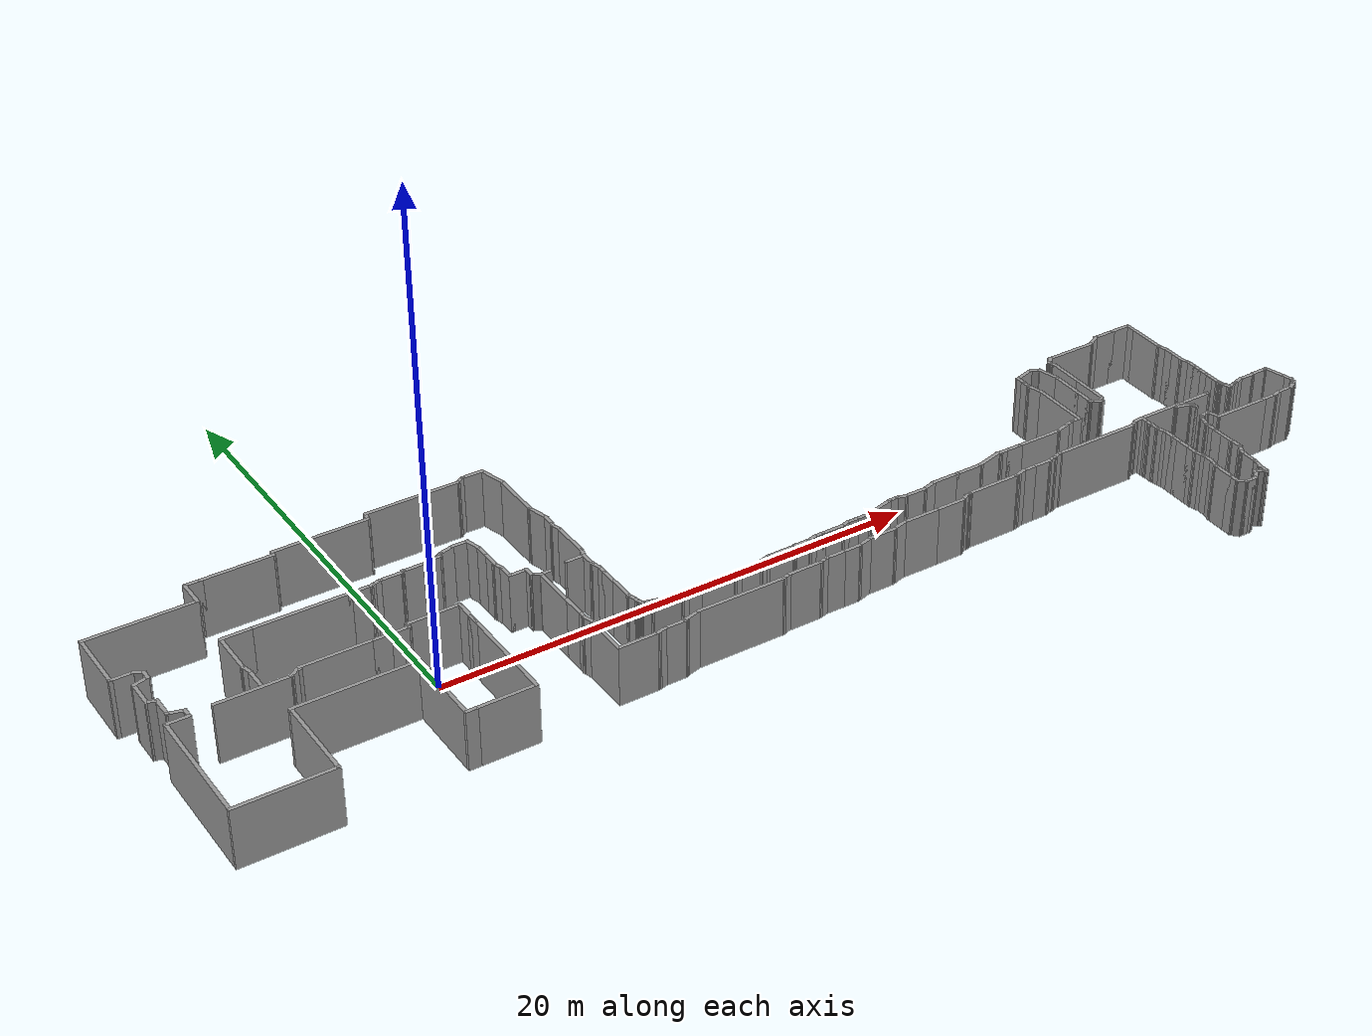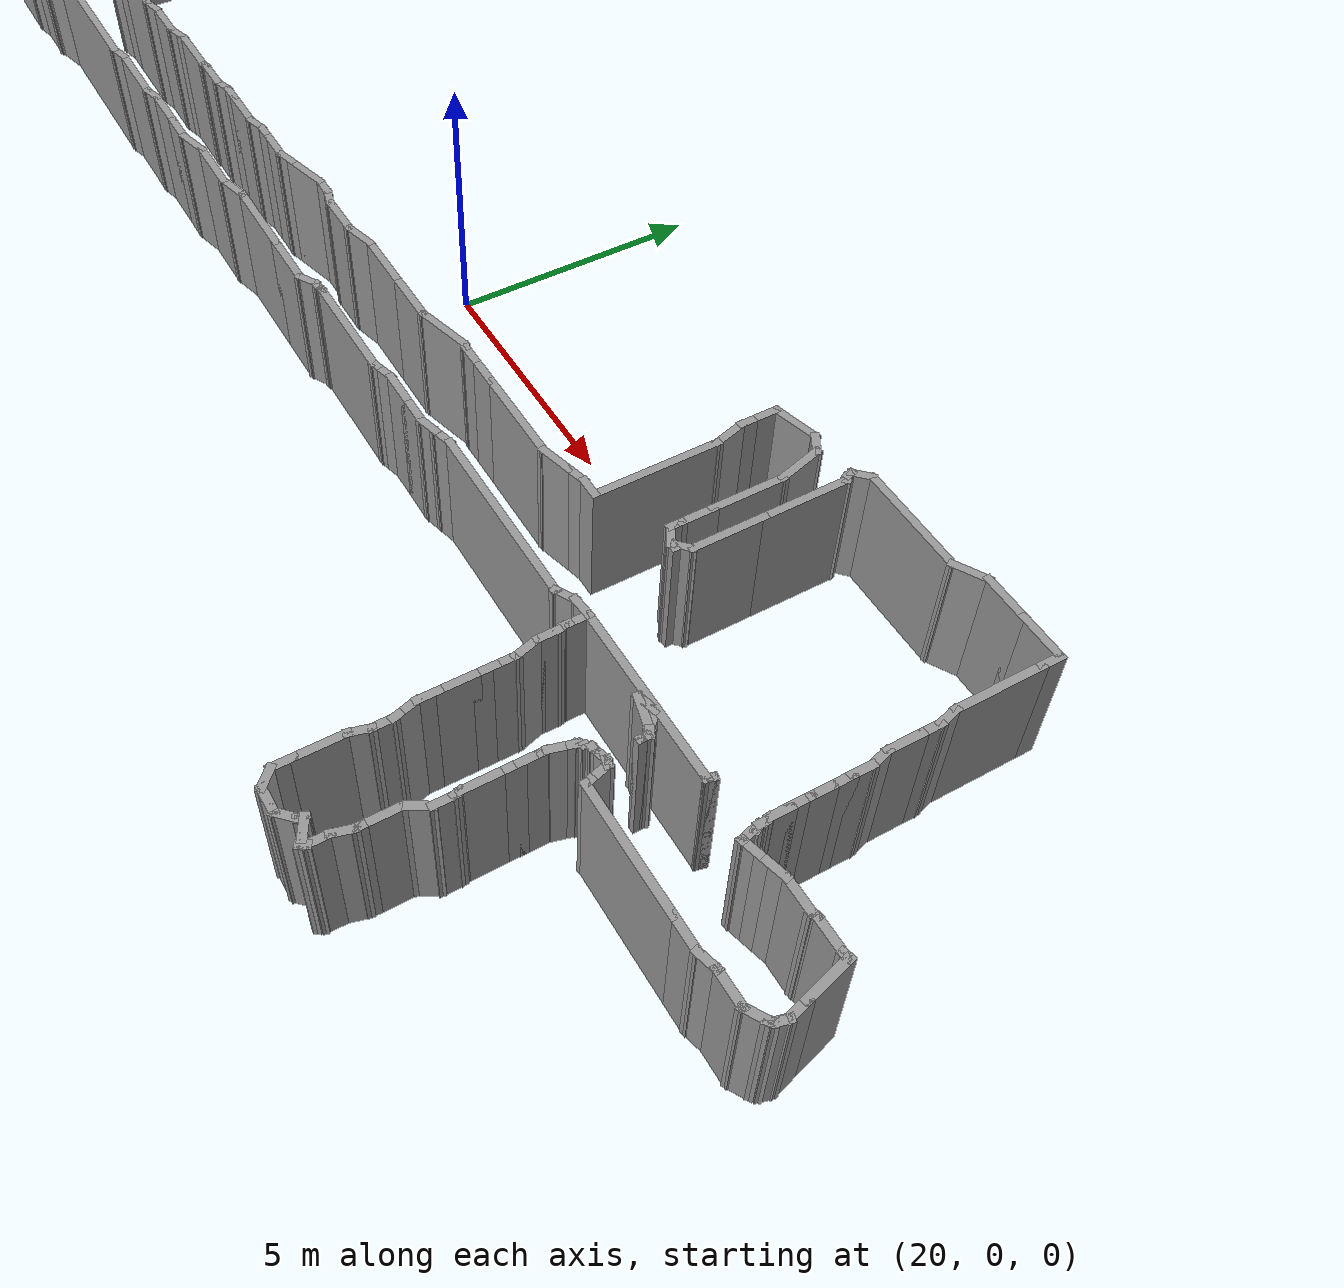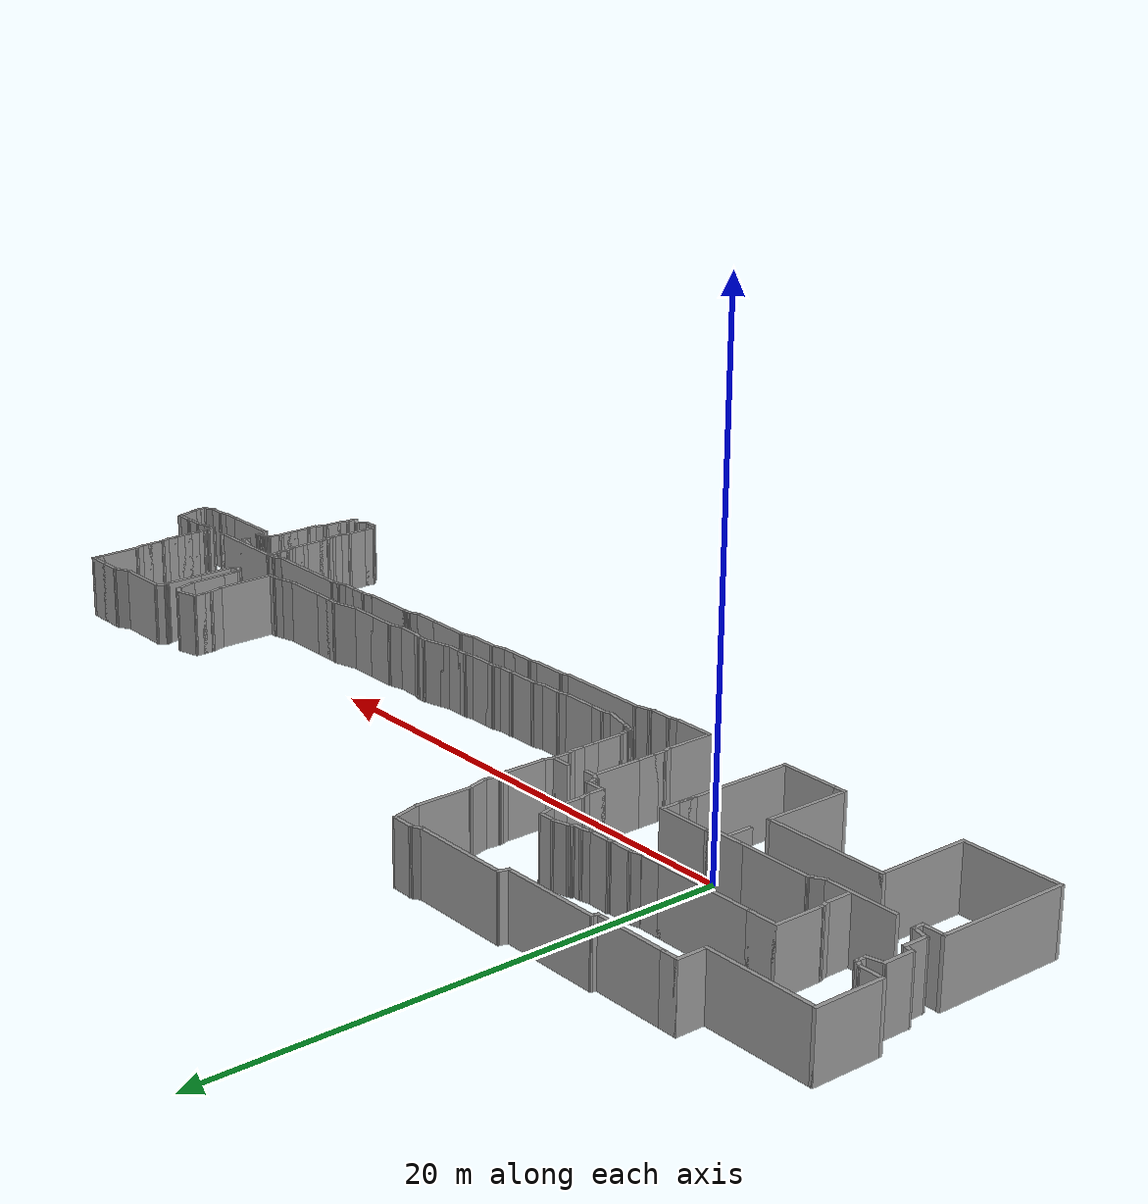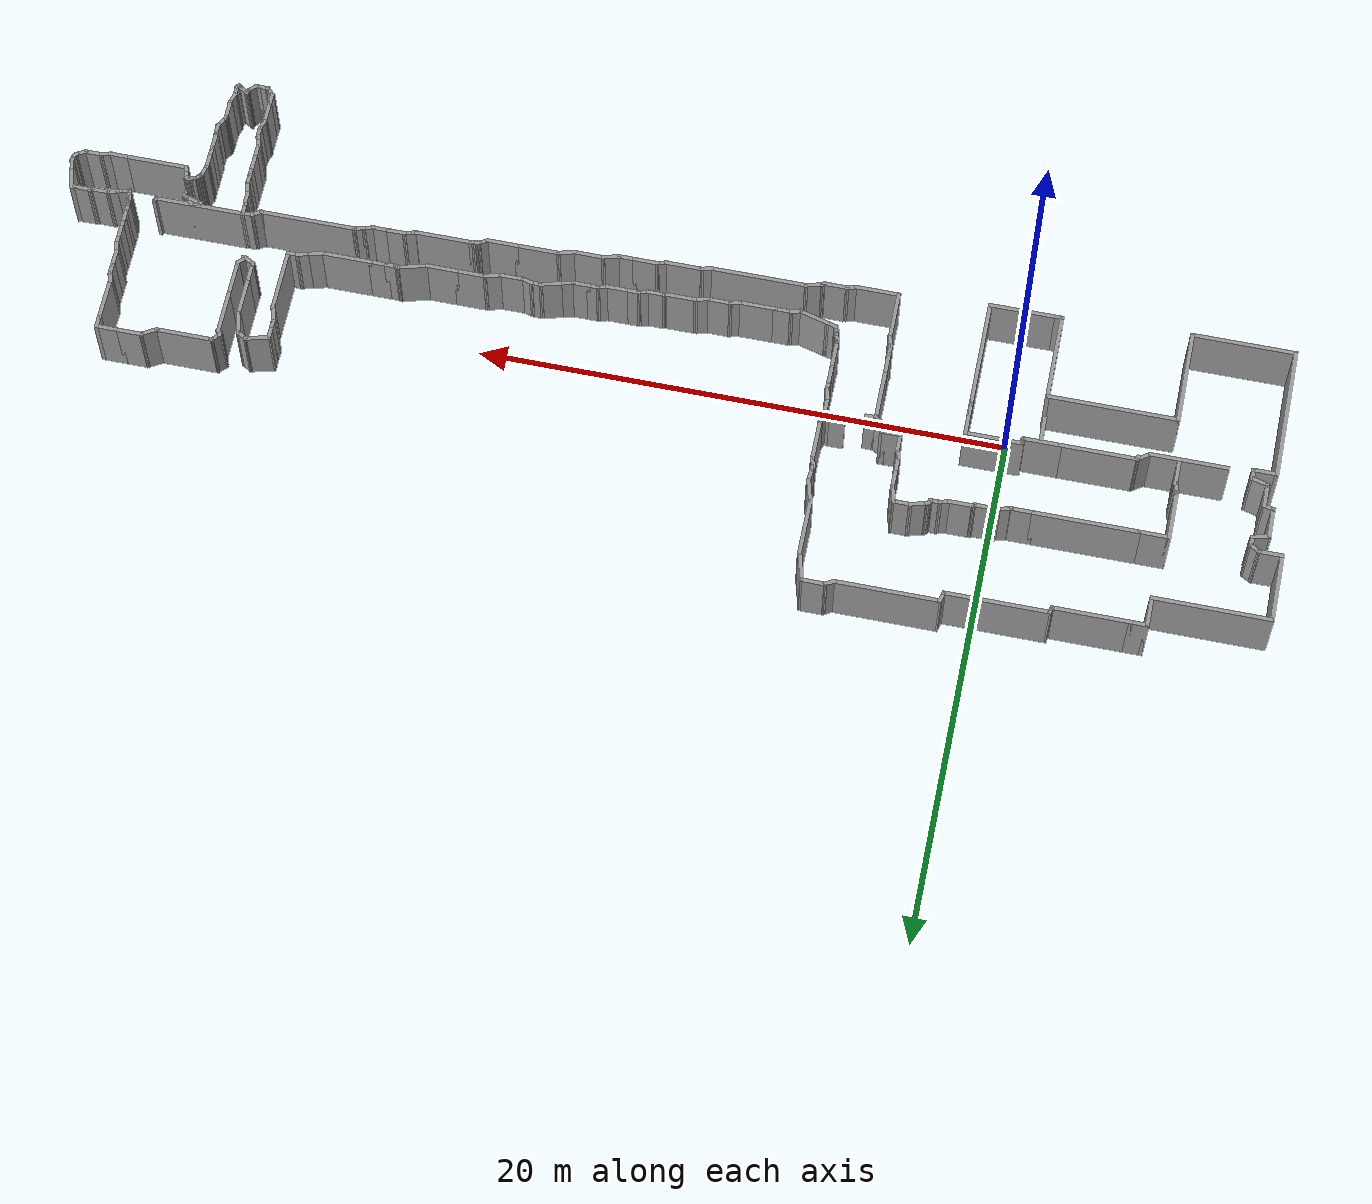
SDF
<?xml version='1.0'?>
<sdf version='1.7'>
  <model name='robovisor_env'>
    <pose>12.9986 -0.167721 0 0 -0 0</pose>
    <link name='Wall_0'>
      <collision name='Wall_0_Collision'>
        <geometry>
          <box>
            <size>1 0.15 2.5</size>
          </box>
        </geometry>
        <pose>0 0 1.25 0 -0 0</pose>
      </collision>
      <visual name='Wall_0_Visual'>
        <pose>0 0 1.25 0 -0 0</pose>
        <geometry>
          <box>
            <size>1 0.15 2.5</size>
          </box>
        </geometry>
        <material>
          <script>
            <uri>file://media/materials/scripts/gazebo.material</uri>
            <name>Gazebo/Grey</name>
          </script>
          <ambient>1 1 1 1</ambient>
        </material>
        <meta>
          <layer>0</layer>
        </meta>
      </visual>
      <pose>-14.2767 0.369884 0 0 -0 1.5708</pose>
    </link>
    <link name='Wall_101'>
      <collision name='Wall_101_Collision'>
        <geometry>
          <box>
            <size>2 0.15 2.5</size>
          </box>
        </geometry>
        <pose>0 0 1.25 0 -0 0</pose>
      </collision>
      <visual name='Wall_101_Visual'>
        <pose>0 0 1.25 0 -0 0</pose>
        <geometry>
          <box>
            <size>2 0.15 2.5</size>
          </box>
        </geometry>
        <material>
          <script>
            <uri>file://media/materials/scripts/gazebo.material</uri>
            <name>Gazebo/Grey</name>
          </script>
          <ambient>1 1 1 1</ambient>
        </material>
        <meta>
          <layer>0</layer>
        </meta>
      </visual>
      <pose>-8.20957 0.222487 0 0 -0 -1.5708</pose>
    </link>
    <link name='Wall_103'>
      <collision name='Wall_103_Collision'>
        <geometry>
          <box>
            <size>1 0.15 2.5</size>
          </box>
        </geometry>
        <pose>0 0 1.25 0 -0 0</pose>
      </collision>
      <visual name='Wall_103_Visual'>
        <pose>0 0 1.25 0 -0 0</pose>
        <geometry>
          <box>
            <size>1 0.15 2.5</size>
          </box>
        </geometry>
        <material>
          <script>
            <uri>file://media/materials/scripts/gazebo.material</uri>
            <name>Gazebo/Grey</name>
          </script>
          <ambient>1 1 1 1</ambient>
        </material>
        <meta>
          <layer>0</layer>
        </meta>
      </visual>
      <pose>-8.20957 -1.12751 0 0 -0 -1.5708</pose>
    </link>
    <link name='Wall_104'>
      <collision name='Wall_104_Collision'>
        <geometry>
          <box>
            <size>0.5 0.15 2.5</size>
          </box>
        </geometry>
        <pose>0 0 1.25 0 -0 0</pose>
      </collision>
      <visual name='Wall_104_Visual'>
        <pose>0 0 1.25 0 -0 0</pose>
        <geometry>
          <box>
            <size>0.5 0.15 2.5</size>
          </box>
        </geometry>
        <material>
          <script>
            <uri>file://media/materials/scripts/gazebo.material</uri>
            <name>Gazebo/Grey</name>
          </script>
          <ambient>1 1 1 1</ambient>
        </material>
        <meta>
          <layer>0</layer>
        </meta>
      </visual>
      <pose>-8.20957 -1.72751 0 0 -0 -1.5708</pose>
    </link>
    <link name='Wall_105'>
      <collision name='Wall_105_Collision'>
        <geometry>
          <box>
            <size>0.5 0.15 2.5</size>
          </box>
        </geometry>
        <pose>0 0 1.25 0 -0 0</pose>
      </collision>
      <visual name='Wall_105_Visual'>
        <pose>0 0 1.25 0 -0 0</pose>
        <geometry>
          <box>
            <size>0.5 0.15 2.5</size>
          </box>
        </geometry>
        <material>
          <script>
            <uri>file://media/materials/scripts/gazebo.material</uri>
            <name>Gazebo/Grey</name>
          </script>
          <ambient>1 1 1 1</ambient>
        </material>
        <meta>
          <layer>0</layer>
        </meta>
      </visual>
      <pose>-8.16427 -2.07155 0 0 -0 -1.309</pose>
    </link>
    <link name='Wall_106'>
      <collision name='Wall_106_Collision'>
        <geometry>
          <box>
            <size>2 0.15 2.5</size>
          </box>
        </geometry>
        <pose>0 0 1.25 0 -0 0</pose>
      </collision>
      <visual name='Wall_106_Visual'>
        <pose>0 0 1.25 0 -0 0</pose>
        <geometry>
          <box>
            <size>2 0.15 2.5</size>
          </box>
        </geometry>
        <material>
          <script>
            <uri>file://media/materials/scripts/gazebo.material</uri>
            <name>Gazebo/Grey</name>
          </script>
          <ambient>1 1 1 1</ambient>
        </material>
        <meta>
          <layer>0</layer>
        </meta>
      </visual>
      <pose>-8.11898 -3.16559 0 0 -0 -1.5708</pose>
    </link>
    <link name='Wall_107'>
      <collision name='Wall_107_Collision'>
        <geometry>
          <box>
            <size>1.75 0.15 2.5</size>
          </box>
        </geometry>
        <pose>0 0 1.25 0 -0 0</pose>
      </collision>
      <visual name='Wall_107_Visual'>
        <pose>0 0 1.25 0 -0 0</pose>
        <geometry>
          <box>
            <size>1.75 0.15 2.5</size>
          </box>
        </geometry>
        <material>
          <script>
            <uri>file://media/materials/scripts/gazebo.material</uri>
            <name>Gazebo/Grey</name>
          </script>
          <ambient>1 1 1 1</ambient>
        </material>
        <meta>
          <layer>0</layer>
        </meta>
      </visual>
      <pose>-7.31898 -4.09059 0 0 -0 0</pose>
    </link>
    <link name='Wall_108'>
      <collision name='Wall_108_Collision'>
        <geometry>
          <box>
            <size>0.5 0.15 2.5</size>
          </box>
        </geometry>
        <pose>0 0 1.25 0 -0 0</pose>
      </collision>
      <visual name='Wall_108_Visual'>
        <pose>0 0 1.25 0 -0 0</pose>
        <geometry>
          <box>
            <size>0.5 0.15 2.5</size>
          </box>
        </geometry>
        <material>
          <script>
            <uri>file://media/materials/scripts/gazebo.material</uri>
            <name>Gazebo/Grey</name>
          </script>
          <ambient>1 1 1 1</ambient>
        </material>
        <meta>
          <layer>0</layer>
        </meta>
      </visual>
      <pose>-6.34994 -4.04529 0 0 -0 0.261799</pose>
    </link>
    <link name='Wall_109'>
      <collision name='Wall_109_Collision'>
        <geometry>
          <box>
            <size>1 0.15 2.5</size>
          </box>
        </geometry>
        <pose>0 0 1.25 0 -0 0</pose>
      </collision>
      <visual name='Wall_109_Visual'>
        <pose>0 0 1.25 0 -0 0</pose>
        <geometry>
          <box>
            <size>1 0.15 2.5</size>
          </box>
        </geometry>
        <material>
          <script>
            <uri>file://media/materials/scripts/gazebo.material</uri>
            <name>Gazebo/Grey</name>
          </script>
          <ambient>1 1 1 1</ambient>
        </material>
        <meta>
          <layer>0</layer>
        </meta>
      </visual>
      <pose>-5.75591 -4 0 0 -0 0</pose>
    </link>
    <link name='Wall_11'>
      <collision name='Wall_11_Collision'>
        <geometry>
          <box>
            <size>4.25 0.15 2.5</size>
          </box>
        </geometry>
        <pose>0 0 1.25 0 -0 0</pose>
      </collision>
      <visual name='Wall_11_Visual'>
        <pose>0 0 1.25 0 -0 0</pose>
        <geometry>
          <box>
            <size>4.25 0.15 2.5</size>
          </box>
        </geometry>
        <material>
          <script>
            <uri>file://media/materials/scripts/gazebo.material</uri>
            <name>Gazebo/Grey</name>
          </script>
          <ambient>1 1 1 1</ambient>
        </material>
        <meta>
          <layer>0</layer>
        </meta>
      </visual>
      <pose>-11.5267 -2.27908 0 0 -0 -1.5708</pose>
    </link>
    <link name='Wall_110'>
      <collision name='Wall_110_Collision'>
        <geometry>
          <box>
            <size>0.25 0.15 2.5</size>
          </box>
        </geometry>
        <pose>0 0 1.25 0 -0 0</pose>
      </collision>
      <visual name='Wall_110_Visual'>
        <pose>0 0 1.25 0 -0 0</pose>
        <geometry>
          <box>
            <size>0.25 0.15 2.5</size>
          </box>
        </geometry>
        <material>
          <script>
            <uri>file://media/materials/scripts/gazebo.material</uri>
            <name>Gazebo/Grey</name>
          </script>
          <ambient>1 1 1 1</ambient>
        </material>
        <meta>
          <layer>0</layer>
        </meta>
      </visual>
      <pose>-5.28761 -3.975 0 0 -0 0.523599</pose>
    </link>
    <link name='Wall_111'>
      <collision name='Wall_111_Collision'>
        <geometry>
          <box>
            <size>0.75 0.15 2.5</size>
          </box>
        </geometry>
        <pose>0 0 1.25 0 -0 0</pose>
      </collision>
      <visual name='Wall_111_Visual'>
        <pose>0 0 1.25 0 -0 0</pose>
        <geometry>
          <box>
            <size>0.75 0.15 2.5</size>
          </box>
        </geometry>
        <material>
          <script>
            <uri>file://media/materials/scripts/gazebo.material</uri>
            <name>Gazebo/Grey</name>
          </script>
          <ambient>1 1 1 1</ambient>
        </material>
        <meta>
          <layer>0</layer>
        </meta>
      </visual>
      <pose>-4.95453 -3.87236 0 0 -0 0.261799</pose>
    </link>
    <link name='Wall_112'>
      <collision name='Wall_112_Collision'>
        <geometry>
          <box>
            <size>3.75 0.15 2.5</size>
          </box>
        </geometry>
        <pose>0 0 1.25 0 -0 0</pose>
      </collision>
      <visual name='Wall_112_Visual'>
        <pose>0 0 1.25 0 -0 0</pose>
        <geometry>
          <box>
            <size>3.75 0.15 2.5</size>
          </box>
        </geometry>
        <material>
          <script>
            <uri>file://media/materials/scripts/gazebo.material</uri>
            <name>Gazebo/Grey</name>
          </script>
          <ambient>1 1 1 1</ambient>
        </material>
        <meta>
          <layer>0</layer>
        </meta>
      </visual>
      <pose>-2.86475 -3.79471 0 0 -0 0</pose>
    </link>
    <link name='Wall_113'>
      <collision name='Wall_113_Collision'>
        <geometry>
          <box>
            <size>0.5 0.15 2.5</size>
          </box>
        </geometry>
        <pose>0 0 1.25 0 -0 0</pose>
      </collision>
      <visual name='Wall_113_Visual'>
        <pose>0 0 1.25 0 -0 0</pose>
        <geometry>
          <box>
            <size>0.5 0.15 2.5</size>
          </box>
        </geometry>
        <material>
          <script>
            <uri>file://media/materials/scripts/gazebo.material</uri>
            <name>Gazebo/Grey</name>
          </script>
          <ambient>1 1 1 1</ambient>
        </material>
        <meta>
          <layer>0</layer>
        </meta>
      </visual>
      <pose>-0.895711 -3.74942 0 0 -0 0.261799</pose>
    </link>
    <link name='Wall_114'>
      <collision name='Wall_114_Collision'>
        <geometry>
          <box>
            <size>1.5 0.15 2.5</size>
          </box>
        </geometry>
        <pose>0 0 1.25 0 -0 0</pose>
      </collision>
      <visual name='Wall_114_Visual'>
        <pose>0 0 1.25 0 -0 0</pose>
        <geometry>
          <box>
            <size>1.5 0.15 2.5</size>
          </box>
        </geometry>
        <material>
          <script>
            <uri>file://media/materials/scripts/gazebo.material</uri>
            <name>Gazebo/Grey</name>
          </script>
          <ambient>1 1 1 1</ambient>
        </material>
        <meta>
          <layer>0</layer>
        </meta>
      </visual>
      <pose>-0.051674 -3.70412 0 0 -0 0</pose>
    </link>
    <link name='Wall_115'>
      <collision name='Wall_115_Collision'>
        <geometry>
          <box>
            <size>0.5 0.15 2.5</size>
          </box>
        </geometry>
        <pose>0 0 1.25 0 -0 0</pose>
      </collision>
      <visual name='Wall_115_Visual'>
        <pose>0 0 1.25 0 -0 0</pose>
        <geometry>
          <box>
            <size>0.5 0.15 2.5</size>
          </box>
        </geometry>
        <material>
          <script>
            <uri>file://media/materials/scripts/gazebo.material</uri>
            <name>Gazebo/Grey</name>
          </script>
          <ambient>1 1 1 1</ambient>
        </material>
        <meta>
          <layer>0</layer>
        </meta>
      </visual>
      <pose>0.792363 -3.65883 0 0 -0 0.261799</pose>
    </link>
    <link name='Wall_116'>
      <collision name='Wall_116_Collision'>
        <geometry>
          <box>
            <size>1 0.15 2.5</size>
          </box>
        </geometry>
        <pose>0 0 1.25 0 -0 0</pose>
      </collision>
      <visual name='Wall_116_Visual'>
        <pose>0 0 1.25 0 -0 0</pose>
        <geometry>
          <box>
            <size>1 0.15 2.5</size>
          </box>
        </geometry>
        <material>
          <script>
            <uri>file://media/materials/scripts/gazebo.material</uri>
            <name>Gazebo/Grey</name>
          </script>
          <ambient>1 1 1 1</ambient>
        </material>
        <meta>
          <layer>0</layer>
        </meta>
      </visual>
      <pose>1.3864 -3.61354 0 0 -0 0</pose>
    </link>
    <link name='Wall_117'>
      <collision name='Wall_117_Collision'>
        <geometry>
          <box>
            <size>0.75 0.15 2.5</size>
          </box>
        </geometry>
        <pose>0 0 1.25 0 -0 0</pose>
      </collision>
      <visual name='Wall_117_Visual'>
        <pose>0 0 1.25 0 -0 0</pose>
        <geometry>
          <box>
            <size>0.75 0.15 2.5</size>
          </box>
        </geometry>
        <material>
          <script>
            <uri>file://media/materials/scripts/gazebo.material</uri>
            <name>Gazebo/Grey</name>
          </script>
          <ambient>1 1 1 1</ambient>
        </material>
        <meta>
          <layer>0</layer>
        </meta>
      </visual>
      <pose>2.1114 -3.61354 0 0 -0 0</pose>
    </link>
    <link name='Wall_118'>
      <collision name='Wall_118_Collision'>
        <geometry>
          <box>
            <size>0.75 0.15 2.5</size>
          </box>
        </geometry>
        <pose>0 0 1.25 0 -0 0</pose>
      </collision>
      <visual name='Wall_118_Visual'>
        <pose>0 0 1.25 0 -0 0</pose>
        <geometry>
          <box>
            <size>0.75 0.15 2.5</size>
          </box>
        </geometry>
        <material>
          <script>
            <uri>file://media/materials/scripts/gazebo.material</uri>
            <name>Gazebo/Grey</name>
          </script>
          <ambient>1 1 1 1</ambient>
        </material>
        <meta>
          <layer>0</layer>
        </meta>
      </visual>
      <pose>2.70118 -3.53589 0 0 -0 0.261799</pose>
    </link>
    <link name='Wall_119'>
      <collision name='Wall_119_Collision'>
        <geometry>
          <box>
            <size>1.25 0.15 2.5</size>
          </box>
        </geometry>
        <pose>0 0 1.25 0 -0 0</pose>
      </collision>
      <visual name='Wall_119_Visual'>
        <pose>0 0 1.25 0 -0 0</pose>
        <geometry>
          <box>
            <size>1.25 0.15 2.5</size>
          </box>
        </geometry>
        <material>
          <script>
            <uri>file://media/materials/scripts/gazebo.material</uri>
            <name>Gazebo/Grey</name>
          </script>
          <ambient>1 1 1 1</ambient>
        </material>
        <meta>
          <layer>0</layer>
        </meta>
      </visual>
      <pose>3.54096 -3.45824 0 0 -0 0</pose>
    </link>
    <link name='Wall_12'>
      <collision name='Wall_12_Collision'>
        <geometry>
          <box>
            <size>2.5 0.15 2.5</size>
          </box>
        </geometry>
        <pose>0 0 1.25 0 -0 0</pose>
      </collision>
      <visual name='Wall_12_Visual'>
        <pose>0 0 1.25 0 -0 0</pose>
        <geometry>
          <box>
            <size>2.5 0.15 2.5</size>
          </box>
        </geometry>
        <material>
          <script>
            <uri>file://media/materials/scripts/gazebo.material</uri>
            <name>Gazebo/Grey</name>
          </script>
          <ambient>1 1 1 1</ambient>
        </material>
        <meta>
          <layer>0</layer>
        </meta>
      </visual>
      <pose>-12.7017 -4.32909 0 0 -0 3.14159</pose>
    </link>
    <link name='Wall_120'>
      <collision name='Wall_120_Collision'>
        <geometry>
          <box>
            <size>0.75 0.15 2.5</size>
          </box>
        </geometry>
        <pose>0 0 1.25 0 -0 0</pose>
      </collision>
      <visual name='Wall_120_Visual'>
        <pose>0 0 1.25 0 -0 0</pose>
        <geometry>
          <box>
            <size>0.75 0.15 2.5</size>
          </box>
        </geometry>
        <material>
          <script>
            <uri>file://media/materials/scripts/gazebo.material</uri>
            <name>Gazebo/Grey</name>
          </script>
          <ambient>1 1 1 1</ambient>
        </material>
        <meta>
          <layer>0</layer>
        </meta>
      </visual>
      <pose>4.38073 -3.3806 0 0 -0 0.261799</pose>
    </link>
    <link name='Wall_121'>
      <collision name='Wall_121_Collision'>
        <geometry>
          <box>
            <size>1.75 0.15 2.5</size>
          </box>
        </geometry>
        <pose>0 0 1.25 0 -0 0</pose>
      </collision>
      <visual name='Wall_121_Visual'>
        <pose>0 0 1.25 0 -0 0</pose>
        <geometry>
          <box>
            <size>1.75 0.15 2.5</size>
          </box>
        </geometry>
        <material>
          <script>
            <uri>file://media/materials/scripts/gazebo.material</uri>
            <name>Gazebo/Grey</name>
          </script>
          <ambient>1 1 1 1</ambient>
        </material>
        <meta>
          <layer>0</layer>
        </meta>
      </visual>
      <pose>5.47051 -3.30295 0 0 -0 0</pose>
    </link>
    <link name='Wall_123'>
      <collision name='Wall_123_Collision'>
        <geometry>
          <box>
            <size>0.75 0.15 2.5</size>
          </box>
        </geometry>
        <pose>0 0 1.25 0 -0 0</pose>
      </collision>
      <visual name='Wall_123_Visual'>
        <pose>0 0 1.25 0 -0 0</pose>
        <geometry>
          <box>
            <size>0.75 0.15 2.5</size>
          </box>
        </geometry>
        <material>
          <script>
            <uri>file://media/materials/scripts/gazebo.material</uri>
            <name>Gazebo/Grey</name>
          </script>
          <ambient>1 1 1 1</ambient>
        </material>
        <meta>
          <layer>0</layer>
        </meta>
      </visual>
      <pose>-6.32777 1.01254 0 0 -0 -1.5708</pose>
    </link>
    <link name='Wall_124'>
      <collision name='Wall_124_Collision'>
        <geometry>
          <box>
            <size>0.5 0.15 2.5</size>
          </box>
        </geometry>
        <pose>0 0 1.25 0 -0 0</pose>
      </collision>
      <visual name='Wall_124_Visual'>
        <pose>0 0 1.25 0 -0 0</pose>
        <geometry>
          <box>
            <size>0.5 0.15 2.5</size>
          </box>
        </geometry>
        <material>
          <script>
            <uri>file://media/materials/scripts/gazebo.material</uri>
            <name>Gazebo/Grey</name>
          </script>
          <ambient>1 1 1 1</ambient>
        </material>
        <meta>
          <layer>0</layer>
        </meta>
      </visual>
      <pose>-6.28248 0.543504 0 0 -0 -1.309</pose>
    </link>
    <link name='Wall_125'>
      <collision name='Wall_125_Collision'>
        <geometry>
          <box>
            <size>0.5 0.15 2.5</size>
          </box>
        </geometry>
        <pose>0 0 1.25 0 -0 0</pose>
      </collision>
      <visual name='Wall_125_Visual'>
        <pose>0 0 1.25 0 -0 0</pose>
        <geometry>
          <box>
            <size>0.5 0.15 2.5</size>
          </box>
        </geometry>
        <material>
          <script>
            <uri>file://media/materials/scripts/gazebo.material</uri>
            <name>Gazebo/Grey</name>
          </script>
          <ambient>1 1 1 1</ambient>
        </material>
        <meta>
          <layer>0</layer>
        </meta>
      </visual>
      <pose>-6.23718 0.199467 0 0 -0 -1.5708</pose>
    </link>
    <link name='Wall_126'>
      <collision name='Wall_126_Collision'>
        <geometry>
          <box>
            <size>0.75 0.15 2.5</size>
          </box>
        </geometry>
        <pose>0 0 1.25 0 -0 0</pose>
      </collision>
      <visual name='Wall_126_Visual'>
        <pose>0 0 1.25 0 -0 0</pose>
        <geometry>
          <box>
            <size>0.75 0.15 2.5</size>
          </box>
        </geometry>
        <material>
          <script>
            <uri>file://media/materials/scripts/gazebo.material</uri>
            <name>Gazebo/Grey</name>
          </script>
          <ambient>1 1 1 1</ambient>
        </material>
        <meta>
          <layer>0</layer>
        </meta>
      </visual>
      <pose>-6.23718 -0.275533 0 0 -0 -1.5708</pose>
    </link>
    <link name='Wall_127'>
      <collision name='Wall_127_Collision'>
        <geometry>
          <box>
            <size>1.25 0.15 2.5</size>
          </box>
        </geometry>
        <pose>0 0 1.25 0 -0 0</pose>
      </collision>
      <visual name='Wall_127_Visual'>
        <pose>0 0 1.25 0 -0 0</pose>
        <geometry>
          <box>
            <size>1.25 0.15 2.5</size>
          </box>
        </geometry>
        <material>
          <script>
            <uri>file://media/materials/scripts/gazebo.material</uri>
            <name>Gazebo/Grey</name>
          </script>
          <ambient>1 1 1 1</ambient>
        </material>
        <meta>
          <layer>0</layer>
        </meta>
      </visual>
      <pose>-6.23718 -1.12553 0 0 -0 -1.5708</pose>
    </link>
    <link name='Wall_128'>
      <collision name='Wall_128_Collision'>
        <geometry>
          <box>
            <size>0.5 0.15 2.5</size>
          </box>
        </geometry>
        <pose>0 0 1.25 0 -0 0</pose>
      </collision>
      <visual name='Wall_128_Visual'>
        <pose>0 0 1.25 0 -0 0</pose>
        <geometry>
          <box>
            <size>0.5 0.15 2.5</size>
          </box>
        </geometry>
        <material>
          <script>
            <uri>file://media/materials/scripts/gazebo.material</uri>
            <name>Gazebo/Grey</name>
          </script>
          <ambient>1 1 1 1</ambient>
        </material>
        <meta>
          <layer>0</layer>
        </meta>
      </visual>
      <pose>-6.19189 -1.84457 0 0 -0 -1.309</pose>
    </link>
    <link name='Wall_129'>
      <collision name='Wall_129_Collision'>
        <geometry>
          <box>
            <size>0.25 0.15 2.5</size>
          </box>
        </geometry>
        <pose>0 0 1.25 0 -0 0</pose>
      </collision>
      <visual name='Wall_129_Visual'>
        <pose>0 0 1.25 0 -0 0</pose>
        <geometry>
          <box>
            <size>0.25 0.15 2.5</size>
          </box>
        </geometry>
        <material>
          <script>
            <uri>file://media/materials/scripts/gazebo.material</uri>
            <name>Gazebo/Grey</name>
          </script>
          <ambient>1 1 1 1</ambient>
        </material>
        <meta>
          <layer>0</layer>
        </meta>
      </visual>
      <pose>-6.1466 -2.06361 0 0 -0 -1.5708</pose>
    </link>
    <link name='Wall_13'>
      <collision name='Wall_13_Collision'>
        <geometry>
          <box>
            <size>0.5 0.15 2.5</size>
          </box>
        </geometry>
        <pose>0 0 1.25 0 -0 0</pose>
      </collision>
      <visual name='Wall_13_Visual'>
        <pose>0 0 1.25 0 -0 0</pose>
        <geometry>
          <box>
            <size>0.5 0.15 2.5</size>
          </box>
        </geometry>
        <material>
          <script>
            <uri>file://media/materials/scripts/gazebo.material</uri>
            <name>Gazebo/Grey</name>
          </script>
          <ambient>1 1 1 1</ambient>
        </material>
        <meta>
          <layer>0</layer>
        </meta>
      </visual>
      <pose>-14.0517 -4.32909 0 0 -0 3.14159</pose>
    </link>
    <link name='Wall_130'>
      <collision name='Wall_130_Collision'>
        <geometry>
          <box>
            <size>0.25 0.15 2.5</size>
          </box>
        </geometry>
        <pose>0 0 1.25 0 -0 0</pose>
      </collision>
      <visual name='Wall_130_Visual'>
        <pose>0 0 1.25 0 -0 0</pose>
        <geometry>
          <box>
            <size>0.25 0.15 2.5</size>
          </box>
        </geometry>
        <material>
          <script>
            <uri>file://media/materials/scripts/gazebo.material</uri>
            <name>Gazebo/Grey</name>
          </script>
          <ambient>1 1 1 1</ambient>
        </material>
        <meta>
          <layer>0</layer>
        </meta>
      </visual>
      <pose>-6.1216 -2.15691 0 0 -0 -1.0472</pose>
    </link>
    <link name='Wall_131'>
      <collision name='Wall_131_Collision'>
        <geometry>
          <box>
            <size>0.25 0.15 2.5</size>
          </box>
        </geometry>
        <pose>0 0 1.25 0 -0 0</pose>
      </collision>
      <visual name='Wall_131_Visual'>
        <pose>0 0 1.25 0 -0 0</pose>
        <geometry>
          <box>
            <size>0.25 0.15 2.5</size>
          </box>
        </geometry>
        <material>
          <script>
            <uri>file://media/materials/scripts/gazebo.material</uri>
            <name>Gazebo/Grey</name>
          </script>
          <ambient>1 1 1 1</ambient>
        </material>
        <meta>
          <layer>0</layer>
        </meta>
      </visual>
      <pose>-6.08366 -2.24851 0 0 -0 -1.309</pose>
    </link>
    <link name='Wall_132'>
      <collision name='Wall_132_Collision'>
        <geometry>
          <box>
            <size>0.15 0.15 2.5</size>
          </box>
        </geometry>
        <pose>0 0 1.25 0 -0 0</pose>
      </collision>
      <visual name='Wall_132_Visual'>
        <pose>0 0 1.25 0 -0 0</pose>
        <geometry>
          <box>
            <size>0.15 0.15 2.5</size>
          </box>
        </geometry>
        <material>
          <script>
            <uri>file://media/materials/scripts/gazebo.material</uri>
            <name>Gazebo/Grey</name>
          </script>
          <ambient>1 1 1 1</ambient>
        </material>
        <meta>
          <layer>0</layer>
        </meta>
      </visual>
      <pose>-6.07071 -2.2968 0 0 -0 0</pose>
    </link>
    <link name='Wall_133'>
      <collision name='Wall_133_Collision'>
        <geometry>
          <box>
            <size>0.5 0.15 2.5</size>
          </box>
        </geometry>
        <pose>0 0 1.25 0 -0 0</pose>
      </collision>
      <visual name='Wall_133_Visual'>
        <pose>0 0 1.25 0 -0 0</pose>
        <geometry>
          <box>
            <size>0.5 0.15 2.5</size>
          </box>
        </geometry>
        <material>
          <script>
            <uri>file://media/materials/scripts/gazebo.material</uri>
            <name>Gazebo/Grey</name>
          </script>
          <ambient>1 1 1 1</ambient>
        </material>
        <meta>
          <layer>0</layer>
        </meta>
      </visual>
      <pose>-5.90168 -2.3421 0 0 -0 -0.261799</pose>
    </link>
    <link name='Wall_134'>
      <collision name='Wall_134_Collision'>
        <geometry>
          <box>
            <size>0.15 0.15 2.5</size>
          </box>
        </geometry>
        <pose>0 0 1.25 0 -0 0</pose>
      </collision>
      <visual name='Wall_134_Visual'>
        <pose>0 0 1.25 0 -0 0</pose>
        <geometry>
          <box>
            <size>0.15 0.15 2.5</size>
          </box>
        </geometry>
        <material>
          <script>
            <uri>file://media/materials/scripts/gazebo.material</uri>
            <name>Gazebo/Grey</name>
          </script>
          <ambient>1 1 1 1</ambient>
        </material>
        <meta>
          <layer>0</layer>
        </meta>
      </visual>
      <pose>-5.73264 -2.38739 0 0 -0 0</pose>
    </link>
    <link name='Wall_135'>
      <collision name='Wall_135_Collision'>
        <geometry>
          <box>
            <size>1.25 0.15 2.5</size>
          </box>
        </geometry>
        <pose>0 0 1.25 0 -0 0</pose>
      </collision>
      <visual name='Wall_135_Visual'>
        <pose>0 0 1.25 0 -0 0</pose>
        <geometry>
          <box>
            <size>1.25 0.15 2.5</size>
          </box>
        </geometry>
        <material>
          <script>
            <uri>file://media/materials/scripts/gazebo.material</uri>
            <name>Gazebo/Grey</name>
          </script>
          <ambient>1 1 1 1</ambient>
        </material>
        <meta>
          <layer>0</layer>
        </meta>
      </visual>
      <pose>-5.20138 -2.52974 0 0 -0 -0.261799</pose>
    </link>
    <link name='Wall_136'>
      <collision name='Wall_136_Collision'>
        <geometry>
          <box>
            <size>0.5 0.15 2.5</size>
          </box>
        </geometry>
        <pose>0 0 1.25 0 -0 0</pose>
      </collision>
      <visual name='Wall_136_Visual'>
        <pose>0 0 1.25 0 -0 0</pose>
        <geometry>
          <box>
            <size>0.5 0.15 2.5</size>
          </box>
        </geometry>
        <material>
          <script>
            <uri>file://media/materials/scripts/gazebo.material</uri>
            <name>Gazebo/Grey</name>
          </script>
          <ambient>1 1 1 1</ambient>
        </material>
        <meta>
          <layer>0</layer>
        </meta>
      </visual>
      <pose>-4.50109 -2.6268 0 0 -0 0.261799</pose>
    </link>
    <link name='Wall_137'>
      <collision name='Wall_137_Collision'>
        <geometry>
          <box>
            <size>0.75 0.15 2.5</size>
          </box>
        </geometry>
        <pose>0 0 1.25 0 -0 0</pose>
      </collision>
      <visual name='Wall_137_Visual'>
        <pose>0 0 1.25 0 -0 0</pose>
        <geometry>
          <box>
            <size>0.75 0.15 2.5</size>
          </box>
        </geometry>
        <material>
          <script>
            <uri>file://media/materials/scripts/gazebo.material</uri>
            <name>Gazebo/Grey</name>
          </script>
          <ambient>1 1 1 1</ambient>
        </material>
        <meta>
          <layer>0</layer>
        </meta>
      </visual>
      <pose>-4.03205 -2.5815 0 0 -0 0</pose>
    </link>
    <link name='Wall_138'>
      <collision name='Wall_138_Collision'>
        <geometry>
          <box>
            <size>1.5 0.15 2.5</size>
          </box>
        </geometry>
        <pose>0 0 1.25 0 -0 0</pose>
      </collision>
      <visual name='Wall_138_Visual'>
        <pose>0 0 1.25 0 -0 0</pose>
        <geometry>
          <box>
            <size>1.5 0.15 2.5</size>
          </box>
        </geometry>
        <material>
          <script>
            <uri>file://media/materials/scripts/gazebo.material</uri>
            <name>Gazebo/Grey</name>
          </script>
          <ambient>1 1 1 1</ambient>
        </material>
        <meta>
          <layer>0</layer>
        </meta>
      </visual>
      <pose>-3.05705 -2.5815 0 0 -0 0</pose>
    </link>
    <link name='Wall_139'>
      <collision name='Wall_139_Collision'>
        <geometry>
          <box>
            <size>0.5 0.15 2.5</size>
          </box>
        </geometry>
        <pose>0 0 1.25 0 -0 0</pose>
      </collision>
      <visual name='Wall_139_Visual'>
        <pose>0 0 1.25 0 -0 0</pose>
        <geometry>
          <box>
            <size>0.5 0.15 2.5</size>
          </box>
        </geometry>
        <material>
          <script>
            <uri>file://media/materials/scripts/gazebo.material</uri>
            <name>Gazebo/Grey</name>
          </script>
          <ambient>1 1 1 1</ambient>
        </material>
        <meta>
          <layer>0</layer>
        </meta>
      </visual>
      <pose>-2.21301 -2.53621 0 0 -0 0.261799</pose>
    </link>
    <link name='Wall_14'>
      <collision name='Wall_14_Collision'>
        <geometry>
          <box>
            <size>3.5 0.15 2.5</size>
          </box>
        </geometry>
        <pose>0 0 1.25 0 -0 0</pose>
      </collision>
      <visual name='Wall_14_Visual'>
        <pose>0 0 1.25 0 -0 0</pose>
        <geometry>
          <box>
            <size>3.5 0.15 2.5</size>
          </box>
        </geometry>
        <material>
          <script>
            <uri>file://media/materials/scripts/gazebo.material</uri>
            <name>Gazebo/Grey</name>
          </script>
          <ambient>1 1 1 1</ambient>
        </material>
        <meta>
          <layer>0</layer>
        </meta>
      </visual>
      <pose>-14.2267 -2.65408 0 0 -0 1.5708</pose>
    </link>
    <link name='Wall_140'>
      <collision name='Wall_140_Collision'>
        <geometry>
          <box>
            <size>1 0.15 2.5</size>
          </box>
        </geometry>
        <pose>0 0 1.25 0 -0 0</pose>
      </collision>
      <visual name='Wall_140_Visual'>
        <pose>0 0 1.25 0 -0 0</pose>
        <geometry>
          <box>
            <size>1 0.15 2.5</size>
          </box>
        </geometry>
        <material>
          <script>
            <uri>file://media/materials/scripts/gazebo.material</uri>
            <name>Gazebo/Grey</name>
          </script>
          <ambient>1 1 1 1</ambient>
        </material>
        <meta>
          <layer>0</layer>
        </meta>
      </visual>
      <pose>-1.61898 -2.49092 0 0 -0 0</pose>
    </link>
    <link name='Wall_141'>
      <collision name='Wall_141_Collision'>
        <geometry>
          <box>
            <size>0.5 0.15 2.5</size>
          </box>
        </geometry>
        <pose>0 0 1.25 0 -0 0</pose>
      </collision>
      <visual name='Wall_141_Visual'>
        <pose>0 0 1.25 0 -0 0</pose>
        <geometry>
          <box>
            <size>0.5 0.15 2.5</size>
          </box>
        </geometry>
        <material>
          <script>
            <uri>file://media/materials/scripts/gazebo.material</uri>
            <name>Gazebo/Grey</name>
          </script>
          <ambient>1 1 1 1</ambient>
        </material>
        <meta>
          <layer>0</layer>
        </meta>
      </visual>
      <pose>-1.02494 -2.44562 0 0 -0 0.261799</pose>
    </link>
    <link name='Wall_142'>
      <collision name='Wall_142_Collision'>
        <geometry>
          <box>
            <size>0.25 0.15 2.5</size>
          </box>
        </geometry>
        <pose>0 0 1.25 0 -0 0</pose>
      </collision>
      <visual name='Wall_142_Visual'>
        <pose>0 0 1.25 0 -0 0</pose>
        <geometry>
          <box>
            <size>0.25 0.15 2.5</size>
          </box>
        </geometry>
        <material>
          <script>
            <uri>file://media/materials/scripts/gazebo.material</uri>
            <name>Gazebo/Grey</name>
          </script>
          <ambient>1 1 1 1</ambient>
        </material>
        <meta>
          <layer>0</layer>
        </meta>
      </visual>
      <pose>-0.807605 -2.38739 0 0 -0 0.261799</pose>
    </link>
    <link name='Wall_143'>
      <collision name='Wall_143_Collision'>
        <geometry>
          <box>
            <size>1.25 0.15 2.5</size>
          </box>
        </geometry>
        <pose>0 0 1.25 0 -0 0</pose>
      </collision>
      <visual name='Wall_143_Visual'>
        <pose>0 0 1.25 0 -0 0</pose>
        <geometry>
          <box>
            <size>1.25 0.15 2.5</size>
          </box>
        </geometry>
        <material>
          <script>
            <uri>file://media/materials/scripts/gazebo.material</uri>
            <name>Gazebo/Grey</name>
          </script>
          <ambient>1 1 1 1</ambient>
        </material>
        <meta>
          <layer>0</layer>
        </meta>
      </visual>
      <pose>-0.209308 -2.37445 0 0 -0 0</pose>
    </link>
    <link name='Wall_144'>
      <collision name='Wall_144_Collision'>
        <geometry>
          <box>
            <size>0.25 0.15 2.5</size>
          </box>
        </geometry>
        <pose>0 0 1.25 0 -0 0</pose>
      </collision>
      <visual name='Wall_144_Visual'>
        <pose>0 0 1.25 0 -0 0</pose>
        <geometry>
          <box>
            <size>0.25 0.15 2.5</size>
          </box>
        </geometry>
        <material>
          <script>
            <uri>file://media/materials/scripts/gazebo.material</uri>
            <name>Gazebo/Grey</name>
          </script>
          <ambient>1 1 1 1</ambient>
        </material>
        <meta>
          <layer>0</layer>
        </meta>
      </visual>
      <pose>0.388988 -2.36151 0 0 -0 0.261799</pose>
    </link>
    <link name='Wall_145'>
      <collision name='Wall_145_Collision'>
        <geometry>
          <box>
            <size>0.75 0.15 2.5</size>
          </box>
        </geometry>
        <pose>0 0 1.25 0 -0 0</pose>
      </collision>
      <visual name='Wall_145_Visual'>
        <pose>0 0 1.25 0 -0 0</pose>
        <geometry>
          <box>
            <size>0.75 0.15 2.5</size>
          </box>
        </geometry>
        <material>
          <script>
            <uri>file://media/materials/scripts/gazebo.material</uri>
            <name>Gazebo/Grey</name>
          </script>
          <ambient>1 1 1 1</ambient>
        </material>
        <meta>
          <layer>0</layer>
        </meta>
      </visual>
      <pose>0.737285 -2.34857 0 0 -0 0</pose>
    </link>
    <link name='Wall_146'>
      <collision name='Wall_146_Collision'>
        <geometry>
          <box>
            <size>0.5 0.15 2.5</size>
          </box>
        </geometry>
        <pose>0 0 1.25 0 -0 0</pose>
      </collision>
      <visual name='Wall_146_Visual'>
        <pose>0 0 1.25 0 -0 0</pose>
        <geometry>
          <box>
            <size>0.5 0.15 2.5</size>
          </box>
        </geometry>
        <material>
          <script>
            <uri>file://media/materials/scripts/gazebo.material</uri>
            <name>Gazebo/Grey</name>
          </script>
          <ambient>1 1 1 1</ambient>
        </material>
        <meta>
          <layer>0</layer>
        </meta>
      </visual>
      <pose>1.20632 -2.30327 0 0 -0 0.261799</pose>
    </link>
    <link name='Wall_147'>
      <collision name='Wall_147_Collision'>
        <geometry>
          <box>
            <size>0.5 0.15 2.5</size>
          </box>
        </geometry>
        <pose>0 0 1.25 0 -0 0</pose>
      </collision>
      <visual name='Wall_147_Visual'>
        <pose>0 0 1.25 0 -0 0</pose>
        <geometry>
          <box>
            <size>0.5 0.15 2.5</size>
          </box>
        </geometry>
        <material>
          <script>
            <uri>file://media/materials/scripts/gazebo.material</uri>
            <name>Gazebo/Grey</name>
          </script>
          <ambient>1 1 1 1</ambient>
        </material>
        <meta>
          <layer>0</layer>
        </meta>
      </visual>
      <pose>1.55036 -2.25798 0 0 -0 0</pose>
    </link>
    <link name='Wall_148'>
      <collision name='Wall_148_Collision'>
        <geometry>
          <box>
            <size>1 0.15 2.5</size>
          </box>
        </geometry>
        <pose>0 0 1.25 0 -0 0</pose>
      </collision>
      <visual name='Wall_148_Visual'>
        <pose>0 0 1.25 0 -0 0</pose>
        <geometry>
          <box>
            <size>1 0.15 2.5</size>
          </box>
        </geometry>
        <material>
          <script>
            <uri>file://media/materials/scripts/gazebo.material</uri>
            <name>Gazebo/Grey</name>
          </script>
          <ambient>1 1 1 1</ambient>
        </material>
        <meta>
          <layer>0</layer>
        </meta>
      </visual>
      <pose>2.15036 -2.25798 0 0 -0 0</pose>
    </link>
    <link name='Wall_149'>
      <collision name='Wall_149_Collision'>
        <geometry>
          <box>
            <size>0.5 0.15 2.5</size>
          </box>
        </geometry>
        <pose>0 0 1.25 0 -0 0</pose>
      </collision>
      <visual name='Wall_149_Visual'>
        <pose>0 0 1.25 0 -0 0</pose>
        <geometry>
          <box>
            <size>0.5 0.15 2.5</size>
          </box>
        </geometry>
        <material>
          <script>
            <uri>file://media/materials/scripts/gazebo.material</uri>
            <name>Gazebo/Grey</name>
          </script>
          <ambient>1 1 1 1</ambient>
        </material>
        <meta>
          <layer>0</layer>
        </meta>
      </visual>
      <pose>2.74439 -2.21269 0 0 -0 0.261799</pose>
    </link>
    <link name='Wall_15'>
      <collision name='Wall_15_Collision'>
        <geometry>
          <box>
            <size>5 0.15 2.5</size>
          </box>
        </geometry>
        <pose>0 0 1.25 0 -0 0</pose>
      </collision>
      <visual name='Wall_15_Visual'>
        <pose>0 0 1.25 0 -0 0</pose>
        <geometry>
          <box>
            <size>5 0.15 2.5</size>
          </box>
        </geometry>
        <material>
          <script>
            <uri>file://media/materials/scripts/gazebo.material</uri>
            <name>Gazebo/Grey</name>
          </script>
          <ambient>1 1 1 1</ambient>
        </material>
        <meta>
          <layer>0</layer>
        </meta>
      </visual>
      <pose>-16.6517 -0.979085 0 0 -0 3.14159</pose>
    </link>
    <link name='Wall_150'>
      <collision name='Wall_150_Collision'>
        <geometry>
          <box>
            <size>0.5 0.15 2.5</size>
          </box>
        </geometry>
        <pose>0 0 1.25 0 -0 0</pose>
      </collision>
      <visual name='Wall_150_Visual'>
        <pose>0 0 1.25 0 -0 0</pose>
        <geometry>
          <box>
            <size>0.5 0.15 2.5</size>
          </box>
        </geometry>
        <material>
          <script>
            <uri>file://media/materials/scripts/gazebo.material</uri>
            <name>Gazebo/Grey</name>
          </script>
          <ambient>1 1 1 1</ambient>
        </material>
        <meta>
          <layer>0</layer>
        </meta>
      </visual>
      <pose>3.08843 -2.16739 0 0 -0 0</pose>
    </link>
    <link name='Wall_151'>
      <collision name='Wall_151_Collision'>
        <geometry>
          <box>
            <size>0.75 0.15 2.5</size>
          </box>
        </geometry>
        <pose>0 0 1.25 0 -0 0</pose>
      </collision>
      <visual name='Wall_151_Visual'>
        <pose>0 0 1.25 0 -0 0</pose>
        <geometry>
          <box>
            <size>0.75 0.15 2.5</size>
          </box>
        </geometry>
        <material>
          <script>
            <uri>file://media/materials/scripts/gazebo.material</uri>
            <name>Gazebo/Grey</name>
          </script>
          <ambient>1 1 1 1</ambient>
        </material>
        <meta>
          <layer>0</layer>
        </meta>
      </visual>
      <pose>3.56343 -2.16739 0 0 -0 0</pose>
    </link>
    <link name='Wall_152'>
      <collision name='Wall_152_Collision'>
        <geometry>
          <box>
            <size>0.5 0.15 2.5</size>
          </box>
        </geometry>
        <pose>0 0 1.25 0 -0 0</pose>
      </collision>
      <visual name='Wall_152_Visual'>
        <pose>0 0 1.25 0 -0 0</pose>
        <geometry>
          <box>
            <size>0.5 0.15 2.5</size>
          </box>
        </geometry>
        <material>
          <script>
            <uri>file://media/materials/scripts/gazebo.material</uri>
            <name>Gazebo/Grey</name>
          </script>
          <ambient>1 1 1 1</ambient>
        </material>
        <meta>
          <layer>0</layer>
        </meta>
      </visual>
      <pose>4.03247 -2.1221 0 0 -0 0.261799</pose>
    </link>
    <link name='Wall_153'>
      <collision name='Wall_153_Collision'>
        <geometry>
          <box>
            <size>1 0.15 2.5</size>
          </box>
        </geometry>
        <pose>0 0 1.25 0 -0 0</pose>
      </collision>
      <visual name='Wall_153_Visual'>
        <pose>0 0 1.25 0 -0 0</pose>
        <geometry>
          <box>
            <size>1 0.15 2.5</size>
          </box>
        </geometry>
        <material>
          <script>
            <uri>file://media/materials/scripts/gazebo.material</uri>
            <name>Gazebo/Grey</name>
          </script>
          <ambient>1 1 1 1</ambient>
        </material>
        <meta>
          <layer>0</layer>
        </meta>
      </visual>
      <pose>4.61203 -1.96681 0 0 -0 0.261799</pose>
    </link>
    <link name='Wall_154'>
      <collision name='Wall_154_Collision'>
        <geometry>
          <box>
            <size>0.5 0.15 2.5</size>
          </box>
        </geometry>
        <pose>0 0 1.25 0 -0 0</pose>
      </collision>
      <visual name='Wall_154_Visual'>
        <pose>0 0 1.25 0 -0 0</pose>
        <geometry>
          <box>
            <size>0.5 0.15 2.5</size>
          </box>
        </geometry>
        <material>
          <script>
            <uri>file://media/materials/scripts/gazebo.material</uri>
            <name>Gazebo/Grey</name>
          </script>
          <ambient>1 1 1 1</ambient>
        </material>
        <meta>
          <layer>0</layer>
        </meta>
      </visual>
      <pose>5.19754 -1.85681 0 0 -0 0</pose>
    </link>
    <link name='Wall_155'>
      <collision name='Wall_155_Collision'>
        <geometry>
          <box>
            <size>0.5 0.15 2.5</size>
          </box>
        </geometry>
        <pose>0 0 1.25 0 -0 0</pose>
      </collision>
      <visual name='Wall_155_Visual'>
        <pose>0 0 1.25 0 -0 0</pose>
        <geometry>
          <box>
            <size>0.5 0.15 2.5</size>
          </box>
        </geometry>
        <material>
          <script>
            <uri>file://media/materials/scripts/gazebo.material</uri>
            <name>Gazebo/Grey</name>
          </script>
          <ambient>1 1 1 1</ambient>
        </material>
        <meta>
          <layer>0</layer>
        </meta>
      </visual>
      <pose>5.54158 -1.9021 0 0 -0 -0.261799</pose>
    </link>
    <link name='Wall_156'>
      <collision name='Wall_156_Collision'>
        <geometry>
          <box>
            <size>1 0.15 2.5</size>
          </box>
        </geometry>
        <pose>0 0 1.25 0 -0 0</pose>
      </collision>
      <visual name='Wall_156_Visual'>
        <pose>0 0 1.25 0 -0 0</pose>
        <geometry>
          <box>
            <size>1 0.15 2.5</size>
          </box>
        </geometry>
        <material>
          <script>
            <uri>file://media/materials/scripts/gazebo.material</uri>
            <name>Gazebo/Grey</name>
          </script>
          <ambient>1 1 1 1</ambient>
        </material>
        <meta>
          <layer>0</layer>
        </meta>
      </visual>
      <pose>6.13562 -1.9474 0 0 -0 0</pose>
    </link>
    <link name='Wall_157'>
      <collision name='Wall_157_Collision'>
        <geometry>
          <box>
            <size>0.75 0.15 2.5</size>
          </box>
        </geometry>
        <pose>0 0 1.25 0 -0 0</pose>
      </collision>
      <visual name='Wall_157_Visual'>
        <pose>0 0 1.25 0 -0 0</pose>
        <geometry>
          <box>
            <size>0.75 0.15 2.5</size>
          </box>
        </geometry>
        <material>
          <script>
            <uri>file://media/materials/scripts/gazebo.material</uri>
            <name>Gazebo/Grey</name>
          </script>
          <ambient>1 1 1 1</ambient>
        </material>
        <meta>
          <layer>0</layer>
        </meta>
      </visual>
      <pose>6.8504 -1.86975 0 0 -0 0.261799</pose>
    </link>
    <link name='Wall_158'>
      <collision name='Wall_158_Collision'>
        <geometry>
          <box>
            <size>1.25 0.15 2.5</size>
          </box>
        </geometry>
        <pose>0 0 1.25 0 -0 0</pose>
      </collision>
      <visual name='Wall_158_Visual'>
        <pose>0 0 1.25 0 -0 0</pose>
        <geometry>
          <box>
            <size>1.25 0.15 2.5</size>
          </box>
        </geometry>
        <material>
          <script>
            <uri>file://media/materials/scripts/gazebo.material</uri>
            <name>Gazebo/Grey</name>
          </script>
          <ambient>1 1 1 1</ambient>
        </material>
        <meta>
          <layer>0</layer>
        </meta>
      </visual>
      <pose>7.69017 -1.79211 0 0 -0 0</pose>
    </link>
    <link name='Wall_159'>
      <collision name='Wall_159_Collision'>
        <geometry>
          <box>
            <size>1.25 0.15 2.5</size>
          </box>
        </geometry>
        <pose>0 0 1.25 0 -0 0</pose>
      </collision>
      <visual name='Wall_159_Visual'>
        <pose>0 0 1.25 0 -0 0</pose>
        <geometry>
          <box>
            <size>1.25 0.15 2.5</size>
          </box>
        </geometry>
        <material>
          <script>
            <uri>file://media/materials/scripts/gazebo.material</uri>
            <name>Gazebo/Grey</name>
          </script>
          <ambient>1 1 1 1</ambient>
        </material>
        <meta>
          <layer>0</layer>
        </meta>
      </visual>
      <pose>8.79017 -1.79211 0 0 -0 0</pose>
    </link>
    <link name='Wall_16'>
      <collision name='Wall_16_Collision'>
        <geometry>
          <box>
            <size>3.75 0.15 2.5</size>
          </box>
        </geometry>
        <pose>0 0 1.25 0 -0 0</pose>
      </collision>
      <visual name='Wall_16_Visual'>
        <pose>0 0 1.25 0 -0 0</pose>
        <geometry>
          <box>
            <size>3.75 0.15 2.5</size>
          </box>
        </geometry>
        <material>
          <script>
            <uri>file://media/materials/scripts/gazebo.material</uri>
            <name>Gazebo/Grey</name>
          </script>
          <ambient>1 1 1 1</ambient>
        </material>
        <meta>
          <layer>0</layer>
        </meta>
      </visual>
      <pose>-19.0767 -2.77908 0 0 -0 -1.5708</pose>
    </link>
    <link name='Wall_160'>
      <collision name='Wall_160_Collision'>
        <geometry>
          <box>
            <size>1.25 0.15 2.5</size>
          </box>
        </geometry>
        <pose>0 0 1.25 0 -0 0</pose>
      </collision>
      <visual name='Wall_160_Visual'>
        <pose>0 0 1.25 0 -0 0</pose>
        <geometry>
          <box>
            <size>1.25 0.15 2.5</size>
          </box>
        </geometry>
        <material>
          <script>
            <uri>file://media/materials/scripts/gazebo.material</uri>
            <name>Gazebo/Grey</name>
          </script>
          <ambient>1 1 1 1</ambient>
        </material>
        <meta>
          <layer>0</layer>
        </meta>
      </visual>
      <pose>9.87143 -1.64976 0 0 -0 0.261799</pose>
    </link>
    <link name='Wall_161'>
      <collision name='Wall_161_Collision'>
        <geometry>
          <box>
            <size>0.25 0.15 2.5</size>
          </box>
        </geometry>
        <pose>0 0 1.25 0 -0 0</pose>
      </collision>
      <visual name='Wall_161_Visual'>
        <pose>0 0 1.25 0 -0 0</pose>
        <geometry>
          <box>
            <size>0.25 0.15 2.5</size>
          </box>
        </geometry>
        <material>
          <script>
            <uri>file://media/materials/scripts/gazebo.material</uri>
            <name>Gazebo/Grey</name>
          </script>
          <ambient>1 1 1 1</ambient>
        </material>
        <meta>
          <layer>0</layer>
        </meta>
      </visual>
      <pose>10.451 -1.52035 0 0 -0 -0.261799</pose>
    </link>
    <link name='Wall_162'>
      <collision name='Wall_162_Collision'>
        <geometry>
          <box>
            <size>0.5 0.15 2.5</size>
          </box>
        </geometry>
        <pose>0 0 1.25 0 -0 0</pose>
      </collision>
      <visual name='Wall_162_Visual'>
        <pose>0 0 1.25 0 -0 0</pose>
        <geometry>
          <box>
            <size>0.5 0.15 2.5</size>
          </box>
        </geometry>
        <material>
          <script>
            <uri>file://media/materials/scripts/gazebo.material</uri>
            <name>Gazebo/Grey</name>
          </script>
          <ambient>1 1 1 1</ambient>
        </material>
        <meta>
          <layer>0</layer>
        </meta>
      </visual>
      <pose>10.6743 -1.53329 0 0 -0 0</pose>
    </link>
    <link name='Wall_163'>
      <collision name='Wall_163_Collision'>
        <geometry>
          <box>
            <size>0.75 0.15 2.5</size>
          </box>
        </geometry>
        <pose>0 0 1.25 0 -0 0</pose>
      </collision>
      <visual name='Wall_163_Visual'>
        <pose>0 0 1.25 0 -0 0</pose>
        <geometry>
          <box>
            <size>0.75 0.15 2.5</size>
          </box>
        </geometry>
        <material>
          <script>
            <uri>file://media/materials/scripts/gazebo.material</uri>
            <name>Gazebo/Grey</name>
          </script>
          <ambient>1 1 1 1</ambient>
        </material>
        <meta>
          <layer>0</layer>
        </meta>
      </visual>
      <pose>11.1493 -1.53329 0 0 -0 0</pose>
    </link>
    <link name='Wall_164'>
      <collision name='Wall_164_Collision'>
        <geometry>
          <box>
            <size>2 0.15 2.5</size>
          </box>
        </geometry>
        <pose>0 0 1.25 0 -0 0</pose>
      </collision>
      <visual name='Wall_164_Visual'>
        <pose>0 0 1.25 0 -0 0</pose>
        <geometry>
          <box>
            <size>2 0.15 2.5</size>
          </box>
        </geometry>
        <material>
          <script>
            <uri>file://media/materials/scripts/gazebo.material</uri>
            <name>Gazebo/Grey</name>
          </script>
          <ambient>1 1 1 1</ambient>
        </material>
        <meta>
          <layer>0</layer>
        </meta>
      </visual>
      <pose>12.3743 -1.53329 0 0 -0 0</pose>
    </link>
    <link name='Wall_165'>
      <collision name='Wall_165_Collision'>
        <geometry>
          <box>
            <size>0.75 0.15 2.5</size>
          </box>
        </geometry>
        <pose>0 0 1.25 0 -0 0</pose>
      </collision>
      <visual name='Wall_165_Visual'>
        <pose>0 0 1.25 0 -0 0</pose>
        <geometry>
          <box>
            <size>0.75 0.15 2.5</size>
          </box>
        </geometry>
        <material>
          <script>
            <uri>file://media/materials/scripts/gazebo.material</uri>
            <name>Gazebo/Grey</name>
          </script>
          <ambient>1 1 1 1</ambient>
        </material>
        <meta>
          <layer>0</layer>
        </meta>
      </visual>
      <pose>13.5891 -1.45564 0 0 -0 0.261799</pose>
    </link>
    <link name='Wall_166'>
      <collision name='Wall_166_Collision'>
        <geometry>
          <box>
            <size>0.5 0.15 2.5</size>
          </box>
        </geometry>
        <pose>0 0 1.25 0 -0 0</pose>
      </collision>
      <visual name='Wall_166_Visual'>
        <pose>0 0 1.25 0 -0 0</pose>
        <geometry>
          <box>
            <size>0.5 0.15 2.5</size>
          </box>
        </geometry>
        <material>
          <script>
            <uri>file://media/materials/scripts/gazebo.material</uri>
            <name>Gazebo/Grey</name>
          </script>
          <ambient>1 1 1 1</ambient>
        </material>
        <meta>
          <layer>0</layer>
        </meta>
      </visual>
      <pose>14.0479 -1.3327 0 0 -0 0.261799</pose>
    </link>
    <link name='Wall_167'>
      <collision name='Wall_167_Collision'>
        <geometry>
          <box>
            <size>0.5 0.15 2.5</size>
          </box>
        </geometry>
        <pose>0 0 1.25 0 -0 0</pose>
      </collision>
      <visual name='Wall_167_Visual'>
        <pose>0 0 1.25 0 -0 0</pose>
        <geometry>
          <box>
            <size>0.5 0.15 2.5</size>
          </box>
        </geometry>
        <material>
          <script>
            <uri>file://media/materials/scripts/gazebo.material</uri>
            <name>Gazebo/Grey</name>
          </script>
          <ambient>1 1 1 1</ambient>
        </material>
        <meta>
          <layer>0</layer>
        </meta>
      </visual>
      <pose>14.3919 -1.28741 0 0 -0 0</pose>
    </link>
    <link name='Wall_168'>
      <collision name='Wall_168_Collision'>
        <geometry>
          <box>
            <size>2.5 0.15 2.5</size>
          </box>
        </geometry>
        <pose>0 0 1.25 0 -0 0</pose>
      </collision>
      <visual name='Wall_168_Visual'>
        <pose>0 0 1.25 0 -0 0</pose>
        <geometry>
          <box>
            <size>2.5 0.15 2.5</size>
          </box>
        </geometry>
        <material>
          <script>
            <uri>file://media/materials/scripts/gazebo.material</uri>
            <name>Gazebo/Grey</name>
          </script>
          <ambient>1 1 1 1</ambient>
        </material>
        <meta>
          <layer>0</layer>
        </meta>
      </visual>
      <pose>14.5669 -0.112408 0 0 -0 1.5708</pose>
    </link>
    <link name='Wall_169'>
      <collision name='Wall_169_Collision'>
        <geometry>
          <box>
            <size>0.75 0.15 2.5</size>
          </box>
        </geometry>
        <pose>0 0 1.25 0 -0 0</pose>
      </collision>
      <visual name='Wall_169_Visual'>
        <pose>0 0 1.25 0 -0 0</pose>
        <geometry>
          <box>
            <size>0.75 0.15 2.5</size>
          </box>
        </geometry>
        <material>
          <script>
            <uri>file://media/materials/scripts/gazebo.material</uri>
            <name>Gazebo/Grey</name>
          </script>
          <ambient>1 1 1 1</ambient>
        </material>
        <meta>
          <layer>0</layer>
        </meta>
      </visual>
      <pose>14.4893 1.35237 0 0 -0 1.8326</pose>
    </link>
    <link name='Wall_17'>
      <collision name='Wall_17_Collision'>
        <geometry>
          <box>
            <size>4 0.15 2.5</size>
          </box>
        </geometry>
        <pose>0 0 1.25 0 -0 0</pose>
      </collision>
      <visual name='Wall_17_Visual'>
        <pose>0 0 1.25 0 -0 0</pose>
        <geometry>
          <box>
            <size>4 0.15 2.5</size>
          </box>
        </geometry>
        <material>
          <script>
            <uri>file://media/materials/scripts/gazebo.material</uri>
            <name>Gazebo/Grey</name>
          </script>
          <ambient>1 1 1 1</ambient>
        </material>
        <meta>
          <layer>0</layer>
        </meta>
      </visual>
      <pose>-21.0017 -4.57909 0 0 -0 3.14159</pose>
    </link>
    <link name='Wall_170'>
      <collision name='Wall_170_Collision'>
        <geometry>
          <box>
            <size>0.5 0.15 2.5</size>
          </box>
        </geometry>
        <pose>0 0 1.25 0 -0 0</pose>
      </collision>
      <visual name='Wall_170_Visual'>
        <pose>0 0 1.25 0 -0 0</pose>
        <geometry>
          <box>
            <size>0.5 0.15 2.5</size>
          </box>
        </geometry>
        <material>
          <script>
            <uri>file://media/materials/scripts/gazebo.material</uri>
            <name>Gazebo/Grey</name>
          </script>
          <ambient>1 1 1 1</ambient>
        </material>
        <meta>
          <layer>0</layer>
        </meta>
      </visual>
      <pose>14.4116 1.81715 0 0 -0 1.5708</pose>
    </link>
    <link name='Wall_171'>
      <collision name='Wall_171_Collision'>
        <geometry>
          <box>
            <size>0.5 0.15 2.5</size>
          </box>
        </geometry>
        <pose>0 0 1.25 0 -0 0</pose>
      </collision>
      <visual name='Wall_171_Visual'>
        <pose>0 0 1.25 0 -0 0</pose>
        <geometry>
          <box>
            <size>0.5 0.15 2.5</size>
          </box>
        </geometry>
        <material>
          <script>
            <uri>file://media/materials/scripts/gazebo.material</uri>
            <name>Gazebo/Grey</name>
          </script>
          <ambient>1 1 1 1</ambient>
        </material>
        <meta>
          <layer>0</layer>
        </meta>
      </visual>
      <pose>14.4116 2.16715 0 0 -0 1.5708</pose>
    </link>
    <link name='Wall_172'>
      <collision name='Wall_172_Collision'>
        <geometry>
          <box>
            <size>1 0.15 2.5</size>
          </box>
        </geometry>
        <pose>0 0 1.25 0 -0 0</pose>
      </collision>
      <visual name='Wall_172_Visual'>
        <pose>0 0 1.25 0 -0 0</pose>
        <geometry>
          <box>
            <size>1 0.15 2.5</size>
          </box>
        </geometry>
        <material>
          <script>
            <uri>file://media/materials/scripts/gazebo.material</uri>
            <name>Gazebo/Grey</name>
          </script>
          <ambient>1 1 1 1</ambient>
        </material>
        <meta>
          <layer>0</layer>
        </meta>
      </visual>
      <pose>14.8221 2.45214 0 0 -0 0.261799</pose>
    </link>
    <link name='Wall_173'>
      <collision name='Wall_173_Collision'>
        <geometry>
          <box>
            <size>0.5 0.15 2.5</size>
          </box>
        </geometry>
        <pose>0 0 1.25 0 -0 0</pose>
      </collision>
      <visual name='Wall_173_Visual'>
        <pose>0 0 1.25 0 -0 0</pose>
        <geometry>
          <box>
            <size>0.5 0.15 2.5</size>
          </box>
        </geometry>
        <material>
          <script>
            <uri>file://media/materials/scripts/gazebo.material</uri>
            <name>Gazebo/Grey</name>
          </script>
          <ambient>1 1 1 1</ambient>
        </material>
        <meta>
          <layer>0</layer>
        </meta>
      </visual>
      <pose>15.3842 2.47464 0 0 -0 -0.523599</pose>
    </link>
    <link name='Wall_174'>
      <collision name='Wall_174_Collision'>
        <geometry>
          <box>
            <size>0.15 0.15 2.5</size>
          </box>
        </geometry>
        <pose>0 0 1.25 0 -0 0</pose>
      </collision>
      <visual name='Wall_174_Visual'>
        <pose>0 0 1.25 0 -0 0</pose>
        <geometry>
          <box>
            <size>0.15 0.15 2.5</size>
          </box>
        </geometry>
        <material>
          <script>
            <uri>file://media/materials/scripts/gazebo.material</uri>
            <name>Gazebo/Grey</name>
          </script>
          <ambient>1 1 1 1</ambient>
        </material>
        <meta>
          <layer>0</layer>
        </meta>
      </visual>
      <pose>15.5358 2.38714 0 0 -0 0</pose>
    </link>
    <link name='Wall_175'>
      <collision name='Wall_175_Collision'>
        <geometry>
          <box>
            <size>1 0.15 2.5</size>
          </box>
        </geometry>
        <pose>0 0 1.25 0 -0 0</pose>
      </collision>
      <visual name='Wall_175_Visual'>
        <pose>0 0 1.25 0 -0 0</pose>
        <geometry>
          <box>
            <size>1 0.15 2.5</size>
          </box>
        </geometry>
        <material>
          <script>
            <uri>file://media/materials/scripts/gazebo.material</uri>
            <name>Gazebo/Grey</name>
          </script>
          <ambient>1 1 1 1</ambient>
        </material>
        <meta>
          <layer>0</layer>
        </meta>
      </visual>
      <pose>15.6458 1.97663 0 0 -0 -1.309</pose>
    </link>
    <link name='Wall_176'>
      <collision name='Wall_176_Collision'>
        <geometry>
          <box>
            <size>1.5 0.15 2.5</size>
          </box>
        </geometry>
        <pose>0 0 1.25 0 -0 0</pose>
      </collision>
      <visual name='Wall_176_Visual'>
        <pose>0 0 1.25 0 -0 0</pose>
        <geometry>
          <box>
            <size>1.5 0.15 2.5</size>
          </box>
        </geometry>
        <material>
          <script>
            <uri>file://media/materials/scripts/gazebo.material</uri>
            <name>Gazebo/Grey</name>
          </script>
          <ambient>1 1 1 1</ambient>
        </material>
        <meta>
          <layer>0</layer>
        </meta>
      </visual>
      <pose>15.7558 0.891106 0 0 -0 -1.5708</pose>
    </link>
    <link name='Wall_177'>
      <collision name='Wall_177_Collision'>
        <geometry>
          <box>
            <size>0.75 0.15 2.5</size>
          </box>
        </geometry>
        <pose>0 0 1.25 0 -0 0</pose>
      </collision>
      <visual name='Wall_177_Visual'>
        <pose>0 0 1.25 0 -0 0</pose>
        <geometry>
          <box>
            <size>0.75 0.15 2.5</size>
          </box>
        </geometry>
        <material>
          <script>
            <uri>file://media/materials/scripts/gazebo.material</uri>
            <name>Gazebo/Grey</name>
          </script>
          <ambient>1 1 1 1</ambient>
        </material>
        <meta>
          <layer>0</layer>
        </meta>
      </visual>
      <pose>15.7558 -0.083894 0 0 -0 -1.5708</pose>
    </link>
    <link name='Wall_178'>
      <collision name='Wall_178_Collision'>
        <geometry>
          <box>
            <size>0.25 0.15 2.5</size>
          </box>
        </geometry>
        <pose>0 0 1.25 0 -0 0</pose>
      </collision>
      <visual name='Wall_178_Visual'>
        <pose>0 0 1.25 0 -0 0</pose>
        <geometry>
          <box>
            <size>0.25 0.15 2.5</size>
          </box>
        </geometry>
        <material>
          <script>
            <uri>file://media/materials/scripts/gazebo.material</uri>
            <name>Gazebo/Grey</name>
          </script>
          <ambient>1 1 1 1</ambient>
        </material>
        <meta>
          <layer>0</layer>
        </meta>
      </visual>
      <pose>15.7558 -0.433894 0 0 -0 -1.5708</pose>
    </link>
    <link name='Wall_179'>
      <collision name='Wall_179_Collision'>
        <geometry>
          <box>
            <size>0.25 0.15 2.5</size>
          </box>
        </geometry>
        <pose>0 0 1.25 0 -0 0</pose>
      </collision>
      <visual name='Wall_179_Visual'>
        <pose>0 0 1.25 0 -0 0</pose>
        <geometry>
          <box>
            <size>0.25 0.15 2.5</size>
          </box>
        </geometry>
        <material>
          <script>
            <uri>file://media/materials/scripts/gazebo.material</uri>
            <name>Gazebo/Grey</name>
          </script>
          <ambient>1 1 1 1</ambient>
        </material>
        <meta>
          <layer>0</layer>
        </meta>
      </visual>
      <pose>15.7558 -0.533894 0 0 -0 -1.5708</pose>
    </link>
    <link name='Wall_180'>
      <collision name='Wall_180_Collision'>
        <geometry>
          <box>
            <size>0.5 0.15 2.5</size>
          </box>
        </geometry>
        <pose>0 0 1.25 0 -0 0</pose>
      </collision>
      <visual name='Wall_180_Visual'>
        <pose>0 0 1.25 0 -0 0</pose>
        <geometry>
          <box>
            <size>0.5 0.15 2.5</size>
          </box>
        </geometry>
        <material>
          <script>
            <uri>file://media/materials/scripts/gazebo.material</uri>
            <name>Gazebo/Grey</name>
          </script>
          <ambient>1 1 1 1</ambient>
        </material>
        <meta>
          <layer>0</layer>
        </meta>
      </visual>
      <pose>15.9073 -0.671394 0 0 -0 -0.523599</pose>
    </link>
    <link name='Wall_181'>
      <collision name='Wall_181_Collision'>
        <geometry>
          <box>
            <size>0.25 0.15 2.5</size>
          </box>
        </geometry>
        <pose>0 0 1.25 0 -0 0</pose>
      </collision>
      <visual name='Wall_181_Visual'>
        <pose>0 0 1.25 0 -0 0</pose>
        <geometry>
          <box>
            <size>0.25 0.15 2.5</size>
          </box>
        </geometry>
        <material>
          <script>
            <uri>file://media/materials/scripts/gazebo.material</uri>
            <name>Gazebo/Grey</name>
          </script>
          <ambient>1 1 1 1</ambient>
        </material>
        <meta>
          <layer>0</layer>
        </meta>
      </visual>
      <pose>16.1089 -0.758894 0 0 -0 0</pose>
    </link>
    <link name='Wall_183'>
      <collision name='Wall_183_Collision'>
        <geometry>
          <box>
            <size>0.5 0.15 2.5</size>
          </box>
        </geometry>
        <pose>0 0 1.25 0 -0 0</pose>
      </collision>
      <visual name='Wall_183_Visual'>
        <pose>0 0 1.25 0 -0 0</pose>
        <geometry>
          <box>
            <size>0.5 0.15 2.5</size>
          </box>
        </geometry>
        <material>
          <script>
            <uri>file://media/materials/scripts/gazebo.material</uri>
            <name>Gazebo/Grey</name>
          </script>
          <ambient>1 1 1 1</ambient>
        </material>
        <meta>
          <layer>0</layer>
        </meta>
      </visual>
      <pose>16.1826 -0.63515 0 0 -0 0.785398</pose>
    </link>
    <link name='Wall_184'>
      <collision name='Wall_184_Collision'>
        <geometry>
          <box>
            <size>1.5 0.15 2.5</size>
          </box>
        </geometry>
        <pose>0 0 1.25 0 -0 0</pose>
      </collision>
      <visual name='Wall_184_Visual'>
        <pose>0 0 1.25 0 -0 0</pose>
        <geometry>
          <box>
            <size>1.5 0.15 2.5</size>
          </box>
        </geometry>
        <material>
          <script>
            <uri>file://media/materials/scripts/gazebo.material</uri>
            <name>Gazebo/Grey</name>
          </script>
          <ambient>1 1 1 1</ambient>
        </material>
        <meta>
          <layer>0</layer>
        </meta>
      </visual>
      <pose>16.3064 0.163594 0 0 -0 1.5708</pose>
    </link>
    <link name='Wall_185'>
      <collision name='Wall_185_Collision'>
        <geometry>
          <box>
            <size>1.75 0.15 2.5</size>
          </box>
        </geometry>
        <pose>0 0 1.25 0 -0 0</pose>
      </collision>
      <visual name='Wall_185_Visual'>
        <pose>0 0 1.25 0 -0 0</pose>
        <geometry>
          <box>
            <size>1.75 0.15 2.5</size>
          </box>
        </geometry>
        <material>
          <script>
            <uri>file://media/materials/scripts/gazebo.material</uri>
            <name>Gazebo/Grey</name>
          </script>
          <ambient>1 1 1 1</ambient>
        </material>
        <meta>
          <layer>0</layer>
        </meta>
      </visual>
      <pose>16.3064 1.63859 0 0 -0 1.5708</pose>
    </link>
    <link name='Wall_186'>
      <collision name='Wall_186_Collision'>
        <geometry>
          <box>
            <size>0.25 0.15 2.5</size>
          </box>
        </geometry>
        <pose>0 0 1.25 0 -0 0</pose>
      </collision>
      <visual name='Wall_186_Visual'>
        <pose>0 0 1.25 0 -0 0</pose>
        <geometry>
          <box>
            <size>0.25 0.15 2.5</size>
          </box>
        </geometry>
        <material>
          <script>
            <uri>file://media/materials/scripts/gazebo.material</uri>
            <name>Gazebo/Grey</name>
          </script>
          <ambient>1 1 1 1</ambient>
        </material>
        <meta>
          <layer>0</layer>
        </meta>
      </visual>
      <pose>16.271 2.47395 0 0 -0 2.35619</pose>
    </link>
    <link name='Wall_187'>
      <collision name='Wall_187_Collision'>
        <geometry>
          <box>
            <size>0.25 0.15 2.5</size>
          </box>
        </geometry>
        <pose>0 0 1.25 0 -0 0</pose>
      </collision>
      <visual name='Wall_187_Visual'>
        <pose>0 0 1.25 0 -0 0</pose>
        <geometry>
          <box>
            <size>0.25 0.15 2.5</size>
          </box>
        </geometry>
        <material>
          <script>
            <uri>file://media/materials/scripts/gazebo.material</uri>
            <name>Gazebo/Grey</name>
          </script>
          <ambient>1 1 1 1</ambient>
        </material>
        <meta>
          <layer>0</layer>
        </meta>
      </visual>
      <pose>16.2227 2.5576 0 0 -0 1.8326</pose>
    </link>
    <link name='Wall_188'>
      <collision name='Wall_188_Collision'>
        <geometry>
          <box>
            <size>0.5 0.15 2.5</size>
          </box>
        </geometry>
        <pose>0 0 1.25 0 -0 0</pose>
      </collision>
      <visual name='Wall_188_Visual'>
        <pose>0 0 1.25 0 -0 0</pose>
        <geometry>
          <box>
            <size>0.5 0.15 2.5</size>
          </box>
        </geometry>
        <material>
          <script>
            <uri>file://media/materials/scripts/gazebo.material</uri>
            <name>Gazebo/Grey</name>
          </script>
          <ambient>1 1 1 1</ambient>
        </material>
        <meta>
          <layer>0</layer>
        </meta>
      </visual>
      <pose>16.3335 2.72964 0 0 -0 0.785398</pose>
    </link>
    <link name='Wall_189'>
      <collision name='Wall_189_Collision'>
        <geometry>
          <box>
            <size>2.25 0.15 2.5</size>
          </box>
        </geometry>
        <pose>0 0 1.25 0 -0 0</pose>
      </collision>
      <visual name='Wall_189_Visual'>
        <pose>0 0 1.25 0 -0 0</pose>
        <geometry>
          <box>
            <size>2.25 0.15 2.5</size>
          </box>
        </geometry>
        <material>
          <script>
            <uri>file://media/materials/scripts/gazebo.material</uri>
            <name>Gazebo/Grey</name>
          </script>
          <ambient>1 1 1 1</ambient>
        </material>
        <meta>
          <layer>0</layer>
        </meta>
      </visual>
      <pose>17.5073 2.85338 0 0 -0 0</pose>
    </link>
    <link name='Wall_190'>
      <collision name='Wall_190_Collision'>
        <geometry>
          <box>
            <size>0.75 0.15 2.5</size>
          </box>
        </geometry>
        <pose>0 0 1.25 0 -0 0</pose>
      </collision>
      <visual name='Wall_190_Visual'>
        <pose>0 0 1.25 0 -0 0</pose>
        <geometry>
          <box>
            <size>0.75 0.15 2.5</size>
          </box>
        </geometry>
        <material>
          <script>
            <uri>file://media/materials/scripts/gazebo.material</uri>
            <name>Gazebo/Grey</name>
          </script>
          <ambient>1 1 1 1</ambient>
        </material>
        <meta>
          <layer>0</layer>
        </meta>
      </visual>
      <pose>18.8171 3.00338 0 0 -0 0.523599</pose>
    </link>
    <link name='Wall_191'>
      <collision name='Wall_191_Collision'>
        <geometry>
          <box>
            <size>1 0.15 2.5</size>
          </box>
        </geometry>
        <pose>0 0 1.25 0 -0 0</pose>
      </collision>
      <visual name='Wall_191_Visual'>
        <pose>0 0 1.25 0 -0 0</pose>
        <geometry>
          <box>
            <size>1 0.15 2.5</size>
          </box>
        </geometry>
        <material>
          <script>
            <uri>file://media/materials/scripts/gazebo.material</uri>
            <name>Gazebo/Grey</name>
          </script>
          <ambient>1 1 1 1</ambient>
        </material>
        <meta>
          <layer>0</layer>
        </meta>
      </visual>
      <pose>19.5019 3.15338 0 0 -0 0</pose>
    </link>
    <link name='Wall_192'>
      <collision name='Wall_192_Collision'>
        <geometry>
          <box>
            <size>1 0.15 2.5</size>
          </box>
        </geometry>
        <pose>0 0 1.25 0 -0 0</pose>
      </collision>
      <visual name='Wall_192_Visual'>
        <pose>0 0 1.25 0 -0 0</pose>
        <geometry>
          <box>
            <size>1 0.15 2.5</size>
          </box>
        </geometry>
        <material>
          <script>
            <uri>file://media/materials/scripts/gazebo.material</uri>
            <name>Gazebo/Grey</name>
          </script>
          <ambient>1 1 1 1</ambient>
        </material>
        <meta>
          <layer>0</layer>
        </meta>
      </visual>
      <pose>20.3519 3.15338 0 0 -0 0</pose>
    </link>
    <link name='Wall_193'>
      <collision name='Wall_193_Collision'>
        <geometry>
          <box>
            <size>0.5 0.15 2.5</size>
          </box>
        </geometry>
        <pose>0 0 1.25 0 -0 0</pose>
      </collision>
      <visual name='Wall_193_Visual'>
        <pose>0 0 1.25 0 -0 0</pose>
        <geometry>
          <box>
            <size>0.5 0.15 2.5</size>
          </box>
        </geometry>
        <material>
          <script>
            <uri>file://media/materials/scripts/gazebo.material</uri>
            <name>Gazebo/Grey</name>
          </script>
          <ambient>1 1 1 1</ambient>
        </material>
        <meta>
          <layer>0</layer>
        </meta>
      </visual>
      <pose>20.7769 2.97838 0 0 -0 -1.5708</pose>
    </link>
    <link name='Wall_194'>
      <collision name='Wall_194_Collision'>
        <geometry>
          <box>
            <size>1.75 0.15 2.5</size>
          </box>
        </geometry>
        <pose>0 0 1.25 0 -0 0</pose>
      </collision>
      <visual name='Wall_194_Visual'>
        <pose>0 0 1.25 0 -0 0</pose>
        <geometry>
          <box>
            <size>1.75 0.15 2.5</size>
          </box>
        </geometry>
        <material>
          <script>
            <uri>file://media/materials/scripts/gazebo.material</uri>
            <name>Gazebo/Grey</name>
          </script>
          <ambient>1 1 1 1</ambient>
        </material>
        <meta>
          <layer>0</layer>
        </meta>
      </visual>
      <pose>20.7769 2.00338 0 0 -0 -1.5708</pose>
    </link>
    <link name='Wall_195'>
      <collision name='Wall_195_Collision'>
        <geometry>
          <box>
            <size>0.5 0.15 2.5</size>
          </box>
        </geometry>
        <pose>0 0 1.25 0 -0 0</pose>
      </collision>
      <visual name='Wall_195_Visual'>
        <pose>0 0 1.25 0 -0 0</pose>
        <geometry>
          <box>
            <size>0.5 0.15 2.5</size>
          </box>
        </geometry>
        <material>
          <script>
            <uri>file://media/materials/scripts/gazebo.material</uri>
            <name>Gazebo/Grey</name>
          </script>
          <ambient>1 1 1 1</ambient>
        </material>
        <meta>
          <layer>0</layer>
        </meta>
      </visual>
      <pose>20.8222 1.03435 0 0 -0 -1.309</pose>
    </link>
    <link name='Wall_196'>
      <collision name='Wall_196_Collision'>
        <geometry>
          <box>
            <size>0.5 0.15 2.5</size>
          </box>
        </geometry>
        <pose>0 0 1.25 0 -0 0</pose>
      </collision>
      <visual name='Wall_196_Visual'>
        <pose>0 0 1.25 0 -0 0</pose>
        <geometry>
          <box>
            <size>0.5 0.15 2.5</size>
          </box>
        </geometry>
        <material>
          <script>
            <uri>file://media/materials/scripts/gazebo.material</uri>
            <name>Gazebo/Grey</name>
          </script>
          <ambient>1 1 1 1</ambient>
        </material>
        <meta>
          <layer>0</layer>
        </meta>
      </visual>
      <pose>20.8675 0.69031 0 0 -0 -1.5708</pose>
    </link>
    <link name='Wall_197'>
      <collision name='Wall_197_Collision'>
        <geometry>
          <box>
            <size>0.75 0.15 2.5</size>
          </box>
        </geometry>
        <pose>0 0 1.25 0 -0 0</pose>
      </collision>
      <visual name='Wall_197_Visual'>
        <pose>0 0 1.25 0 -0 0</pose>
        <geometry>
          <box>
            <size>0.75 0.15 2.5</size>
          </box>
        </geometry>
        <material>
          <script>
            <uri>file://media/materials/scripts/gazebo.material</uri>
            <name>Gazebo/Grey</name>
          </script>
          <ambient>1 1 1 1</ambient>
        </material>
        <meta>
          <layer>0</layer>
        </meta>
      </visual>
      <pose>20.8675 0.21531 0 0 -0 -1.5708</pose>
    </link>
    <link name='Wall_198'>
      <collision name='Wall_198_Collision'>
        <geometry>
          <box>
            <size>0.5 0.15 2.5</size>
          </box>
        </geometry>
        <pose>0 0 1.25 0 -0 0</pose>
      </collision>
      <visual name='Wall_198_Visual'>
        <pose>0 0 1.25 0 -0 0</pose>
        <geometry>
          <box>
            <size>0.5 0.15 2.5</size>
          </box>
        </geometry>
        <material>
          <script>
            <uri>file://media/materials/scripts/gazebo.material</uri>
            <name>Gazebo/Grey</name>
          </script>
          <ambient>1 1 1 1</ambient>
        </material>
        <meta>
          <layer>0</layer>
        </meta>
      </visual>
      <pose>20.9127 -0.253727 0 0 -0 -1.309</pose>
    </link>
    <link name='Wall_199'>
      <collision name='Wall_199_Collision'>
        <geometry>
          <box>
            <size>0.5 0.15 2.5</size>
          </box>
        </geometry>
        <pose>0 0 1.25 0 -0 0</pose>
      </collision>
      <visual name='Wall_199_Visual'>
        <pose>0 0 1.25 0 -0 0</pose>
        <geometry>
          <box>
            <size>0.5 0.15 2.5</size>
          </box>
        </geometry>
        <material>
          <script>
            <uri>file://media/materials/scripts/gazebo.material</uri>
            <name>Gazebo/Grey</name>
          </script>
          <ambient>1 1 1 1</ambient>
        </material>
        <meta>
          <layer>0</layer>
        </meta>
      </visual>
      <pose>20.958 -0.597764 0 0 -0 -1.5708</pose>
    </link>
    <link name='Wall_2'>
      <collision name='Wall_2_Collision'>
        <geometry>
          <box>
            <size>1.5 0.15 2.5</size>
          </box>
        </geometry>
        <pose>0 0 1.25 0 -0 0</pose>
      </collision>
      <visual name='Wall_2_Visual'>
        <pose>0 0 1.25 0 -0 0</pose>
        <geometry>
          <box>
            <size>1.5 0.15 2.5</size>
          </box>
        </geometry>
        <material>
          <script>
            <uri>file://media/materials/scripts/gazebo.material</uri>
            <name>Gazebo/Grey</name>
          </script>
          <ambient>1 1 1 1</ambient>
        </material>
        <meta>
          <layer>0</layer>
        </meta>
      </visual>
      <pose>-14.3276 0.924322 0 0 -0 0</pose>
    </link>
    <link name='Wall_20'>
      <collision name='Wall_20_Collision'>
        <geometry>
          <box>
            <size>5.25 0.15 2.5</size>
          </box>
        </geometry>
        <pose>0 0 1.25 0 -0 0</pose>
      </collision>
      <visual name='Wall_20_Visual'>
        <pose>0 0 1.25 0 -0 0</pose>
        <geometry>
          <box>
            <size>5.25 0.15 2.5</size>
          </box>
        </geometry>
        <material>
          <script>
            <uri>file://media/materials/scripts/gazebo.material</uri>
            <name>Gazebo/Grey</name>
          </script>
          <ambient>1 1 1 1</ambient>
        </material>
        <meta>
          <layer>0</layer>
        </meta>
      </visual>
      <pose>-22.9267 -2.02908 0 0 -0 1.5708</pose>
    </link>
    <link name='Wall_200'>
      <collision name='Wall_200_Collision'>
        <geometry>
          <box>
            <size>0.5 0.15 2.5</size>
          </box>
        </geometry>
        <pose>0 0 1.25 0 -0 0</pose>
      </collision>
      <visual name='Wall_200_Visual'>
        <pose>0 0 1.25 0 -0 0</pose>
        <geometry>
          <box>
            <size>0.5 0.15 2.5</size>
          </box>
        </geometry>
        <material>
          <script>
            <uri>file://media/materials/scripts/gazebo.material</uri>
            <name>Gazebo/Grey</name>
          </script>
          <ambient>1 1 1 1</ambient>
        </material>
        <meta>
          <layer>0</layer>
        </meta>
      </visual>
      <pose>20.958 -0.947764 0 0 -0 -1.5708</pose>
    </link>
    <link name='Wall_201'>
      <collision name='Wall_201_Collision'>
        <geometry>
          <box>
            <size>0.5 0.15 2.5</size>
          </box>
        </geometry>
        <pose>0 0 1.25 0 -0 0</pose>
      </collision>
      <visual name='Wall_201_Visual'>
        <pose>0 0 1.25 0 -0 0</pose>
        <geometry>
          <box>
            <size>0.5 0.15 2.5</size>
          </box>
        </geometry>
        <material>
          <script>
            <uri>file://media/materials/scripts/gazebo.material</uri>
            <name>Gazebo/Grey</name>
          </script>
          <ambient>1 1 1 1</ambient>
        </material>
        <meta>
          <layer>0</layer>
        </meta>
      </visual>
      <pose>20.958 -1.29776 0 0 -0 -1.5708</pose>
    </link>
    <link name='Wall_202'>
      <collision name='Wall_202_Collision'>
        <geometry>
          <box>
            <size>0.5 0.15 2.5</size>
          </box>
        </geometry>
        <pose>0 0 1.25 0 -0 0</pose>
      </collision>
      <visual name='Wall_202_Visual'>
        <pose>0 0 1.25 0 -0 0</pose>
        <geometry>
          <box>
            <size>0.5 0.15 2.5</size>
          </box>
        </geometry>
        <material>
          <script>
            <uri>file://media/materials/scripts/gazebo.material</uri>
            <name>Gazebo/Grey</name>
          </script>
          <ambient>1 1 1 1</ambient>
        </material>
        <meta>
          <layer>0</layer>
        </meta>
      </visual>
      <pose>20.958 -1.64776 0 0 -0 -1.5708</pose>
    </link>
    <link name='Wall_203'>
      <collision name='Wall_203_Collision'>
        <geometry>
          <box>
            <size>0.5 0.15 2.5</size>
          </box>
        </geometry>
        <pose>0 0 1.25 0 -0 0</pose>
      </collision>
      <visual name='Wall_203_Visual'>
        <pose>0 0 1.25 0 -0 0</pose>
        <geometry>
          <box>
            <size>0.5 0.15 2.5</size>
          </box>
        </geometry>
        <material>
          <script>
            <uri>file://media/materials/scripts/gazebo.material</uri>
            <name>Gazebo/Grey</name>
          </script>
          <ambient>1 1 1 1</ambient>
        </material>
        <meta>
          <layer>0</layer>
        </meta>
      </visual>
      <pose>20.958 -1.99776 0 0 -0 -1.5708</pose>
    </link>
    <link name='Wall_204'>
      <collision name='Wall_204_Collision'>
        <geometry>
          <box>
            <size>0.25 0.15 2.5</size>
          </box>
        </geometry>
        <pose>0 0 1.25 0 -0 0</pose>
      </collision>
      <visual name='Wall_204_Visual'>
        <pose>0 0 1.25 0 -0 0</pose>
        <geometry>
          <box>
            <size>0.25 0.15 2.5</size>
          </box>
        </geometry>
        <material>
          <script>
            <uri>file://media/materials/scripts/gazebo.material</uri>
            <name>Gazebo/Grey</name>
          </script>
          <ambient>1 1 1 1</ambient>
        </material>
        <meta>
          <layer>0</layer>
        </meta>
      </visual>
      <pose>20.971 -2.22106 0 0 -0 -1.309</pose>
    </link>
    <link name='Wall_205'>
      <collision name='Wall_205_Collision'>
        <geometry>
          <box>
            <size>0.25 0.15 2.5</size>
          </box>
        </geometry>
        <pose>0 0 1.25 0 -0 0</pose>
      </collision>
      <visual name='Wall_205_Visual'>
        <pose>0 0 1.25 0 -0 0</pose>
        <geometry>
          <box>
            <size>0.25 0.15 2.5</size>
          </box>
        </geometry>
        <material>
          <script>
            <uri>file://media/materials/scripts/gazebo.material</uri>
            <name>Gazebo/Grey</name>
          </script>
          <ambient>1 1 1 1</ambient>
        </material>
        <meta>
          <layer>0</layer>
        </meta>
      </visual>
      <pose>20.9839 -2.31936 0 0 -0 -1.5708</pose>
    </link>
    <link name='Wall_206'>
      <collision name='Wall_206_Collision'>
        <geometry>
          <box>
            <size>0.25 0.15 2.5</size>
          </box>
        </geometry>
        <pose>0 0 1.25 0 -0 0</pose>
      </collision>
      <visual name='Wall_206_Visual'>
        <pose>0 0 1.25 0 -0 0</pose>
        <geometry>
          <box>
            <size>0.25 0.15 2.5</size>
          </box>
        </geometry>
        <material>
          <script>
            <uri>file://media/materials/scripts/gazebo.material</uri>
            <name>Gazebo/Grey</name>
          </script>
          <ambient>1 1 1 1</ambient>
        </material>
        <meta>
          <layer>0</layer>
        </meta>
      </visual>
      <pose>21.0089 -2.41266 0 0 -0 -1.0472</pose>
    </link>
    <link name='Wall_207'>
      <collision name='Wall_207_Collision'>
        <geometry>
          <box>
            <size>0.25 0.15 2.5</size>
          </box>
        </geometry>
        <pose>0 0 1.25 0 -0 0</pose>
      </collision>
      <visual name='Wall_207_Visual'>
        <pose>0 0 1.25 0 -0 0</pose>
        <geometry>
          <box>
            <size>0.25 0.15 2.5</size>
          </box>
        </geometry>
        <material>
          <script>
            <uri>file://media/materials/scripts/gazebo.material</uri>
            <name>Gazebo/Grey</name>
          </script>
          <ambient>1 1 1 1</ambient>
        </material>
        <meta>
          <layer>0</layer>
        </meta>
      </visual>
      <pose>21.0089 -2.41266 0 0 -0 2.0944</pose>
    </link>
    <link name='Wall_208'>
      <collision name='Wall_208_Collision'>
        <geometry>
          <box>
            <size>0.5 0.15 2.5</size>
          </box>
        </geometry>
        <pose>0 0 1.25 0 -0 0</pose>
      </collision>
      <visual name='Wall_208_Visual'>
        <pose>0 0 1.25 0 -0 0</pose>
        <geometry>
          <box>
            <size>0.5 0.15 2.5</size>
          </box>
        </geometry>
        <material>
          <script>
            <uri>file://media/materials/scripts/gazebo.material</uri>
            <name>Gazebo/Grey</name>
          </script>
          <ambient>1 1 1 1</ambient>
        </material>
        <meta>
          <layer>0</layer>
        </meta>
      </visual>
      <pose>21.0292 -2.53839 0 0 -0 -1.309</pose>
    </link>
    <link name='Wall_209'>
      <collision name='Wall_209_Collision'>
        <geometry>
          <box>
            <size>0.15 0.15 2.5</size>
          </box>
        </geometry>
        <pose>0 0 1.25 0 -0 0</pose>
      </collision>
      <visual name='Wall_209_Visual'>
        <pose>0 0 1.25 0 -0 0</pose>
        <geometry>
          <box>
            <size>0.15 0.15 2.5</size>
          </box>
        </geometry>
        <material>
          <script>
            <uri>file://media/materials/scripts/gazebo.material</uri>
            <name>Gazebo/Grey</name>
          </script>
          <ambient>1 1 1 1</ambient>
        </material>
        <meta>
          <layer>0</layer>
        </meta>
      </visual>
      <pose>21.0745 -2.70743 0 0 -0 0</pose>
    </link>
    <link name='Wall_21'>
      <collision name='Wall_21_Collision'>
        <geometry>
          <box>
            <size>1 0.15 2.5</size>
          </box>
        </geometry>
        <pose>0 0 1.25 0 -0 0</pose>
      </collision>
      <visual name='Wall_21_Visual'>
        <pose>0 0 1.25 0 -0 0</pose>
        <geometry>
          <box>
            <size>1 0.15 2.5</size>
          </box>
        </geometry>
        <material>
          <script>
            <uri>file://media/materials/scripts/gazebo.material</uri>
            <name>Gazebo/Grey</name>
          </script>
          <ambient>1 1 1 1</ambient>
        </material>
        <meta>
          <layer>0</layer>
        </meta>
      </visual>
      <pose>-22.5017 0.520915 0 0 -0 0</pose>
    </link>
    <link name='Wall_210'>
      <collision name='Wall_210_Collision'>
        <geometry>
          <box>
            <size>0.5 0.15 2.5</size>
          </box>
        </geometry>
        <pose>0 0 1.25 0 -0 0</pose>
      </collision>
      <visual name='Wall_210_Visual'>
        <pose>0 0 1.25 0 -0 0</pose>
        <geometry>
          <box>
            <size>0.5 0.15 2.5</size>
          </box>
        </geometry>
        <material>
          <script>
            <uri>file://media/materials/scripts/gazebo.material</uri>
            <name>Gazebo/Grey</name>
          </script>
          <ambient>1 1 1 1</ambient>
        </material>
        <meta>
          <layer>0</layer>
        </meta>
      </visual>
      <pose>21.2435 -2.66214 0 0 -0 0.261799</pose>
    </link>
    <link name='Wall_211'>
      <collision name='Wall_211_Collision'>
        <geometry>
          <box>
            <size>0.25 0.15 2.5</size>
          </box>
        </geometry>
        <pose>0 0 1.25 0 -0 0</pose>
      </collision>
      <visual name='Wall_211_Visual'>
        <pose>0 0 1.25 0 -0 0</pose>
        <geometry>
          <box>
            <size>0.25 0.15 2.5</size>
          </box>
        </geometry>
        <material>
          <script>
            <uri>file://media/materials/scripts/gazebo.material</uri>
            <name>Gazebo/Grey</name>
          </script>
          <ambient>1 1 1 1</ambient>
        </material>
        <meta>
          <layer>0</layer>
        </meta>
      </visual>
      <pose>21.4609 -2.6039 0 0 -0 0.261799</pose>
    </link>
    <link name='Wall_212'>
      <collision name='Wall_212_Collision'>
        <geometry>
          <box>
            <size>0.5 0.15 2.5</size>
          </box>
        </geometry>
        <pose>0 0 1.25 0 -0 0</pose>
      </collision>
      <visual name='Wall_212_Visual'>
        <pose>0 0 1.25 0 -0 0</pose>
        <geometry>
          <box>
            <size>0.5 0.15 2.5</size>
          </box>
        </geometry>
        <material>
          <script>
            <uri>file://media/materials/scripts/gazebo.material</uri>
            <name>Gazebo/Grey</name>
          </script>
          <ambient>1 1 1 1</ambient>
        </material>
        <meta>
          <layer>0</layer>
        </meta>
      </visual>
      <pose>21.6782 -2.54567 0 0 -0 0.261799</pose>
    </link>
    <link name='Wall_213'>
      <collision name='Wall_213_Collision'>
        <geometry>
          <box>
            <size>0.75 0.15 2.5</size>
          </box>
        </geometry>
        <pose>0 0 1.25 0 -0 0</pose>
      </collision>
      <visual name='Wall_213_Visual'>
        <pose>0 0 1.25 0 -0 0</pose>
        <geometry>
          <box>
            <size>0.75 0.15 2.5</size>
          </box>
        </geometry>
        <material>
          <script>
            <uri>file://media/materials/scripts/gazebo.material</uri>
            <name>Gazebo/Grey</name>
          </script>
          <ambient>1 1 1 1</ambient>
        </material>
        <meta>
          <layer>0</layer>
        </meta>
      </visual>
      <pose>22.1473 -2.50038 0 0 -0 0</pose>
    </link>
    <link name='Wall_214'>
      <collision name='Wall_214_Collision'>
        <geometry>
          <box>
            <size>0.25 0.15 2.5</size>
          </box>
        </geometry>
        <pose>0 0 1.25 0 -0 0</pose>
      </collision>
      <visual name='Wall_214_Visual'>
        <pose>0 0 1.25 0 -0 0</pose>
        <geometry>
          <box>
            <size>0.25 0.15 2.5</size>
          </box>
        </geometry>
        <material>
          <script>
            <uri>file://media/materials/scripts/gazebo.material</uri>
            <name>Gazebo/Grey</name>
          </script>
          <ambient>1 1 1 1</ambient>
        </material>
        <meta>
          <layer>0</layer>
        </meta>
      </visual>
      <pose>22.4956 -2.48743 0 0 -0 0.261799</pose>
    </link>
    <link name='Wall_215'>
      <collision name='Wall_215_Collision'>
        <geometry>
          <box>
            <size>0.75 0.15 2.5</size>
          </box>
        </geometry>
        <pose>0 0 1.25 0 -0 0</pose>
      </collision>
      <visual name='Wall_215_Visual'>
        <pose>0 0 1.25 0 -0 0</pose>
        <geometry>
          <box>
            <size>0.75 0.15 2.5</size>
          </box>
        </geometry>
        <material>
          <script>
            <uri>file://media/materials/scripts/gazebo.material</uri>
            <name>Gazebo/Grey</name>
          </script>
          <ambient>1 1 1 1</ambient>
        </material>
        <meta>
          <layer>0</layer>
        </meta>
      </visual>
      <pose>22.8438 -2.47449 0 0 -0 0</pose>
    </link>
    <link name='Wall_216'>
      <collision name='Wall_216_Collision'>
        <geometry>
          <box>
            <size>0.25 0.15 2.5</size>
          </box>
        </geometry>
        <pose>0 0 1.25 0 -0 0</pose>
      </collision>
      <visual name='Wall_216_Visual'>
        <pose>0 0 1.25 0 -0 0</pose>
        <geometry>
          <box>
            <size>0.25 0.15 2.5</size>
          </box>
        </geometry>
        <material>
          <script>
            <uri>file://media/materials/scripts/gazebo.material</uri>
            <name>Gazebo/Grey</name>
          </script>
          <ambient>1 1 1 1</ambient>
        </material>
        <meta>
          <layer>0</layer>
        </meta>
      </visual>
      <pose>23.1921 -2.46155 0 0 -0 0.261799</pose>
    </link>
    <link name='Wall_217'>
      <collision name='Wall_217_Collision'>
        <geometry>
          <box>
            <size>1 0.15 2.5</size>
          </box>
        </geometry>
        <pose>0 0 1.25 0 -0 0</pose>
      </collision>
      <visual name='Wall_217_Visual'>
        <pose>0 0 1.25 0 -0 0</pose>
        <geometry>
          <box>
            <size>1 0.15 2.5</size>
          </box>
        </geometry>
        <material>
          <script>
            <uri>file://media/materials/scripts/gazebo.material</uri>
            <name>Gazebo/Grey</name>
          </script>
          <ambient>1 1 1 1</ambient>
        </material>
        <meta>
          <layer>0</layer>
        </meta>
      </visual>
      <pose>23.3504 -2.85913 0 0 -0 -1.309</pose>
    </link>
    <link name='Wall_218'>
      <collision name='Wall_218_Collision'>
        <geometry>
          <box>
            <size>0.5 0.15 2.5</size>
          </box>
        </geometry>
        <pose>0 0 1.25 0 -0 0</pose>
      </collision>
      <visual name='Wall_218_Visual'>
        <pose>0 0 1.25 0 -0 0</pose>
        <geometry>
          <box>
            <size>0.5 0.15 2.5</size>
          </box>
        </geometry>
        <material>
          <script>
            <uri>file://media/materials/scripts/gazebo.material</uri>
            <name>Gazebo/Grey</name>
          </script>
          <ambient>1 1 1 1</ambient>
        </material>
        <meta>
          <layer>0</layer>
        </meta>
      </visual>
      <pose>23.5057 -3.43868 0 0 -0 -1.309</pose>
    </link>
    <link name='Wall_219'>
      <collision name='Wall_219_Collision'>
        <geometry>
          <box>
            <size>0.25 0.15 2.5</size>
          </box>
        </geometry>
        <pose>0 0 1.25 0 -0 0</pose>
      </collision>
      <visual name='Wall_219_Visual'>
        <pose>0 0 1.25 0 -0 0</pose>
        <geometry>
          <box>
            <size>0.25 0.15 2.5</size>
          </box>
        </geometry>
        <material>
          <script>
            <uri>file://media/materials/scripts/gazebo.material</uri>
            <name>Gazebo/Grey</name>
          </script>
          <ambient>1 1 1 1</ambient>
        </material>
        <meta>
          <layer>0</layer>
        </meta>
      </visual>
      <pose>23.5381 -3.65602 0 0 -0 -1.8326</pose>
    </link>
    <link name='Wall_220'>
      <collision name='Wall_220_Collision'>
        <geometry>
          <box>
            <size>0.25 0.15 2.5</size>
          </box>
        </geometry>
        <pose>0 0 1.25 0 -0 0</pose>
      </collision>
      <visual name='Wall_220_Visual'>
        <pose>0 0 1.25 0 -0 0</pose>
        <geometry>
          <box>
            <size>0.25 0.15 2.5</size>
          </box>
        </geometry>
        <material>
          <script>
            <uri>file://media/materials/scripts/gazebo.material</uri>
            <name>Gazebo/Grey</name>
          </script>
          <ambient>1 1 1 1</ambient>
        </material>
        <meta>
          <layer>0</layer>
        </meta>
      </visual>
      <pose>23.5122 -3.75261 0 0 -0 -1.8326</pose>
    </link>
    <link name='Wall_221'>
      <collision name='Wall_221_Collision'>
        <geometry>
          <box>
            <size>0.25 0.15 2.5</size>
          </box>
        </geometry>
        <pose>0 0 1.25 0 -0 0</pose>
      </collision>
      <visual name='Wall_221_Visual'>
        <pose>0 0 1.25 0 -0 0</pose>
        <geometry>
          <box>
            <size>0.25 0.15 2.5</size>
          </box>
        </geometry>
        <material>
          <script>
            <uri>file://media/materials/scripts/gazebo.material</uri>
            <name>Gazebo/Grey</name>
          </script>
          <ambient>1 1 1 1</ambient>
        </material>
        <meta>
          <layer>0</layer>
        </meta>
      </visual>
      <pose>23.4639 -3.83626 0 0 -0 -2.35619</pose>
    </link>
    <link name='Wall_222'>
      <collision name='Wall_222_Collision'>
        <geometry>
          <box>
            <size>0.5 0.15 2.5</size>
          </box>
        </geometry>
        <pose>0 0 1.25 0 -0 0</pose>
      </collision>
      <visual name='Wall_222_Visual'>
        <pose>0 0 1.25 0 -0 0</pose>
        <geometry>
          <box>
            <size>0.5 0.15 2.5</size>
          </box>
        </geometry>
        <material>
          <script>
            <uri>file://media/materials/scripts/gazebo.material</uri>
            <name>Gazebo/Grey</name>
          </script>
          <ambient>1 1 1 1</ambient>
        </material>
        <meta>
          <layer>0</layer>
        </meta>
      </visual>
      <pose>23.277 -3.95912 0 0 -0 -2.61799</pose>
    </link>
    <link name='Wall_223'>
      <collision name='Wall_223_Collision'>
        <geometry>
          <box>
            <size>0.75 0.15 2.5</size>
          </box>
        </geometry>
        <pose>0 0 1.25 0 -0 0</pose>
      </collision>
      <visual name='Wall_223_Visual'>
        <pose>0 0 1.25 0 -0 0</pose>
        <geometry>
          <box>
            <size>0.75 0.15 2.5</size>
          </box>
        </geometry>
        <material>
          <script>
            <uri>file://media/materials/scripts/gazebo.material</uri>
            <name>Gazebo/Grey</name>
          </script>
          <ambient>1 1 1 1</ambient>
        </material>
        <meta>
          <layer>0</layer>
        </meta>
      </visual>
      <pose>22.8254 -4.04662 0 0 -0 3.14159</pose>
    </link>
    <link name='Wall_224'>
      <collision name='Wall_224_Collision'>
        <geometry>
          <box>
            <size>0.5 0.15 2.5</size>
          </box>
        </geometry>
        <pose>0 0 1.25 0 -0 0</pose>
      </collision>
      <visual name='Wall_224_Visual'>
        <pose>0 0 1.25 0 -0 0</pose>
        <geometry>
          <box>
            <size>0.5 0.15 2.5</size>
          </box>
        </geometry>
        <material>
          <script>
            <uri>file://media/materials/scripts/gazebo.material</uri>
            <name>Gazebo/Grey</name>
          </script>
          <ambient>1 1 1 1</ambient>
        </material>
        <meta>
          <layer>0</layer>
        </meta>
      </visual>
      <pose>22.3564 -4.09191 0 0 -0 -2.87979</pose>
    </link>
    <link name='Wall_225'>
      <collision name='Wall_225_Collision'>
        <geometry>
          <box>
            <size>0.75 0.15 2.5</size>
          </box>
        </geometry>
        <pose>0 0 1.25 0 -0 0</pose>
      </collision>
      <visual name='Wall_225_Visual'>
        <pose>0 0 1.25 0 -0 0</pose>
        <geometry>
          <box>
            <size>0.75 0.15 2.5</size>
          </box>
        </geometry>
        <material>
          <script>
            <uri>file://media/materials/scripts/gazebo.material</uri>
            <name>Gazebo/Grey</name>
          </script>
          <ambient>1 1 1 1</ambient>
        </material>
        <meta>
          <layer>0</layer>
        </meta>
      </visual>
      <pose>21.8874 -4.1372 0 0 -0 3.14159</pose>
    </link>
    <link name='Wall_226'>
      <collision name='Wall_226_Collision'>
        <geometry>
          <box>
            <size>2.5 0.15 2.5</size>
          </box>
        </geometry>
        <pose>0 0 1.25 0 -0 0</pose>
      </collision>
      <visual name='Wall_226_Visual'>
        <pose>0 0 1.25 0 -0 0</pose>
        <geometry>
          <box>
            <size>2.5 0.15 2.5</size>
          </box>
        </geometry>
        <material>
          <script>
            <uri>file://media/materials/scripts/gazebo.material</uri>
            <name>Gazebo/Grey</name>
          </script>
          <ambient>1 1 1 1</ambient>
        </material>
        <meta>
          <layer>0</layer>
        </meta>
      </visual>
      <pose>20.4124 -4.1372 0 0 -0 3.14159</pose>
    </link>
    <link name='Wall_227'>
      <collision name='Wall_227_Collision'>
        <geometry>
          <box>
            <size>0.25 0.15 2.5</size>
          </box>
        </geometry>
        <pose>0 0 1.25 0 -0 0</pose>
      </collision>
      <visual name='Wall_227_Visual'>
        <pose>0 0 1.25 0 -0 0</pose>
        <geometry>
          <box>
            <size>0.25 0.15 2.5</size>
          </box>
        </geometry>
        <material>
          <script>
            <uri>file://media/materials/scripts/gazebo.material</uri>
            <name>Gazebo/Grey</name>
          </script>
          <ambient>1 1 1 1</ambient>
        </material>
        <meta>
          <layer>0</layer>
        </meta>
      </visual>
      <pose>19.2244 -4.08891 0 0 -0 1.8326</pose>
    </link>
    <link name='Wall_228'>
      <collision name='Wall_228_Collision'>
        <geometry>
          <box>
            <size>0.5 0.15 2.5</size>
          </box>
        </geometry>
        <pose>0 0 1.25 0 -0 0</pose>
      </collision>
      <visual name='Wall_228_Visual'>
        <pose>0 0 1.25 0 -0 0</pose>
        <geometry>
          <box>
            <size>0.5 0.15 2.5</size>
          </box>
        </geometry>
        <material>
          <script>
            <uri>file://media/materials/scripts/gazebo.material</uri>
            <name>Gazebo/Grey</name>
          </script>
          <ambient>1 1 1 1</ambient>
        </material>
        <meta>
          <layer>0</layer>
        </meta>
      </visual>
      <pose>19.1662 -3.87157 0 0 -0 1.8326</pose>
    </link>
    <link name='Wall_229'>
      <collision name='Wall_229_Collision'>
        <geometry>
          <box>
            <size>0.15 0.15 2.5</size>
          </box>
        </geometry>
        <pose>0 0 1.25 0 -0 0</pose>
      </collision>
      <visual name='Wall_229_Visual'>
        <pose>0 0 1.25 0 -0 0</pose>
        <geometry>
          <box>
            <size>0.15 0.15 2.5</size>
          </box>
        </geometry>
        <material>
          <script>
            <uri>file://media/materials/scripts/gazebo.material</uri>
            <name>Gazebo/Grey</name>
          </script>
          <ambient>1 1 1 1</ambient>
        </material>
        <meta>
          <layer>0</layer>
        </meta>
      </visual>
      <pose>19.1209 -3.70254 0 0 -0 0</pose>
    </link>
    <link name='Wall_230'>
      <collision name='Wall_230_Collision'>
        <geometry>
          <box>
            <size>0.15 0.15 2.5</size>
          </box>
        </geometry>
        <pose>0 0 1.25 0 -0 0</pose>
      </collision>
      <visual name='Wall_230_Visual'>
        <pose>0 0 1.25 0 -0 0</pose>
        <geometry>
          <box>
            <size>0.15 0.15 2.5</size>
          </box>
        </geometry>
        <material>
          <script>
            <uri>file://media/materials/scripts/gazebo.material</uri>
            <name>Gazebo/Grey</name>
          </script>
          <ambient>1 1 1 1</ambient>
        </material>
        <meta>
          <layer>0</layer>
        </meta>
      </visual>
      <pose>19.1209 -3.70254 0 0 -0 0</pose>
    </link>
    <link name='Wall_231'>
      <collision name='Wall_231_Collision'>
        <geometry>
          <box>
            <size>0.15 0.15 2.5</size>
          </box>
        </geometry>
        <pose>0 0 1.25 0 -0 0</pose>
      </collision>
      <visual name='Wall_231_Visual'>
        <pose>0 0 1.25 0 -0 0</pose>
        <geometry>
          <box>
            <size>0.15 0.15 2.5</size>
          </box>
        </geometry>
        <material>
          <script>
            <uri>file://media/materials/scripts/gazebo.material</uri>
            <name>Gazebo/Grey</name>
          </script>
          <ambient>1 1 1 1</ambient>
        </material>
        <meta>
          <layer>0</layer>
        </meta>
      </visual>
      <pose>19.1209 -3.70254 0 0 -0 0</pose>
    </link>
    <link name='Wall_232'>
      <collision name='Wall_232_Collision'>
        <geometry>
          <box>
            <size>0.25 0.15 2.5</size>
          </box>
        </geometry>
        <pose>0 0 1.25 0 -0 0</pose>
      </collision>
      <visual name='Wall_232_Visual'>
        <pose>0 0 1.25 0 -0 0</pose>
        <geometry>
          <box>
            <size>0.25 0.15 2.5</size>
          </box>
        </geometry>
        <material>
          <script>
            <uri>file://media/materials/scripts/gazebo.material</uri>
            <name>Gazebo/Grey</name>
          </script>
          <ambient>1 1 1 1</ambient>
        </material>
        <meta>
          <layer>0</layer>
        </meta>
      </visual>
      <pose>19.0726 -3.6896 0 0 -0 2.87979</pose>
    </link>
    <link name='Wall_233'>
      <collision name='Wall_233_Collision'>
        <geometry>
          <box>
            <size>0.25 0.15 2.5</size>
          </box>
        </geometry>
        <pose>0 0 1.25 0 -0 0</pose>
      </collision>
      <visual name='Wall_233_Visual'>
        <pose>0 0 1.25 0 -0 0</pose>
        <geometry>
          <box>
            <size>0.25 0.15 2.5</size>
          </box>
        </geometry>
        <material>
          <script>
            <uri>file://media/materials/scripts/gazebo.material</uri>
            <name>Gazebo/Grey</name>
          </script>
          <ambient>1 1 1 1</ambient>
        </material>
        <meta>
          <layer>0</layer>
        </meta>
      </visual>
      <pose>18.976 -3.6896 0 0 -0 -2.87979</pose>
    </link>
    <link name='Wall_234'>
      <collision name='Wall_234_Collision'>
        <geometry>
          <box>
            <size>0.25 0.15 2.5</size>
          </box>
        </geometry>
        <pose>0 0 1.25 0 -0 0</pose>
      </collision>
      <visual name='Wall_234_Visual'>
        <pose>0 0 1.25 0 -0 0</pose>
        <geometry>
          <box>
            <size>0.25 0.15 2.5</size>
          </box>
        </geometry>
        <material>
          <script>
            <uri>file://media/materials/scripts/gazebo.material</uri>
            <name>Gazebo/Grey</name>
          </script>
          <ambient>1 1 1 1</ambient>
        </material>
        <meta>
          <layer>0</layer>
        </meta>
      </visual>
      <pose>18.8794 -3.71548 0 0 -0 -2.87979</pose>
    </link>
    <link name='Wall_235'>
      <collision name='Wall_235_Collision'>
        <geometry>
          <box>
            <size>0.25 0.15 2.5</size>
          </box>
        </geometry>
        <pose>0 0 1.25 0 -0 0</pose>
      </collision>
      <visual name='Wall_235_Visual'>
        <pose>0 0 1.25 0 -0 0</pose>
        <geometry>
          <box>
            <size>0.25 0.15 2.5</size>
          </box>
        </geometry>
        <material>
          <script>
            <uri>file://media/materials/scripts/gazebo.material</uri>
            <name>Gazebo/Grey</name>
          </script>
          <ambient>1 1 1 1</ambient>
        </material>
        <meta>
          <layer>0</layer>
        </meta>
      </visual>
      <pose>18.7828 -3.74136 0 0 -0 -2.87979</pose>
    </link>
    <link name='Wall_236'>
      <collision name='Wall_236_Collision'>
        <geometry>
          <box>
            <size>0.15 0.15 2.5</size>
          </box>
        </geometry>
        <pose>0 0 1.25 0 -0 0</pose>
      </collision>
      <visual name='Wall_236_Visual'>
        <pose>0 0 1.25 0 -0 0</pose>
        <geometry>
          <box>
            <size>0.15 0.15 2.5</size>
          </box>
        </geometry>
        <material>
          <script>
            <uri>file://media/materials/scripts/gazebo.material</uri>
            <name>Gazebo/Grey</name>
          </script>
          <ambient>1 1 1 1</ambient>
        </material>
        <meta>
          <layer>0</layer>
        </meta>
      </visual>
      <pose>18.7345 -3.7543 0 0 -0 0</pose>
    </link>
    <link name='Wall_237'>
      <collision name='Wall_237_Collision'>
        <geometry>
          <box>
            <size>0.15 0.15 2.5</size>
          </box>
        </geometry>
        <pose>0 0 1.25 0 -0 0</pose>
      </collision>
      <visual name='Wall_237_Visual'>
        <pose>0 0 1.25 0 -0 0</pose>
        <geometry>
          <box>
            <size>0.15 0.15 2.5</size>
          </box>
        </geometry>
        <material>
          <script>
            <uri>file://media/materials/scripts/gazebo.material</uri>
            <name>Gazebo/Grey</name>
          </script>
          <ambient>1 1 1 1</ambient>
        </material>
        <meta>
          <layer>0</layer>
        </meta>
      </visual>
      <pose>18.7345 -3.7543 0 0 -0 0</pose>
    </link>
    <link name='Wall_238'>
      <collision name='Wall_238_Collision'>
        <geometry>
          <box>
            <size>0.25 0.15 2.5</size>
          </box>
        </geometry>
        <pose>0 0 1.25 0 -0 0</pose>
      </collision>
      <visual name='Wall_238_Visual'>
        <pose>0 0 1.25 0 -0 0</pose>
        <geometry>
          <box>
            <size>0.25 0.15 2.5</size>
          </box>
        </geometry>
        <material>
          <script>
            <uri>file://media/materials/scripts/gazebo.material</uri>
            <name>Gazebo/Grey</name>
          </script>
          <ambient>1 1 1 1</ambient>
        </material>
        <meta>
          <layer>0</layer>
        </meta>
      </visual>
      <pose>18.6992 -3.78966 0 0 -0 -2.35619</pose>
    </link>
    <link name='Wall_239'>
      <collision name='Wall_239_Collision'>
        <geometry>
          <box>
            <size>0.15 0.15 2.5</size>
          </box>
        </geometry>
        <pose>0 0 1.25 0 -0 0</pose>
      </collision>
      <visual name='Wall_239_Visual'>
        <pose>0 0 1.25 0 -0 0</pose>
        <geometry>
          <box>
            <size>0.15 0.15 2.5</size>
          </box>
        </geometry>
        <material>
          <script>
            <uri>file://media/materials/scripts/gazebo.material</uri>
            <name>Gazebo/Grey</name>
          </script>
          <ambient>1 1 1 1</ambient>
        </material>
        <meta>
          <layer>0</layer>
        </meta>
      </visual>
      <pose>18.6638 -3.82501 0 0 -0 0</pose>
    </link>
    <link name='Wall_24'>
      <collision name='Wall_24_Collision'>
        <geometry>
          <box>
            <size>3 0.15 2.5</size>
          </box>
        </geometry>
        <pose>0 0 1.25 0 -0 0</pose>
      </collision>
      <visual name='Wall_24_Visual'>
        <pose>0 0 1.25 0 -0 0</pose>
        <geometry>
          <box>
            <size>3 0.15 2.5</size>
          </box>
        </geometry>
        <material>
          <script>
            <uri>file://media/materials/scripts/gazebo.material</uri>
            <name>Gazebo/Grey</name>
          </script>
          <ambient>1 1 1 1</ambient>
        </material>
        <meta>
          <layer>0</layer>
        </meta>
      </visual>
      <pose>-16.4276 0.924322 0 0 -0 3.14159</pose>
    </link>
    <link name='Wall_240'>
      <collision name='Wall_240_Collision'>
        <geometry>
          <box>
            <size>0.25 0.15 2.5</size>
          </box>
        </geometry>
        <pose>0 0 1.25 0 -0 0</pose>
      </collision>
      <visual name='Wall_240_Visual'>
        <pose>0 0 1.25 0 -0 0</pose>
        <geometry>
          <box>
            <size>0.25 0.15 2.5</size>
          </box>
        </geometry>
        <material>
          <script>
            <uri>file://media/materials/scripts/gazebo.material</uri>
            <name>Gazebo/Grey</name>
          </script>
          <ambient>1 1 1 1</ambient>
        </material>
        <meta>
          <layer>0</layer>
        </meta>
      </visual>
      <pose>18.6285 -3.86037 0 0 -0 -2.35619</pose>
    </link>
    <link name='Wall_241'>
      <collision name='Wall_241_Collision'>
        <geometry>
          <box>
            <size>0.15 0.15 2.5</size>
          </box>
        </geometry>
        <pose>0 0 1.25 0 -0 0</pose>
      </collision>
      <visual name='Wall_241_Visual'>
        <pose>0 0 1.25 0 -0 0</pose>
        <geometry>
          <box>
            <size>0.15 0.15 2.5</size>
          </box>
        </geometry>
        <material>
          <script>
            <uri>file://media/materials/scripts/gazebo.material</uri>
            <name>Gazebo/Grey</name>
          </script>
          <ambient>1 1 1 1</ambient>
        </material>
        <meta>
          <layer>0</layer>
        </meta>
      </visual>
      <pose>18.5931 -3.89572 0 0 -0 0</pose>
    </link>
    <link name='Wall_242'>
      <collision name='Wall_242_Collision'>
        <geometry>
          <box>
            <size>0.25 0.15 2.5</size>
          </box>
        </geometry>
        <pose>0 0 1.25 0 -0 0</pose>
      </collision>
      <visual name='Wall_242_Visual'>
        <pose>0 0 1.25 0 -0 0</pose>
        <geometry>
          <box>
            <size>0.25 0.15 2.5</size>
          </box>
        </geometry>
        <material>
          <script>
            <uri>file://media/materials/scripts/gazebo.material</uri>
            <name>Gazebo/Grey</name>
          </script>
          <ambient>1 1 1 1</ambient>
        </material>
        <meta>
          <layer>0</layer>
        </meta>
      </visual>
      <pose>18.5802 -3.94402 0 0 -0 -1.8326</pose>
    </link>
    <link name='Wall_243'>
      <collision name='Wall_243_Collision'>
        <geometry>
          <box>
            <size>0.5 0.15 2.5</size>
          </box>
        </geometry>
        <pose>0 0 1.25 0 -0 0</pose>
      </collision>
      <visual name='Wall_243_Visual'>
        <pose>0 0 1.25 0 -0 0</pose>
        <geometry>
          <box>
            <size>0.5 0.15 2.5</size>
          </box>
        </geometry>
        <material>
          <script>
            <uri>file://media/materials/scripts/gazebo.material</uri>
            <name>Gazebo/Grey</name>
          </script>
          <ambient>1 1 1 1</ambient>
        </material>
        <meta>
          <layer>0</layer>
        </meta>
      </visual>
      <pose>18.5219 -4.16135 0 0 -0 -1.8326</pose>
    </link>
    <link name='Wall_244'>
      <collision name='Wall_244_Collision'>
        <geometry>
          <box>
            <size>0.25 0.15 2.5</size>
          </box>
        </geometry>
        <pose>0 0 1.25 0 -0 0</pose>
      </collision>
      <visual name='Wall_244_Visual'>
        <pose>0 0 1.25 0 -0 0</pose>
        <geometry>
          <box>
            <size>0.25 0.15 2.5</size>
          </box>
        </geometry>
        <material>
          <script>
            <uri>file://media/materials/scripts/gazebo.material</uri>
            <name>Gazebo/Grey</name>
          </script>
          <ambient>1 1 1 1</ambient>
        </material>
        <meta>
          <layer>0</layer>
        </meta>
      </visual>
      <pose>18.4766 -4.38039 0 0 -0 -1.5708</pose>
    </link>
    <link name='Wall_245'>
      <collision name='Wall_245_Collision'>
        <geometry>
          <box>
            <size>0.5 0.15 2.5</size>
          </box>
        </geometry>
        <pose>0 0 1.25 0 -0 0</pose>
      </collision>
      <visual name='Wall_245_Visual'>
        <pose>0 0 1.25 0 -0 0</pose>
        <geometry>
          <box>
            <size>0.5 0.15 2.5</size>
          </box>
        </geometry>
        <material>
          <script>
            <uri>file://media/materials/scripts/gazebo.material</uri>
            <name>Gazebo/Grey</name>
          </script>
          <ambient>1 1 1 1</ambient>
        </material>
        <meta>
          <layer>0</layer>
        </meta>
      </visual>
      <pose>18.4766 -4.60539 0 0 -0 -1.5708</pose>
    </link>
    <link name='Wall_247'>
      <collision name='Wall_247_Collision'>
        <geometry>
          <box>
            <size>0.5 0.15 2.5</size>
          </box>
        </geometry>
        <pose>0 0 1.25 0 -0 0</pose>
      </collision>
      <visual name='Wall_247_Visual'>
        <pose>0 0 1.25 0 -0 0</pose>
        <geometry>
          <box>
            <size>0.5 0.15 2.5</size>
          </box>
        </geometry>
        <material>
          <script>
            <uri>file://media/materials/scripts/gazebo.material</uri>
            <name>Gazebo/Grey</name>
          </script>
          <ambient>1 1 1 1</ambient>
        </material>
        <meta>
          <layer>0</layer>
        </meta>
      </visual>
      <pose>18.4766 -4.95539 0 0 -0 -1.5708</pose>
    </link>
    <link name='Wall_248'>
      <collision name='Wall_248_Collision'>
        <geometry>
          <box>
            <size>0.75 0.15 2.5</size>
          </box>
        </geometry>
        <pose>0 0 1.25 0 -0 0</pose>
      </collision>
      <visual name='Wall_248_Visual'>
        <pose>0 0 1.25 0 -0 0</pose>
        <geometry>
          <box>
            <size>0.75 0.15 2.5</size>
          </box>
        </geometry>
        <material>
          <script>
            <uri>file://media/materials/scripts/gazebo.material</uri>
            <name>Gazebo/Grey</name>
          </script>
          <ambient>1 1 1 1</ambient>
        </material>
        <meta>
          <layer>0</layer>
        </meta>
      </visual>
      <pose>18.4766 -5.43039 0 0 -0 -1.5708</pose>
    </link>
    <link name='Wall_249'>
      <collision name='Wall_249_Collision'>
        <geometry>
          <box>
            <size>0.25 0.15 2.5</size>
          </box>
        </geometry>
        <pose>0 0 1.25 0 -0 0</pose>
      </collision>
      <visual name='Wall_249_Visual'>
        <pose>0 0 1.25 0 -0 0</pose>
        <geometry>
          <box>
            <size>0.25 0.15 2.5</size>
          </box>
        </geometry>
        <material>
          <script>
            <uri>file://media/materials/scripts/gazebo.material</uri>
            <name>Gazebo/Grey</name>
          </script>
          <ambient>1 1 1 1</ambient>
        </material>
        <meta>
          <layer>0</layer>
        </meta>
      </visual>
      <pose>18.4896 -5.77869 0 0 -0 -1.309</pose>
    </link>
    <link name='Wall_25'>
      <collision name='Wall_25_Collision'>
        <geometry>
          <box>
            <size>0.15 0.15 2.5</size>
          </box>
        </geometry>
        <pose>0 0 1.25 0 -0 0</pose>
      </collision>
      <visual name='Wall_25_Visual'>
        <pose>0 0 1.25 0 -0 0</pose>
        <geometry>
          <box>
            <size>0.15 0.15 2.5</size>
          </box>
        </geometry>
        <material>
          <script>
            <uri>file://media/materials/scripts/gazebo.material</uri>
            <name>Gazebo/Grey</name>
          </script>
          <ambient>1 1 1 1</ambient>
        </material>
        <meta>
          <layer>0</layer>
        </meta>
      </visual>
      <pose>-17.8526 0.924322 0 0 -0 0</pose>
    </link>
    <link name='Wall_250'>
      <collision name='Wall_250_Collision'>
        <geometry>
          <box>
            <size>0.5 0.15 2.5</size>
          </box>
        </geometry>
        <pose>0 0 1.25 0 -0 0</pose>
      </collision>
      <visual name='Wall_250_Visual'>
        <pose>0 0 1.25 0 -0 0</pose>
        <geometry>
          <box>
            <size>0.5 0.15 2.5</size>
          </box>
        </geometry>
        <material>
          <script>
            <uri>file://media/materials/scripts/gazebo.material</uri>
            <name>Gazebo/Grey</name>
          </script>
          <ambient>1 1 1 1</ambient>
        </material>
        <meta>
          <layer>0</layer>
        </meta>
      </visual>
      <pose>18.5025 -6.00198 0 0 -0 -1.5708</pose>
    </link>
    <link name='Wall_251'>
      <collision name='Wall_251_Collision'>
        <geometry>
          <box>
            <size>0.5 0.15 2.5</size>
          </box>
        </geometry>
        <pose>0 0 1.25 0 -0 0</pose>
      </collision>
      <visual name='Wall_251_Visual'>
        <pose>0 0 1.25 0 -0 0</pose>
        <geometry>
          <box>
            <size>0.5 0.15 2.5</size>
          </box>
        </geometry>
        <material>
          <script>
            <uri>file://media/materials/scripts/gazebo.material</uri>
            <name>Gazebo/Grey</name>
          </script>
          <ambient>1 1 1 1</ambient>
        </material>
        <meta>
          <layer>0</layer>
        </meta>
      </visual>
      <pose>18.415 -6.32854 0 0 -0 -2.0944</pose>
    </link>
    <link name='Wall_252'>
      <collision name='Wall_252_Collision'>
        <geometry>
          <box>
            <size>0.25 0.15 2.5</size>
          </box>
        </geometry>
        <pose>0 0 1.25 0 -0 0</pose>
      </collision>
      <visual name='Wall_252_Visual'>
        <pose>0 0 1.25 0 -0 0</pose>
        <geometry>
          <box>
            <size>0.25 0.15 2.5</size>
          </box>
        </geometry>
        <material>
          <script>
            <uri>file://media/materials/scripts/gazebo.material</uri>
            <name>Gazebo/Grey</name>
          </script>
          <ambient>1 1 1 1</ambient>
        </material>
        <meta>
          <layer>0</layer>
        </meta>
      </visual>
      <pose>18.3146 -6.52839 0 0 -0 -1.8326</pose>
    </link>
    <link name='Wall_253'>
      <collision name='Wall_253_Collision'>
        <geometry>
          <box>
            <size>0.75 0.15 2.5</size>
          </box>
        </geometry>
        <pose>0 0 1.25 0 -0 0</pose>
      </collision>
      <visual name='Wall_253_Visual'>
        <pose>0 0 1.25 0 -0 0</pose>
        <geometry>
          <box>
            <size>0.75 0.15 2.5</size>
          </box>
        </geometry>
        <material>
          <script>
            <uri>file://media/materials/scripts/gazebo.material</uri>
            <name>Gazebo/Grey</name>
          </script>
          <ambient>1 1 1 1</ambient>
        </material>
        <meta>
          <layer>0</layer>
        </meta>
      </visual>
      <pose>18.3016 -6.87668 0 0 -0 -1.5708</pose>
    </link>
    <link name='Wall_254'>
      <collision name='Wall_254_Collision'>
        <geometry>
          <box>
            <size>0.25 0.15 2.5</size>
          </box>
        </geometry>
        <pose>0 0 1.25 0 -0 0</pose>
      </collision>
      <visual name='Wall_254_Visual'>
        <pose>0 0 1.25 0 -0 0</pose>
        <geometry>
          <box>
            <size>0.25 0.15 2.5</size>
          </box>
        </geometry>
        <material>
          <script>
            <uri>file://media/materials/scripts/gazebo.material</uri>
            <name>Gazebo/Grey</name>
          </script>
          <ambient>1 1 1 1</ambient>
        </material>
        <meta>
          <layer>0</layer>
        </meta>
      </visual>
      <pose>18.3016 -7.22668 0 0 -0 -1.5708</pose>
    </link>
    <link name='Wall_255'>
      <collision name='Wall_255_Collision'>
        <geometry>
          <box>
            <size>0.5 0.15 2.5</size>
          </box>
        </geometry>
        <pose>0 0 1.25 0 -0 0</pose>
      </collision>
      <visual name='Wall_255_Visual'>
        <pose>0 0 1.25 0 -0 0</pose>
        <geometry>
          <box>
            <size>0.5 0.15 2.5</size>
          </box>
        </geometry>
        <material>
          <script>
            <uri>file://media/materials/scripts/gazebo.material</uri>
            <name>Gazebo/Grey</name>
          </script>
          <ambient>1 1 1 1</ambient>
        </material>
        <meta>
          <layer>0</layer>
        </meta>
      </visual>
      <pose>18.2563 -7.44572 0 0 -0 -1.8326</pose>
    </link>
    <link name='Wall_256'>
      <collision name='Wall_256_Collision'>
        <geometry>
          <box>
            <size>0.5 0.15 2.5</size>
          </box>
        </geometry>
        <pose>0 0 1.25 0 -0 0</pose>
      </collision>
      <visual name='Wall_256_Visual'>
        <pose>0 0 1.25 0 -0 0</pose>
        <geometry>
          <box>
            <size>0.5 0.15 2.5</size>
          </box>
        </geometry>
        <material>
          <script>
            <uri>file://media/materials/scripts/gazebo.material</uri>
            <name>Gazebo/Grey</name>
          </script>
          <ambient>1 1 1 1</ambient>
        </material>
        <meta>
          <layer>0</layer>
        </meta>
      </visual>
      <pose>18.211 -7.78976 0 0 -0 -1.5708</pose>
    </link>
    <link name='Wall_257'>
      <collision name='Wall_257_Collision'>
        <geometry>
          <box>
            <size>0.25 0.15 2.5</size>
          </box>
        </geometry>
        <pose>0 0 1.25 0 -0 0</pose>
      </collision>
      <visual name='Wall_257_Visual'>
        <pose>0 0 1.25 0 -0 0</pose>
        <geometry>
          <box>
            <size>0.25 0.15 2.5</size>
          </box>
        </geometry>
        <material>
          <script>
            <uri>file://media/materials/scripts/gazebo.material</uri>
            <name>Gazebo/Grey</name>
          </script>
          <ambient>1 1 1 1</ambient>
        </material>
        <meta>
          <layer>0</layer>
        </meta>
      </visual>
      <pose>18.186 -8.00806 0 0 -0 -2.0944</pose>
    </link>
    <link name='Wall_258'>
      <collision name='Wall_258_Collision'>
        <geometry>
          <box>
            <size>0.25 0.15 2.5</size>
          </box>
        </geometry>
        <pose>0 0 1.25 0 -0 0</pose>
      </collision>
      <visual name='Wall_258_Visual'>
        <pose>0 0 1.25 0 -0 0</pose>
        <geometry>
          <box>
            <size>0.25 0.15 2.5</size>
          </box>
        </geometry>
        <material>
          <script>
            <uri>file://media/materials/scripts/gazebo.material</uri>
            <name>Gazebo/Grey</name>
          </script>
          <ambient>1 1 1 1</ambient>
        </material>
        <meta>
          <layer>0</layer>
        </meta>
      </visual>
      <pose>18.1257 -8.016 0 0 -0 2.35619</pose>
    </link>
    <link name='Wall_259'>
      <collision name='Wall_259_Collision'>
        <geometry>
          <box>
            <size>0.5 0.15 2.5</size>
          </box>
        </geometry>
        <pose>0 0 1.25 0 -0 0</pose>
      </collision>
      <visual name='Wall_259_Visual'>
        <pose>0 0 1.25 0 -0 0</pose>
        <geometry>
          <box>
            <size>0.5 0.15 2.5</size>
          </box>
        </geometry>
        <material>
          <script>
            <uri>file://media/materials/scripts/gazebo.material</uri>
            <name>Gazebo/Grey</name>
          </script>
          <ambient>1 1 1 1</ambient>
        </material>
        <meta>
          <layer>0</layer>
        </meta>
      </visual>
      <pose>17.9388 -7.89315 0 0 -0 2.61799</pose>
    </link>
    <link name='Wall_26'>
      <collision name='Wall_26_Collision'>
        <geometry>
          <box>
            <size>0.25 0.15 2.5</size>
          </box>
        </geometry>
        <pose>0 0 1.25 0 -0 0</pose>
      </collision>
      <visual name='Wall_26_Visual'>
        <pose>0 0 1.25 0 -0 0</pose>
        <geometry>
          <box>
            <size>0.25 0.15 2.5</size>
          </box>
        </geometry>
        <material>
          <script>
            <uri>file://media/materials/scripts/gazebo.material</uri>
            <name>Gazebo/Grey</name>
          </script>
          <ambient>1 1 1 1</ambient>
        </material>
        <meta>
          <layer>0</layer>
        </meta>
      </visual>
      <pose>-17.8655 0.876026 0 0 -0 -1.8326</pose>
    </link>
    <link name='Wall_260'>
      <collision name='Wall_260_Collision'>
        <geometry>
          <box>
            <size>0.15 0.15 2.5</size>
          </box>
        </geometry>
        <pose>0 0 1.25 0 -0 0</pose>
      </collision>
      <visual name='Wall_260_Visual'>
        <pose>0 0 1.25 0 -0 0</pose>
        <geometry>
          <box>
            <size>0.15 0.15 2.5</size>
          </box>
        </geometry>
        <material>
          <script>
            <uri>file://media/materials/scripts/gazebo.material</uri>
            <name>Gazebo/Grey</name>
          </script>
          <ambient>1 1 1 1</ambient>
        </material>
        <meta>
          <layer>0</layer>
        </meta>
      </visual>
      <pose>17.7872 -7.80565 0 0 -0 0</pose>
    </link>
    <link name='Wall_261'>
      <collision name='Wall_261_Collision'>
        <geometry>
          <box>
            <size>0.15 0.15 2.5</size>
          </box>
        </geometry>
        <pose>0 0 1.25 0 -0 0</pose>
      </collision>
      <visual name='Wall_261_Visual'>
        <pose>0 0 1.25 0 -0 0</pose>
        <geometry>
          <box>
            <size>0.15 0.15 2.5</size>
          </box>
        </geometry>
        <material>
          <script>
            <uri>file://media/materials/scripts/gazebo.material</uri>
            <name>Gazebo/Grey</name>
          </script>
          <ambient>1 1 1 1</ambient>
        </material>
        <meta>
          <layer>0</layer>
        </meta>
      </visual>
      <pose>17.7872 -7.80565 0 0 -0 0</pose>
    </link>
    <link name='Wall_262'>
      <collision name='Wall_262_Collision'>
        <geometry>
          <box>
            <size>0.25 0.15 2.5</size>
          </box>
        </geometry>
        <pose>0 0 1.25 0 -0 0</pose>
      </collision>
      <visual name='Wall_262_Visual'>
        <pose>0 0 1.25 0 -0 0</pose>
        <geometry>
          <box>
            <size>0.25 0.15 2.5</size>
          </box>
        </geometry>
        <material>
          <script>
            <uri>file://media/materials/scripts/gazebo.material</uri>
            <name>Gazebo/Grey</name>
          </script>
          <ambient>1 1 1 1</ambient>
        </material>
        <meta>
          <layer>0</layer>
        </meta>
      </visual>
      <pose>17.7743 -7.85395 0 0 -0 -1.8326</pose>
    </link>
    <link name='Wall_263'>
      <collision name='Wall_263_Collision'>
        <geometry>
          <box>
            <size>0.5 0.15 2.5</size>
          </box>
        </geometry>
        <pose>0 0 1.25 0 -0 0</pose>
      </collision>
      <visual name='Wall_263_Visual'>
        <pose>0 0 1.25 0 -0 0</pose>
        <geometry>
          <box>
            <size>0.5 0.15 2.5</size>
          </box>
        </geometry>
        <material>
          <script>
            <uri>file://media/materials/scripts/gazebo.material</uri>
            <name>Gazebo/Grey</name>
          </script>
          <ambient>1 1 1 1</ambient>
        </material>
        <meta>
          <layer>0</layer>
        </meta>
      </visual>
      <pose>17.6376 -8.02599 0 0 -0 -2.35619</pose>
    </link>
    <link name='Wall_264'>
      <collision name='Wall_264_Collision'>
        <geometry>
          <box>
            <size>0.25 0.15 2.5</size>
          </box>
        </geometry>
        <pose>0 0 1.25 0 -0 0</pose>
      </collision>
      <visual name='Wall_264_Visual'>
        <pose>0 0 1.25 0 -0 0</pose>
        <geometry>
          <box>
            <size>0.25 0.15 2.5</size>
          </box>
        </geometry>
        <material>
          <script>
            <uri>file://media/materials/scripts/gazebo.material</uri>
            <name>Gazebo/Grey</name>
          </script>
          <ambient>1 1 1 1</ambient>
        </material>
        <meta>
          <layer>0</layer>
        </meta>
      </visual>
      <pose>17.4639 -8.14973 0 0 -0 3.14159</pose>
    </link>
    <link name='Wall_265'>
      <collision name='Wall_265_Collision'>
        <geometry>
          <box>
            <size>0.5 0.15 2.5</size>
          </box>
        </geometry>
        <pose>0 0 1.25 0 -0 0</pose>
      </collision>
      <visual name='Wall_265_Visual'>
        <pose>0 0 1.25 0 -0 0</pose>
        <geometry>
          <box>
            <size>0.5 0.15 2.5</size>
          </box>
        </geometry>
        <material>
          <script>
            <uri>file://media/materials/scripts/gazebo.material</uri>
            <name>Gazebo/Grey</name>
          </script>
          <ambient>1 1 1 1</ambient>
        </material>
        <meta>
          <layer>0</layer>
        </meta>
      </visual>
      <pose>17.2389 -8.14973 0 0 -0 3.14159</pose>
    </link>
    <link name='Wall_266'>
      <collision name='Wall_266_Collision'>
        <geometry>
          <box>
            <size>0.15 0.15 2.5</size>
          </box>
        </geometry>
        <pose>0 0 1.25 0 -0 0</pose>
      </collision>
      <visual name='Wall_266_Visual'>
        <pose>0 0 1.25 0 -0 0</pose>
        <geometry>
          <box>
            <size>0.15 0.15 2.5</size>
          </box>
        </geometry>
        <material>
          <script>
            <uri>file://media/materials/scripts/gazebo.material</uri>
            <name>Gazebo/Grey</name>
          </script>
          <ambient>1 1 1 1</ambient>
        </material>
        <meta>
          <layer>0</layer>
        </meta>
      </visual>
      <pose>17.0639 -8.14973 0 0 -0 0</pose>
    </link>
    <link name='Wall_267'>
      <collision name='Wall_267_Collision'>
        <geometry>
          <box>
            <size>0.5 0.15 2.5</size>
          </box>
        </geometry>
        <pose>0 0 1.25 0 -0 0</pose>
      </collision>
      <visual name='Wall_267_Visual'>
        <pose>0 0 1.25 0 -0 0</pose>
        <geometry>
          <box>
            <size>0.5 0.15 2.5</size>
          </box>
        </geometry>
        <material>
          <script>
            <uri>file://media/materials/scripts/gazebo.material</uri>
            <name>Gazebo/Grey</name>
          </script>
          <ambient>1 1 1 1</ambient>
        </material>
        <meta>
          <layer>0</layer>
        </meta>
      </visual>
      <pose>16.9401 -8.02599 0 0 -0 2.35619</pose>
    </link>
    <link name='Wall_268'>
      <collision name='Wall_268_Collision'>
        <geometry>
          <box>
            <size>0.5 0.15 2.5</size>
          </box>
        </geometry>
        <pose>0 0 1.25 0 -0 0</pose>
      </collision>
      <visual name='Wall_268_Visual'>
        <pose>0 0 1.25 0 -0 0</pose>
        <geometry>
          <box>
            <size>0.5 0.15 2.5</size>
          </box>
        </geometry>
        <material>
          <script>
            <uri>file://media/materials/scripts/gazebo.material</uri>
            <name>Gazebo/Grey</name>
          </script>
          <ambient>1 1 1 1</ambient>
        </material>
        <meta>
          <layer>0</layer>
        </meta>
      </visual>
      <pose>16.8164 -7.72724 0 0 -0 1.5708</pose>
    </link>
    <link name='Wall_269'>
      <collision name='Wall_269_Collision'>
        <geometry>
          <box>
            <size>1 0.15 2.5</size>
          </box>
        </geometry>
        <pose>0 0 1.25 0 -0 0</pose>
      </collision>
      <visual name='Wall_269_Visual'>
        <pose>0 0 1.25 0 -0 0</pose>
        <geometry>
          <box>
            <size>1 0.15 2.5</size>
          </box>
        </geometry>
        <material>
          <script>
            <uri>file://media/materials/scripts/gazebo.material</uri>
            <name>Gazebo/Grey</name>
          </script>
          <ambient>1 1 1 1</ambient>
        </material>
        <meta>
          <layer>0</layer>
        </meta>
      </visual>
      <pose>16.8164 -7.12724 0 0 -0 1.5708</pose>
    </link>
    <link name='Wall_270'>
      <collision name='Wall_270_Collision'>
        <geometry>
          <box>
            <size>0.5 0.15 2.5</size>
          </box>
        </geometry>
        <pose>0 0 1.25 0 -0 0</pose>
      </collision>
      <visual name='Wall_270_Visual'>
        <pose>0 0 1.25 0 -0 0</pose>
        <geometry>
          <box>
            <size>0.5 0.15 2.5</size>
          </box>
        </geometry>
        <material>
          <script>
            <uri>file://media/materials/scripts/gazebo.material</uri>
            <name>Gazebo/Grey</name>
          </script>
          <ambient>1 1 1 1</ambient>
        </material>
        <meta>
          <layer>0</layer>
        </meta>
      </visual>
      <pose>16.8617 -6.53321 0 0 -0 1.309</pose>
    </link>
    <link name='Wall_271'>
      <collision name='Wall_271_Collision'>
        <geometry>
          <box>
            <size>0.5 0.15 2.5</size>
          </box>
        </geometry>
        <pose>0 0 1.25 0 -0 0</pose>
      </collision>
      <visual name='Wall_271_Visual'>
        <pose>0 0 1.25 0 -0 0</pose>
        <geometry>
          <box>
            <size>0.5 0.15 2.5</size>
          </box>
        </geometry>
        <material>
          <script>
            <uri>file://media/materials/scripts/gazebo.material</uri>
            <name>Gazebo/Grey</name>
          </script>
          <ambient>1 1 1 1</ambient>
        </material>
        <meta>
          <layer>0</layer>
        </meta>
      </visual>
      <pose>16.907 -6.18917 0 0 -0 1.5708</pose>
    </link>
    <link name='Wall_272'>
      <collision name='Wall_272_Collision'>
        <geometry>
          <box>
            <size>0.25 0.15 2.5</size>
          </box>
        </geometry>
        <pose>0 0 1.25 0 -0 0</pose>
      </collision>
      <visual name='Wall_272_Visual'>
        <pose>0 0 1.25 0 -0 0</pose>
        <geometry>
          <box>
            <size>0.25 0.15 2.5</size>
          </box>
        </geometry>
        <material>
          <script>
            <uri>file://media/materials/scripts/gazebo.material</uri>
            <name>Gazebo/Grey</name>
          </script>
          <ambient>1 1 1 1</ambient>
        </material>
        <meta>
          <layer>0</layer>
        </meta>
      </visual>
      <pose>16.894 -5.96587 0 0 -0 1.8326</pose>
    </link>
    <link name='Wall_273'>
      <collision name='Wall_273_Collision'>
        <geometry>
          <box>
            <size>0.5 0.15 2.5</size>
          </box>
        </geometry>
        <pose>0 0 1.25 0 -0 0</pose>
      </collision>
      <visual name='Wall_273_Visual'>
        <pose>0 0 1.25 0 -0 0</pose>
        <geometry>
          <box>
            <size>0.5 0.15 2.5</size>
          </box>
        </geometry>
        <material>
          <script>
            <uri>file://media/materials/scripts/gazebo.material</uri>
            <name>Gazebo/Grey</name>
          </script>
          <ambient>1 1 1 1</ambient>
        </material>
        <meta>
          <layer>0</layer>
        </meta>
      </visual>
      <pose>16.8358 -5.74854 0 0 -0 1.8326</pose>
    </link>
    <link name='Wall_274'>
      <collision name='Wall_274_Collision'>
        <geometry>
          <box>
            <size>0.5 0.15 2.5</size>
          </box>
        </geometry>
        <pose>0 0 1.25 0 -0 0</pose>
      </collision>
      <visual name='Wall_274_Visual'>
        <pose>0 0 1.25 0 -0 0</pose>
        <geometry>
          <box>
            <size>0.5 0.15 2.5</size>
          </box>
        </geometry>
        <material>
          <script>
            <uri>file://media/materials/scripts/gazebo.material</uri>
            <name>Gazebo/Grey</name>
          </script>
          <ambient>1 1 1 1</ambient>
        </material>
        <meta>
          <layer>0</layer>
        </meta>
      </visual>
      <pose>16.7905 -5.4045 0 0 -0 1.5708</pose>
    </link>
    <link name='Wall_275'>
      <collision name='Wall_275_Collision'>
        <geometry>
          <box>
            <size>0.75 0.15 2.5</size>
          </box>
        </geometry>
        <pose>0 0 1.25 0 -0 0</pose>
      </collision>
      <visual name='Wall_275_Visual'>
        <pose>0 0 1.25 0 -0 0</pose>
        <geometry>
          <box>
            <size>0.75 0.15 2.5</size>
          </box>
        </geometry>
        <material>
          <script>
            <uri>file://media/materials/scripts/gazebo.material</uri>
            <name>Gazebo/Grey</name>
          </script>
          <ambient>1 1 1 1</ambient>
        </material>
        <meta>
          <layer>0</layer>
        </meta>
      </visual>
      <pose>16.7905 -4.9295 0 0 -0 1.5708</pose>
    </link>
    <link name='Wall_276'>
      <collision name='Wall_276_Collision'>
        <geometry>
          <box>
            <size>0.5 0.15 2.5</size>
          </box>
        </geometry>
        <pose>0 0 1.25 0 -0 0</pose>
      </collision>
      <visual name='Wall_276_Visual'>
        <pose>0 0 1.25 0 -0 0</pose>
        <geometry>
          <box>
            <size>0.5 0.15 2.5</size>
          </box>
        </geometry>
        <material>
          <script>
            <uri>file://media/materials/scripts/gazebo.material</uri>
            <name>Gazebo/Grey</name>
          </script>
          <ambient>1 1 1 1</ambient>
        </material>
        <meta>
          <layer>0</layer>
        </meta>
      </visual>
      <pose>16.7905 -4.4545 0 0 -0 1.5708</pose>
    </link>
    <link name='Wall_277'>
      <collision name='Wall_277_Collision'>
        <geometry>
          <box>
            <size>0.5 0.15 2.5</size>
          </box>
        </geometry>
        <pose>0 0 1.25 0 -0 0</pose>
      </collision>
      <visual name='Wall_277_Visual'>
        <pose>0 0 1.25 0 -0 0</pose>
        <geometry>
          <box>
            <size>0.5 0.15 2.5</size>
          </box>
        </geometry>
        <material>
          <script>
            <uri>file://media/materials/scripts/gazebo.material</uri>
            <name>Gazebo/Grey</name>
          </script>
          <ambient>1 1 1 1</ambient>
        </material>
        <meta>
          <layer>0</layer>
        </meta>
      </visual>
      <pose>16.7905 -4.1045 0 0 -0 1.5708</pose>
    </link>
    <link name='Wall_278'>
      <collision name='Wall_278_Collision'>
        <geometry>
          <box>
            <size>0.25 0.15 2.5</size>
          </box>
        </geometry>
        <pose>0 0 1.25 0 -0 0</pose>
      </collision>
      <visual name='Wall_278_Visual'>
        <pose>0 0 1.25 0 -0 0</pose>
        <geometry>
          <box>
            <size>0.25 0.15 2.5</size>
          </box>
        </geometry>
        <material>
          <script>
            <uri>file://media/materials/scripts/gazebo.material</uri>
            <name>Gazebo/Grey</name>
          </script>
          <ambient>1 1 1 1</ambient>
        </material>
        <meta>
          <layer>0</layer>
        </meta>
      </visual>
      <pose>16.7775 -3.88121 0 0 -0 1.8326</pose>
    </link>
    <link name='Wall_279'>
      <collision name='Wall_279_Collision'>
        <geometry>
          <box>
            <size>0.5 0.15 2.5</size>
          </box>
        </geometry>
        <pose>0 0 1.25 0 -0 0</pose>
      </collision>
      <visual name='Wall_279_Visual'>
        <pose>0 0 1.25 0 -0 0</pose>
        <geometry>
          <box>
            <size>0.5 0.15 2.5</size>
          </box>
        </geometry>
        <material>
          <script>
            <uri>file://media/materials/scripts/gazebo.material</uri>
            <name>Gazebo/Grey</name>
          </script>
          <ambient>1 1 1 1</ambient>
        </material>
        <meta>
          <layer>0</layer>
        </meta>
      </visual>
      <pose>16.7193 -3.66387 0 0 -0 1.8326</pose>
    </link>
    <link name='Wall_28'>
      <collision name='Wall_28_Collision'>
        <geometry>
          <box>
            <size>3 0.15 2.5</size>
          </box>
        </geometry>
        <pose>0 0 1.25 0 -0 0</pose>
      </collision>
      <visual name='Wall_28_Visual'>
        <pose>0 0 1.25 0 -0 0</pose>
        <geometry>
          <box>
            <size>3 0.15 2.5</size>
          </box>
        </geometry>
        <material>
          <script>
            <uri>file://media/materials/scripts/gazebo.material</uri>
            <name>Gazebo/Grey</name>
          </script>
          <ambient>1 1 1 1</ambient>
        </material>
        <meta>
          <layer>0</layer>
        </meta>
      </visual>
      <pose>-19.7138 0.63442 0 0 -0 0</pose>
    </link>
    <link name='Wall_280'>
      <collision name='Wall_280_Collision'>
        <geometry>
          <box>
            <size>0.15 0.15 2.5</size>
          </box>
        </geometry>
        <pose>0 0 1.25 0 -0 0</pose>
      </collision>
      <visual name='Wall_280_Visual'>
        <pose>0 0 1.25 0 -0 0</pose>
        <geometry>
          <box>
            <size>0.15 0.15 2.5</size>
          </box>
        </geometry>
        <material>
          <script>
            <uri>file://media/materials/scripts/gazebo.material</uri>
            <name>Gazebo/Grey</name>
          </script>
          <ambient>1 1 1 1</ambient>
        </material>
        <meta>
          <layer>0</layer>
        </meta>
      </visual>
      <pose>16.674 -3.49484 0 0 -0 0</pose>
    </link>
    <link name='Wall_281'>
      <collision name='Wall_281_Collision'>
        <geometry>
          <box>
            <size>0.5 0.15 2.5</size>
          </box>
        </geometry>
        <pose>0 0 1.25 0 -0 0</pose>
      </collision>
      <visual name='Wall_281_Visual'>
        <pose>0 0 1.25 0 -0 0</pose>
        <geometry>
          <box>
            <size>0.5 0.15 2.5</size>
          </box>
        </geometry>
        <material>
          <script>
            <uri>file://media/materials/scripts/gazebo.material</uri>
            <name>Gazebo/Grey</name>
          </script>
          <ambient>1 1 1 1</ambient>
        </material>
        <meta>
          <layer>0</layer>
        </meta>
      </visual>
      <pose>16.674 -3.31983 0 0 -0 1.5708</pose>
    </link>
    <link name='Wall_282'>
      <collision name='Wall_282_Collision'>
        <geometry>
          <box>
            <size>0.25 0.15 2.5</size>
          </box>
        </geometry>
        <pose>0 0 1.25 0 -0 0</pose>
      </collision>
      <visual name='Wall_282_Visual'>
        <pose>0 0 1.25 0 -0 0</pose>
        <geometry>
          <box>
            <size>0.25 0.15 2.5</size>
          </box>
        </geometry>
        <material>
          <script>
            <uri>file://media/materials/scripts/gazebo.material</uri>
            <name>Gazebo/Grey</name>
          </script>
          <ambient>1 1 1 1</ambient>
        </material>
        <meta>
          <layer>0</layer>
        </meta>
      </visual>
      <pose>16.6611 -3.09654 0 0 -0 1.8326</pose>
    </link>
    <link name='Wall_283'>
      <collision name='Wall_283_Collision'>
        <geometry>
          <box>
            <size>0.25 0.15 2.5</size>
          </box>
        </geometry>
        <pose>0 0 1.25 0 -0 0</pose>
      </collision>
      <visual name='Wall_283_Visual'>
        <pose>0 0 1.25 0 -0 0</pose>
        <geometry>
          <box>
            <size>0.25 0.15 2.5</size>
          </box>
        </geometry>
        <material>
          <script>
            <uri>file://media/materials/scripts/gazebo.material</uri>
            <name>Gazebo/Grey</name>
          </script>
          <ambient>1 1 1 1</ambient>
        </material>
        <meta>
          <layer>0</layer>
        </meta>
      </visual>
      <pose>16.6481 -2.99824 0 0 -0 1.5708</pose>
    </link>
    <link name='Wall_284'>
      <collision name='Wall_284_Collision'>
        <geometry>
          <box>
            <size>0.5 0.15 2.5</size>
          </box>
        </geometry>
        <pose>0 0 1.25 0 -0 0</pose>
      </collision>
      <visual name='Wall_284_Visual'>
        <pose>0 0 1.25 0 -0 0</pose>
        <geometry>
          <box>
            <size>0.5 0.15 2.5</size>
          </box>
        </geometry>
        <material>
          <script>
            <uri>file://media/materials/scripts/gazebo.material</uri>
            <name>Gazebo/Grey</name>
          </script>
          <ambient>1 1 1 1</ambient>
        </material>
        <meta>
          <layer>0</layer>
        </meta>
      </visual>
      <pose>16.6481 -2.77324 0 0 -0 1.5708</pose>
    </link>
    <link name='Wall_285'>
      <collision name='Wall_285_Collision'>
        <geometry>
          <box>
            <size>3.5 0.15 2.5</size>
          </box>
        </geometry>
        <pose>0 0 1.25 0 -0 0</pose>
      </collision>
      <visual name='Wall_285_Visual'>
        <pose>0 0 1.25 0 -0 0</pose>
        <geometry>
          <box>
            <size>3.5 0.15 2.5</size>
          </box>
        </geometry>
        <material>
          <script>
            <uri>file://media/materials/scripts/gazebo.material</uri>
            <name>Gazebo/Grey</name>
          </script>
          <ambient>1 1 1 1</ambient>
        </material>
        <meta>
          <layer>0</layer>
        </meta>
      </visual>
      <pose>18.3231 -2.59824 0 0 -0 0</pose>
    </link>
    <link name='Wall_286'>
      <collision name='Wall_286_Collision'>
        <geometry>
          <box>
            <size>0.25 0.15 2.5</size>
          </box>
        </geometry>
        <pose>0 0 1.25 0 -0 0</pose>
      </collision>
      <visual name='Wall_286_Visual'>
        <pose>0 0 1.25 0 -0 0</pose>
        <geometry>
          <box>
            <size>0.25 0.15 2.5</size>
          </box>
        </geometry>
        <material>
          <script>
            <uri>file://media/materials/scripts/gazebo.material</uri>
            <name>Gazebo/Grey</name>
          </script>
          <ambient>1 1 1 1</ambient>
        </material>
        <meta>
          <layer>0</layer>
        </meta>
      </visual>
      <pose>20.0111 -2.54995 0 0 -0 1.309</pose>
    </link>
    <link name='Wall_287'>
      <collision name='Wall_287_Collision'>
        <geometry>
          <box>
            <size>0.25 0.15 2.5</size>
          </box>
        </geometry>
        <pose>0 0 1.25 0 -0 0</pose>
      </collision>
      <visual name='Wall_287_Visual'>
        <pose>0 0 1.25 0 -0 0</pose>
        <geometry>
          <box>
            <size>0.25 0.15 2.5</size>
          </box>
        </geometry>
        <material>
          <script>
            <uri>file://media/materials/scripts/gazebo.material</uri>
            <name>Gazebo/Grey</name>
          </script>
          <ambient>1 1 1 1</ambient>
        </material>
        <meta>
          <layer>0</layer>
        </meta>
      </visual>
      <pose>20.0111 -2.54995 0 0 -0 -1.8326</pose>
    </link>
    <link name='Wall_289'>
      <collision name='Wall_289_Collision'>
        <geometry>
          <box>
            <size>0.3 0.15 2.5</size>
          </box>
        </geometry>
        <pose>0 0 1.25 0 -0 0</pose>
      </collision>
      <visual name='Wall_289_Visual'>
        <pose>0 0 1.25 0 -0 0</pose>
        <geometry>
          <box>
            <size>0.3 0.15 2.5</size>
          </box>
        </geometry>
        <material>
          <script>
            <uri>file://media/materials/scripts/gazebo.material</uri>
            <name>Gazebo/Grey</name>
          </script>
          <ambient>1 1 1 1</ambient>
        </material>
        <meta>
          <layer>0</layer>
        </meta>
      </visual>
      <pose>18.9733 -2.99953 0 0 -0 -1.5708</pose>
    </link>
    <link name='Wall_29'>
      <collision name='Wall_29_Collision'>
        <geometry>
          <box>
            <size>0.673777 0.15 2.5</size>
          </box>
        </geometry>
        <pose>0 0 1.25 0 -0 0</pose>
      </collision>
      <visual name='Wall_29_Visual'>
        <pose>0 0 1.25 0 -0 0</pose>
        <geometry>
          <box>
            <size>0.673777 0.15 2.5</size>
          </box>
        </geometry>
        <material>
          <script>
            <uri>file://media/materials/scripts/gazebo.material</uri>
            <name>Gazebo/Grey</name>
          </script>
          <ambient>1 1 1 1</ambient>
        </material>
        <meta>
          <layer>0</layer>
        </meta>
      </visual>
      <pose>-18.0707 0.779371 0 0 -0 0.586542</pose>
    </link>
    <link name='Wall_290'>
      <collision name='Wall_290_Collision'>
        <geometry>
          <box>
            <size>0.3 0.15 2.5</size>
          </box>
        </geometry>
        <pose>0 0 1.25 0 -0 0</pose>
      </collision>
      <visual name='Wall_290_Visual'>
        <pose>0 0 1.25 0 -0 0</pose>
        <geometry>
          <box>
            <size>0.3 0.15 2.5</size>
          </box>
        </geometry>
        <material>
          <script>
            <uri>file://media/materials/scripts/gazebo.material</uri>
            <name>Gazebo/Grey</name>
          </script>
          <ambient>1 1 1 1</ambient>
        </material>
        <meta>
          <layer>0</layer>
        </meta>
      </visual>
      <pose>18.9733 -2.99953 0 0 -0 1.5708</pose>
    </link>
    <link name='Wall_291'>
      <collision name='Wall_291_Collision'>
        <geometry>
          <box>
            <size>0.15 0.15 2.5</size>
          </box>
        </geometry>
        <pose>0 0 1.25 0 -0 0</pose>
      </collision>
      <visual name='Wall_291_Visual'>
        <pose>0 0 1.25 0 -0 0</pose>
        <geometry>
          <box>
            <size>0.15 0.15 2.5</size>
          </box>
        </geometry>
        <material>
          <script>
            <uri>file://media/materials/scripts/gazebo.material</uri>
            <name>Gazebo/Grey</name>
          </script>
          <ambient>1 1 1 1</ambient>
        </material>
        <meta>
          <layer>0</layer>
        </meta>
      </visual>
      <pose>18.9733 -2.92453 0 0 -0 0</pose>
    </link>
    <link name='Wall_292'>
      <collision name='Wall_292_Collision'>
        <geometry>
          <box>
            <size>0.25 0.15 2.5</size>
          </box>
        </geometry>
        <pose>0 0 1.25 0 -0 0</pose>
      </collision>
      <visual name='Wall_292_Visual'>
        <pose>0 0 1.25 0 -0 0</pose>
        <geometry>
          <box>
            <size>0.25 0.15 2.5</size>
          </box>
        </geometry>
        <material>
          <script>
            <uri>file://media/materials/scripts/gazebo.material</uri>
            <name>Gazebo/Grey</name>
          </script>
          <ambient>1 1 1 1</ambient>
        </material>
        <meta>
          <layer>0</layer>
        </meta>
      </visual>
      <pose>18.93 -2.89953 0 0 -0 2.61799</pose>
    </link>
    <link name='Wall_293'>
      <collision name='Wall_293_Collision'>
        <geometry>
          <box>
            <size>0.75 0.15 2.5</size>
          </box>
        </geometry>
        <pose>0 0 1.25 0 -0 0</pose>
      </collision>
      <visual name='Wall_293_Visual'>
        <pose>0 0 1.25 0 -0 0</pose>
        <geometry>
          <box>
            <size>0.75 0.15 2.5</size>
          </box>
        </geometry>
        <material>
          <script>
            <uri>file://media/materials/scripts/gazebo.material</uri>
            <name>Gazebo/Grey</name>
          </script>
          <ambient>1 1 1 1</ambient>
        </material>
        <meta>
          <layer>0</layer>
        </meta>
      </visual>
      <pose>18.5969 -2.79688 0 0 -0 2.87979</pose>
    </link>
    <link name='Wall_294'>
      <collision name='Wall_294_Collision'>
        <geometry>
          <box>
            <size>0.15 0.15 2.5</size>
          </box>
        </geometry>
        <pose>0 0 1.25 0 -0 0</pose>
      </collision>
      <visual name='Wall_294_Visual'>
        <pose>0 0 1.25 0 -0 0</pose>
        <geometry>
          <box>
            <size>0.15 0.15 2.5</size>
          </box>
        </geometry>
        <material>
          <script>
            <uri>file://media/materials/scripts/gazebo.material</uri>
            <name>Gazebo/Grey</name>
          </script>
          <ambient>1 1 1 1</ambient>
        </material>
        <meta>
          <layer>0</layer>
        </meta>
      </visual>
      <pose>18.3071 -2.71924 0 0 -0 0</pose>
    </link>
    <link name='Wall_295'>
      <collision name='Wall_295_Collision'>
        <geometry>
          <box>
            <size>0.15 0.15 2.5</size>
          </box>
        </geometry>
        <pose>0 0 1.25 0 -0 0</pose>
      </collision>
      <visual name='Wall_295_Visual'>
        <pose>0 0 1.25 0 -0 0</pose>
        <geometry>
          <box>
            <size>0.15 0.15 2.5</size>
          </box>
        </geometry>
        <material>
          <script>
            <uri>file://media/materials/scripts/gazebo.material</uri>
            <name>Gazebo/Grey</name>
          </script>
          <ambient>1 1 1 1</ambient>
        </material>
        <meta>
          <layer>0</layer>
        </meta>
      </visual>
      <pose>18.3071 -2.71924 0 0 -0 0</pose>
    </link>
    <link name='Wall_296'>
      <collision name='Wall_296_Collision'>
        <geometry>
          <box>
            <size>0.5 0.15 2.5</size>
          </box>
        </geometry>
        <pose>0 0 1.25 0 -0 0</pose>
      </collision>
      <visual name='Wall_296_Visual'>
        <pose>0 0 1.25 0 -0 0</pose>
        <geometry>
          <box>
            <size>0.5 0.15 2.5</size>
          </box>
        </geometry>
        <material>
          <script>
            <uri>file://media/materials/scripts/gazebo.material</uri>
            <name>Gazebo/Grey</name>
          </script>
          <ambient>1 1 1 1</ambient>
        </material>
        <meta>
          <layer>0</layer>
        </meta>
      </visual>
      <pose>18.4762 -2.67394 0 0 -0 0.261799</pose>
    </link>
    <link name='Wall_297'>
      <collision name='Wall_297_Collision'>
        <geometry>
          <box>
            <size>0.494629 0.15 2.5</size>
          </box>
        </geometry>
        <pose>0 0 1.25 0 -0 0</pose>
      </collision>
      <visual name='Wall_297_Visual'>
        <pose>0 0 1.25 0 -0 0</pose>
        <geometry>
          <box>
            <size>0.494629 0.15 2.5</size>
          </box>
        </geometry>
        <material>
          <script>
            <uri>file://media/materials/scripts/gazebo.material</uri>
            <name>Gazebo/Grey</name>
          </script>
          <ambient>1 1 1 1</ambient>
        </material>
        <meta>
          <layer>0</layer>
        </meta>
      </visual>
      <pose>18.766 -2.75159 0 0 -0 -0.794419</pose>
    </link>
    <link name='Wall_298'>
      <collision name='Wall_298_Collision'>
        <geometry>
          <box>
            <size>0.15 0.15 2.5</size>
          </box>
        </geometry>
        <pose>0 0 1.25 0 -0 0</pose>
      </collision>
      <visual name='Wall_298_Visual'>
        <pose>0 0 1.25 0 -0 0</pose>
        <geometry>
          <box>
            <size>0.15 0.15 2.5</size>
          </box>
        </geometry>
        <material>
          <script>
            <uri>file://media/materials/scripts/gazebo.material</uri>
            <name>Gazebo/Grey</name>
          </script>
          <ambient>1 1 1 1</ambient>
        </material>
        <meta>
          <layer>0</layer>
        </meta>
      </visual>
      <pose>18.8867 -2.87453 0 0 -0 0</pose>
    </link>
    <link name='Wall_299'>
      <collision name='Wall_299_Collision'>
        <geometry>
          <box>
            <size>0.15 0.15 2.5</size>
          </box>
        </geometry>
        <pose>0 0 1.25 0 -0 0</pose>
      </collision>
      <visual name='Wall_299_Visual'>
        <pose>0 0 1.25 0 -0 0</pose>
        <geometry>
          <box>
            <size>0.15 0.15 2.5</size>
          </box>
        </geometry>
        <material>
          <script>
            <uri>file://media/materials/scripts/gazebo.material</uri>
            <name>Gazebo/Grey</name>
          </script>
          <ambient>1 1 1 1</ambient>
        </material>
        <meta>
          <layer>0</layer>
        </meta>
      </visual>
      <pose>18.8867 -2.87453 0 0 -0 0</pose>
    </link>
    <link name='Wall_3'>
      <collision name='Wall_3_Collision'>
        <geometry>
          <box>
            <size>0.25 0.15 2.5</size>
          </box>
        </geometry>
        <pose>0 0 1.25 0 -0 0</pose>
      </collision>
      <visual name='Wall_3_Visual'>
        <pose>0 0 1.25 0 -0 0</pose>
        <geometry>
          <box>
            <size>0.25 0.15 2.5</size>
          </box>
        </geometry>
        <material>
          <script>
            <uri>file://media/materials/scripts/gazebo.material</uri>
            <name>Gazebo/Grey</name>
          </script>
          <ambient>1 1 1 1</ambient>
        </material>
        <meta>
          <layer>0</layer>
        </meta>
      </visual>
      <pose>-13.6396 0.972619 0 0 -0 1.309</pose>
    </link>
    <link name='Wall_301'>
      <collision name='Wall_301_Collision'>
        <geometry>
          <box>
            <size>1.25 0.15 2.5</size>
          </box>
        </geometry>
        <pose>0 0 1.25 0 -0 0</pose>
      </collision>
      <visual name='Wall_301_Visual'>
        <pose>0 0 1.25 0 -0 0</pose>
        <geometry>
          <box>
            <size>1.25 0.15 2.5</size>
          </box>
        </geometry>
        <material>
          <script>
            <uri>file://media/materials/scripts/gazebo.material</uri>
            <name>Gazebo/Grey</name>
          </script>
          <ambient>1 1 1 1</ambient>
        </material>
        <meta>
          <layer>0</layer>
        </meta>
      </visual>
      <pose>6.82051 -3.30295 0 0 -0 0</pose>
    </link>
    <link name='Wall_302'>
      <collision name='Wall_302_Collision'>
        <geometry>
          <box>
            <size>0.5 0.15 2.5</size>
          </box>
        </geometry>
        <pose>0 0 1.25 0 -0 0</pose>
      </collision>
      <visual name='Wall_302_Visual'>
        <pose>0 0 1.25 0 -0 0</pose>
        <geometry>
          <box>
            <size>0.5 0.15 2.5</size>
          </box>
        </geometry>
        <material>
          <script>
            <uri>file://media/materials/scripts/gazebo.material</uri>
            <name>Gazebo/Grey</name>
          </script>
          <ambient>1 1 1 1</ambient>
        </material>
        <meta>
          <layer>0</layer>
        </meta>
      </visual>
      <pose>7.52206 -3.21545 0 0 -0 0.523599</pose>
    </link>
    <link name='Wall_303'>
      <collision name='Wall_303_Collision'>
        <geometry>
          <box>
            <size>0.25 0.15 2.5</size>
          </box>
        </geometry>
        <pose>0 0 1.25 0 -0 0</pose>
      </collision>
      <visual name='Wall_303_Visual'>
        <pose>0 0 1.25 0 -0 0</pose>
        <geometry>
          <box>
            <size>0.25 0.15 2.5</size>
          </box>
        </geometry>
        <material>
          <script>
            <uri>file://media/materials/scripts/gazebo.material</uri>
            <name>Gazebo/Grey</name>
          </script>
          <ambient>1 1 1 1</ambient>
        </material>
        <meta>
          <layer>0</layer>
        </meta>
      </visual>
      <pose>7.72362 -3.12795 0 0 -0 0</pose>
    </link>
    <link name='Wall_304'>
      <collision name='Wall_304_Collision'>
        <geometry>
          <box>
            <size>0.25 0.15 2.5</size>
          </box>
        </geometry>
        <pose>0 0 1.25 0 -0 0</pose>
      </collision>
      <visual name='Wall_304_Visual'>
        <pose>0 0 1.25 0 -0 0</pose>
        <geometry>
          <box>
            <size>0.25 0.15 2.5</size>
          </box>
        </geometry>
        <material>
          <script>
            <uri>file://media/materials/scripts/gazebo.material</uri>
            <name>Gazebo/Grey</name>
          </script>
          <ambient>1 1 1 1</ambient>
        </material>
        <meta>
          <layer>0</layer>
        </meta>
      </visual>
      <pose>7.82192 -3.11501 0 0 -0 0.261799</pose>
    </link>
    <link name='Wall_305'>
      <collision name='Wall_305_Collision'>
        <geometry>
          <box>
            <size>0.25 0.15 2.5</size>
          </box>
        </geometry>
        <pose>0 0 1.25 0 -0 0</pose>
      </collision>
      <visual name='Wall_305_Visual'>
        <pose>0 0 1.25 0 -0 0</pose>
        <geometry>
          <box>
            <size>0.25 0.15 2.5</size>
          </box>
        </geometry>
        <material>
          <script>
            <uri>file://media/materials/scripts/gazebo.material</uri>
            <name>Gazebo/Grey</name>
          </script>
          <ambient>1 1 1 1</ambient>
        </material>
        <meta>
          <layer>0</layer>
        </meta>
      </visual>
      <pose>7.92021 -3.10207 0 0 -0 0</pose>
    </link>
    <link name='Wall_306'>
      <collision name='Wall_306_Collision'>
        <geometry>
          <box>
            <size>2.25 0.15 2.5</size>
          </box>
        </geometry>
        <pose>0 0 1.25 0 -0 0</pose>
      </collision>
      <visual name='Wall_306_Visual'>
        <pose>0 0 1.25 0 -0 0</pose>
        <geometry>
          <box>
            <size>2.25 0.15 2.5</size>
          </box>
        </geometry>
        <material>
          <script>
            <uri>file://media/materials/scripts/gazebo.material</uri>
            <name>Gazebo/Grey</name>
          </script>
          <ambient>1 1 1 1</ambient>
        </material>
        <meta>
          <layer>0</layer>
        </meta>
      </visual>
      <pose>9.02021 -3.10207 0 0 -0 0</pose>
    </link>
    <link name='Wall_307'>
      <collision name='Wall_307_Collision'>
        <geometry>
          <box>
            <size>0.25 0.15 2.5</size>
          </box>
        </geometry>
        <pose>0 0 1.25 0 -0 0</pose>
      </collision>
      <visual name='Wall_307_Visual'>
        <pose>0 0 1.25 0 -0 0</pose>
        <geometry>
          <box>
            <size>0.25 0.15 2.5</size>
          </box>
        </geometry>
        <material>
          <script>
            <uri>file://media/materials/scripts/gazebo.material</uri>
            <name>Gazebo/Grey</name>
          </script>
          <ambient>1 1 1 1</ambient>
        </material>
        <meta>
          <layer>0</layer>
        </meta>
      </visual>
      <pose>10.1185 -3.08913 0 0 -0 0.261799</pose>
    </link>
    <link name='Wall_308'>
      <collision name='Wall_308_Collision'>
        <geometry>
          <box>
            <size>0.5 0.15 2.5</size>
          </box>
        </geometry>
        <pose>0 0 1.25 0 -0 0</pose>
      </collision>
      <visual name='Wall_308_Visual'>
        <pose>0 0 1.25 0 -0 0</pose>
        <geometry>
          <box>
            <size>0.5 0.15 2.5</size>
          </box>
        </geometry>
        <material>
          <script>
            <uri>file://media/materials/scripts/gazebo.material</uri>
            <name>Gazebo/Grey</name>
          </script>
          <ambient>1 1 1 1</ambient>
        </material>
        <meta>
          <layer>0</layer>
        </meta>
      </visual>
      <pose>10.3358 -3.0309 0 0 -0 0.261799</pose>
    </link>
    <link name='Wall_309'>
      <collision name='Wall_309_Collision'>
        <geometry>
          <box>
            <size>0.75 0.15 2.5</size>
          </box>
        </geometry>
        <pose>0 0 1.25 0 -0 0</pose>
      </collision>
      <visual name='Wall_309_Visual'>
        <pose>0 0 1.25 0 -0 0</pose>
        <geometry>
          <box>
            <size>0.75 0.15 2.5</size>
          </box>
        </geometry>
        <material>
          <script>
            <uri>file://media/materials/scripts/gazebo.material</uri>
            <name>Gazebo/Grey</name>
          </script>
          <ambient>1 1 1 1</ambient>
        </material>
        <meta>
          <layer>0</layer>
        </meta>
      </visual>
      <pose>10.8049 -2.9856 0 0 -0 0</pose>
    </link>
    <link name='Wall_31'>
      <collision name='Wall_31_Collision'>
        <geometry>
          <box>
            <size>0.5 0.15 2.5</size>
          </box>
        </geometry>
        <pose>0 0 1.25 0 -0 0</pose>
      </collision>
      <visual name='Wall_31_Visual'>
        <pose>0 0 1.25 0 -0 0</pose>
        <geometry>
          <box>
            <size>0.5 0.15 2.5</size>
          </box>
        </geometry>
        <material>
          <script>
            <uri>file://media/materials/scripts/gazebo.material</uri>
            <name>Gazebo/Grey</name>
          </script>
          <ambient>1 1 1 1</ambient>
        </material>
        <meta>
          <layer>0</layer>
        </meta>
      </visual>
      <pose>-22.0767 0.695915 0 0 -0 1.5708</pose>
    </link>
    <link name='Wall_310'>
      <collision name='Wall_310_Collision'>
        <geometry>
          <box>
            <size>0.75 0.15 2.5</size>
          </box>
        </geometry>
        <pose>0 0 1.25 0 -0 0</pose>
      </collision>
      <visual name='Wall_310_Visual'>
        <pose>0 0 1.25 0 -0 0</pose>
        <geometry>
          <box>
            <size>0.75 0.15 2.5</size>
          </box>
        </geometry>
        <material>
          <script>
            <uri>file://media/materials/scripts/gazebo.material</uri>
            <name>Gazebo/Grey</name>
          </script>
          <ambient>1 1 1 1</ambient>
        </material>
        <meta>
          <layer>0</layer>
        </meta>
      </visual>
      <pose>11.4049 -2.9856 0 0 -0 0</pose>
    </link>
    <link name='Wall_311'>
      <collision name='Wall_311_Collision'>
        <geometry>
          <box>
            <size>0.5 0.15 2.5</size>
          </box>
        </geometry>
        <pose>0 0 1.25 0 -0 0</pose>
      </collision>
      <visual name='Wall_311_Visual'>
        <pose>0 0 1.25 0 -0 0</pose>
        <geometry>
          <box>
            <size>0.5 0.15 2.5</size>
          </box>
        </geometry>
        <material>
          <script>
            <uri>file://media/materials/scripts/gazebo.material</uri>
            <name>Gazebo/Grey</name>
          </script>
          <ambient>1 1 1 1</ambient>
        </material>
        <meta>
          <layer>0</layer>
        </meta>
      </visual>
      <pose>11.8739 -2.94031 0 0 -0 0.261799</pose>
    </link>
    <link name='Wall_312'>
      <collision name='Wall_312_Collision'>
        <geometry>
          <box>
            <size>0.15 0.15 2.5</size>
          </box>
        </geometry>
        <pose>0 0 1.25 0 -0 0</pose>
      </collision>
      <visual name='Wall_312_Visual'>
        <pose>0 0 1.25 0 -0 0</pose>
        <geometry>
          <box>
            <size>0.15 0.15 2.5</size>
          </box>
        </geometry>
        <material>
          <script>
            <uri>file://media/materials/scripts/gazebo.material</uri>
            <name>Gazebo/Grey</name>
          </script>
          <ambient>1 1 1 1</ambient>
        </material>
        <meta>
          <layer>0</layer>
        </meta>
      </visual>
      <pose>12.043 -2.89502 0 0 -0 0</pose>
    </link>
    <link name='Wall_313'>
      <collision name='Wall_313_Collision'>
        <geometry>
          <box>
            <size>0.5 0.15 2.5</size>
          </box>
        </geometry>
        <pose>0 0 1.25 0 -0 0</pose>
      </collision>
      <visual name='Wall_313_Visual'>
        <pose>0 0 1.25 0 -0 0</pose>
        <geometry>
          <box>
            <size>0.5 0.15 2.5</size>
          </box>
        </geometry>
        <material>
          <script>
            <uri>file://media/materials/scripts/gazebo.material</uri>
            <name>Gazebo/Grey</name>
          </script>
          <ambient>1 1 1 1</ambient>
        </material>
        <meta>
          <layer>0</layer>
        </meta>
      </visual>
      <pose>12.212 -2.84972 0 0 -0 0.261799</pose>
    </link>
    <link name='Wall_314'>
      <collision name='Wall_314_Collision'>
        <geometry>
          <box>
            <size>0.15 0.15 2.5</size>
          </box>
        </geometry>
        <pose>0 0 1.25 0 -0 0</pose>
      </collision>
      <visual name='Wall_314_Visual'>
        <pose>0 0 1.25 0 -0 0</pose>
        <geometry>
          <box>
            <size>0.15 0.15 2.5</size>
          </box>
        </geometry>
        <material>
          <script>
            <uri>file://media/materials/scripts/gazebo.material</uri>
            <name>Gazebo/Grey</name>
          </script>
          <ambient>1 1 1 1</ambient>
        </material>
        <meta>
          <layer>0</layer>
        </meta>
      </visual>
      <pose>12.381 -2.80443 0 0 -0 0</pose>
    </link>
    <link name='Wall_315'>
      <collision name='Wall_315_Collision'>
        <geometry>
          <box>
            <size>3.75 0.15 2.5</size>
          </box>
        </geometry>
        <pose>0 0 1.25 0 -0 0</pose>
      </collision>
      <visual name='Wall_315_Visual'>
        <pose>0 0 1.25 0 -0 0</pose>
        <geometry>
          <box>
            <size>3.75 0.15 2.5</size>
          </box>
        </geometry>
        <material>
          <script>
            <uri>file://media/materials/scripts/gazebo.material</uri>
            <name>Gazebo/Grey</name>
          </script>
          <ambient>1 1 1 1</ambient>
        </material>
        <meta>
          <layer>0</layer>
        </meta>
      </visual>
      <pose>14.181 -2.80443 0 0 -0 0</pose>
    </link>
    <link name='Wall_316'>
      <collision name='Wall_316_Collision'>
        <geometry>
          <box>
            <size>0.15 0.15 2.5</size>
          </box>
        </geometry>
        <pose>0 0 1.25 0 -0 0</pose>
      </collision>
      <visual name='Wall_316_Visual'>
        <pose>0 0 1.25 0 -0 0</pose>
        <geometry>
          <box>
            <size>0.15 0.15 2.5</size>
          </box>
        </geometry>
        <material>
          <script>
            <uri>file://media/materials/scripts/gazebo.material</uri>
            <name>Gazebo/Grey</name>
          </script>
          <ambient>1 1 1 1</ambient>
        </material>
        <meta>
          <layer>0</layer>
        </meta>
      </visual>
      <pose>15.981 -2.80443 0 0 -0 0</pose>
    </link>
    <link name='Wall_317'>
      <collision name='Wall_317_Collision'>
        <geometry>
          <box>
            <size>0.5 0.15 2.5</size>
          </box>
        </geometry>
        <pose>0 0 1.25 0 -0 0</pose>
      </collision>
      <visual name='Wall_317_Visual'>
        <pose>0 0 1.25 0 -0 0</pose>
        <geometry>
          <box>
            <size>0.5 0.15 2.5</size>
          </box>
        </geometry>
        <material>
          <script>
            <uri>file://media/materials/scripts/gazebo.material</uri>
            <name>Gazebo/Grey</name>
          </script>
          <ambient>1 1 1 1</ambient>
        </material>
        <meta>
          <layer>0</layer>
        </meta>
      </visual>
      <pose>16.1326 -2.71693 0 0 -0 0.523599</pose>
    </link>
    <link name='Wall_318'>
      <collision name='Wall_318_Collision'>
        <geometry>
          <box>
            <size>0.15 0.15 2.5</size>
          </box>
        </geometry>
        <pose>0 0 1.25 0 -0 0</pose>
      </collision>
      <visual name='Wall_318_Visual'>
        <pose>0 0 1.25 0 -0 0</pose>
        <geometry>
          <box>
            <size>0.15 0.15 2.5</size>
          </box>
        </geometry>
        <material>
          <script>
            <uri>file://media/materials/scripts/gazebo.material</uri>
            <name>Gazebo/Grey</name>
          </script>
          <ambient>1 1 1 1</ambient>
        </material>
        <meta>
          <layer>0</layer>
        </meta>
      </visual>
      <pose>16.2841 -2.62943 0 0 -0 0</pose>
    </link>
    <link name='Wall_319'>
      <collision name='Wall_319_Collision'>
        <geometry>
          <box>
            <size>0.515337 0.15 2.5</size>
          </box>
        </geometry>
        <pose>0 0 1.25 0 -0 0</pose>
      </collision>
      <visual name='Wall_319_Visual'>
        <pose>0 0 1.25 0 -0 0</pose>
        <geometry>
          <box>
            <size>0.515337 0.15 2.5</size>
          </box>
        </geometry>
        <material>
          <script>
            <uri>file://media/materials/scripts/gazebo.material</uri>
            <name>Gazebo/Grey</name>
          </script>
          <ambient>1 1 1 1</ambient>
        </material>
        <meta>
          <layer>0</layer>
        </meta>
      </visual>
      <pose>16.4661 -2.61384 0 0 -0 0.085469</pose>
    </link>
    <link name='Wall_32'>
      <collision name='Wall_32_Collision'>
        <geometry>
          <box>
            <size>0.75 0.15 2.5</size>
          </box>
        </geometry>
        <pose>0 0 1.25 0 -0 0</pose>
      </collision>
      <visual name='Wall_32_Visual'>
        <pose>0 0 1.25 0 -0 0</pose>
        <geometry>
          <box>
            <size>0.75 0.15 2.5</size>
          </box>
        </geometry>
        <material>
          <script>
            <uri>file://media/materials/scripts/gazebo.material</uri>
            <name>Gazebo/Grey</name>
          </script>
          <ambient>1 1 1 1</ambient>
        </material>
        <meta>
          <layer>0</layer>
        </meta>
      </visual>
      <pose>-22.3665 0.948561 0 0 -0 2.87979</pose>
    </link>
    <link name='Wall_33'>
      <collision name='Wall_33_Collision'>
        <geometry>
          <box>
            <size>1 0.15 2.5</size>
          </box>
        </geometry>
        <pose>0 0 1.25 0 -0 0</pose>
      </collision>
      <visual name='Wall_33_Visual'>
        <pose>0 0 1.25 0 -0 0</pose>
        <geometry>
          <box>
            <size>1 0.15 2.5</size>
          </box>
        </geometry>
        <material>
          <script>
            <uri>file://media/materials/scripts/gazebo.material</uri>
            <name>Gazebo/Grey</name>
          </script>
          <ambient>1 1 1 1</ambient>
        </material>
        <meta>
          <layer>0</layer>
        </meta>
      </visual>
      <pose>-22.6563 1.45121 0 0 -0 1.5708</pose>
    </link>
    <link name='Wall_34'>
      <collision name='Wall_34_Collision'>
        <geometry>
          <box>
            <size>0.5 0.15 2.5</size>
          </box>
        </geometry>
        <pose>0 0 1.25 0 -0 0</pose>
      </collision>
      <visual name='Wall_34_Visual'>
        <pose>0 0 1.25 0 -0 0</pose>
        <geometry>
          <box>
            <size>0.5 0.15 2.5</size>
          </box>
        </geometry>
        <material>
          <script>
            <uri>file://media/materials/scripts/gazebo.material</uri>
            <name>Gazebo/Grey</name>
          </script>
          <ambient>1 1 1 1</ambient>
        </material>
        <meta>
          <layer>0</layer>
        </meta>
      </visual>
      <pose>-22.8253 1.9215 0 0 -0 2.87979</pose>
    </link>
    <link name='Wall_35'>
      <collision name='Wall_35_Collision'>
        <geometry>
          <box>
            <size>1.25 0.15 2.5</size>
          </box>
        </geometry>
        <pose>0 0 1.25 0 -0 0</pose>
      </collision>
      <visual name='Wall_35_Visual'>
        <pose>0 0 1.25 0 -0 0</pose>
        <geometry>
          <box>
            <size>1.25 0.15 2.5</size>
          </box>
        </geometry>
        <material>
          <script>
            <uri>file://media/materials/scripts/gazebo.material</uri>
            <name>Gazebo/Grey</name>
          </script>
          <ambient>1 1 1 1</ambient>
        </material>
        <meta>
          <layer>0</layer>
        </meta>
      </visual>
      <pose>-22.9943 2.51679 0 0 -0 1.5708</pose>
    </link>
    <link name='Wall_38'>
      <collision name='Wall_38_Collision'>
        <geometry>
          <box>
            <size>0.75 0.15 2.5</size>
          </box>
        </geometry>
        <pose>0 0 1.25 0 -0 0</pose>
      </collision>
      <visual name='Wall_38_Visual'>
        <pose>0 0 1.25 0 -0 0</pose>
        <geometry>
          <box>
            <size>0.75 0.15 2.5</size>
          </box>
        </geometry>
        <material>
          <script>
            <uri>file://media/materials/scripts/gazebo.material</uri>
            <name>Gazebo/Grey</name>
          </script>
          <ambient>1 1 1 1</ambient>
        </material>
        <meta>
          <layer>0</layer>
        </meta>
      </visual>
      <pose>-22.7045 3.14444 0 0 -0 0.261799</pose>
    </link>
    <link name='Wall_39'>
      <collision name='Wall_39_Collision'>
        <geometry>
          <box>
            <size>0.5 0.15 2.5</size>
          </box>
        </geometry>
        <pose>0 0 1.25 0 -0 0</pose>
      </collision>
      <visual name='Wall_39_Visual'>
        <pose>0 0 1.25 0 -0 0</pose>
        <geometry>
          <box>
            <size>0.5 0.15 2.5</size>
          </box>
        </geometry>
        <material>
          <script>
            <uri>file://media/materials/scripts/gazebo.material</uri>
            <name>Gazebo/Grey</name>
          </script>
          <ambient>1 1 1 1</ambient>
        </material>
        <meta>
          <layer>0</layer>
        </meta>
      </visual>
      <pose>-22.4148 3.39708 0 0 -0 1.5708</pose>
    </link>
    <link name='Wall_4'>
      <collision name='Wall_4_Collision'>
        <geometry>
          <box>
            <size>0.25 0.15 2.5</size>
          </box>
        </geometry>
        <pose>0 0 1.25 0 -0 0</pose>
      </collision>
      <visual name='Wall_4_Visual'>
        <pose>0 0 1.25 0 -0 0</pose>
        <geometry>
          <box>
            <size>0.25 0.15 2.5</size>
          </box>
        </geometry>
        <material>
          <script>
            <uri>file://media/materials/scripts/gazebo.material</uri>
            <name>Gazebo/Grey</name>
          </script>
          <ambient>1 1 1 1</ambient>
        </material>
        <meta>
          <layer>0</layer>
        </meta>
      </visual>
      <pose>-13.6396 0.972619 0 0 -0 -1.8326</pose>
    </link>
    <link name='Wall_40'>
      <collision name='Wall_40_Collision'>
        <geometry>
          <box>
            <size>0.5 0.15 2.5</size>
          </box>
        </geometry>
        <pose>0 0 1.25 0 -0 0</pose>
      </collision>
      <visual name='Wall_40_Visual'>
        <pose>0 0 1.25 0 -0 0</pose>
        <geometry>
          <box>
            <size>0.5 0.15 2.5</size>
          </box>
        </geometry>
        <material>
          <script>
            <uri>file://media/materials/scripts/gazebo.material</uri>
            <name>Gazebo/Grey</name>
          </script>
          <ambient>1 1 1 1</ambient>
        </material>
        <meta>
          <layer>0</layer>
        </meta>
      </visual>
      <pose>-22.5663 3.65958 0 0 -0 2.61799</pose>
    </link>
    <link name='Wall_41'>
      <collision name='Wall_41_Collision'>
        <geometry>
          <box>
            <size>1 0.15 2.5</size>
          </box>
        </geometry>
        <pose>0 0 1.25 0 -0 0</pose>
      </collision>
      <visual name='Wall_41_Visual'>
        <pose>0 0 1.25 0 -0 0</pose>
        <geometry>
          <box>
            <size>1 0.15 2.5</size>
          </box>
        </geometry>
        <material>
          <script>
            <uri>file://media/materials/scripts/gazebo.material</uri>
            <name>Gazebo/Grey</name>
          </script>
          <ambient>1 1 1 1</ambient>
        </material>
        <meta>
          <layer>0</layer>
        </meta>
      </visual>
      <pose>-23.1429 3.74709 0 0 -0 3.14159</pose>
    </link>
    <link name='Wall_43'>
      <collision name='Wall_43_Collision'>
        <geometry>
          <box>
            <size>2.75 0.15 2.5</size>
          </box>
        </geometry>
        <pose>0 0 1.25 0 -0 0</pose>
      </collision>
      <visual name='Wall_43_Visual'>
        <pose>0 0 1.25 0 -0 0</pose>
        <geometry>
          <box>
            <size>2.75 0.15 2.5</size>
          </box>
        </geometry>
        <material>
          <script>
            <uri>file://media/materials/scripts/gazebo.material</uri>
            <name>Gazebo/Grey</name>
          </script>
          <ambient>1 1 1 1</ambient>
        </material>
        <meta>
          <layer>0</layer>
        </meta>
      </visual>
      <pose>-23.5679 5.04708 0 0 -0 1.5708</pose>
    </link>
    <link name='Wall_44'>
      <collision name='Wall_44_Collision'>
        <geometry>
          <box>
            <size>4.5 0.15 2.5</size>
          </box>
        </geometry>
        <pose>0 0 1.25 0 -0 0</pose>
      </collision>
      <visual name='Wall_44_Visual'>
        <pose>0 0 1.25 0 -0 0</pose>
        <geometry>
          <box>
            <size>4.5 0.15 2.5</size>
          </box>
        </geometry>
        <material>
          <script>
            <uri>file://media/materials/scripts/gazebo.material</uri>
            <name>Gazebo/Grey</name>
          </script>
          <ambient>1 1 1 1</ambient>
        </material>
        <meta>
          <layer>0</layer>
        </meta>
      </visual>
      <pose>-21.3929 6.34708 0 0 -0 0</pose>
    </link>
    <link name='Wall_46'>
      <collision name='Wall_46_Collision'>
        <geometry>
          <box>
            <size>1.25 0.15 2.5</size>
          </box>
        </geometry>
        <pose>0 0 1.25 0 -0 0</pose>
      </collision>
      <visual name='Wall_46_Visual'>
        <pose>0 0 1.25 0 -0 0</pose>
        <geometry>
          <box>
            <size>1.25 0.15 2.5</size>
          </box>
        </geometry>
        <material>
          <script>
            <uri>file://media/materials/scripts/gazebo.material</uri>
            <name>Gazebo/Grey</name>
          </script>
          <ambient>1 1 1 1</ambient>
        </material>
        <meta>
          <layer>0</layer>
        </meta>
      </visual>
      <pose>-19.2179 6.89708 0 0 -0 1.5708</pose>
    </link>
    <link name='Wall_47'>
      <collision name='Wall_47_Collision'>
        <geometry>
          <box>
            <size>0.75 0.15 2.5</size>
          </box>
        </geometry>
        <pose>0 0 1.25 0 -0 0</pose>
      </collision>
      <visual name='Wall_47_Visual'>
        <pose>0 0 1.25 0 -0 0</pose>
        <geometry>
          <box>
            <size>0.75 0.15 2.5</size>
          </box>
        </geometry>
        <material>
          <script>
            <uri>file://media/materials/scripts/gazebo.material</uri>
            <name>Gazebo/Grey</name>
          </script>
          <ambient>1 1 1 1</ambient>
        </material>
        <meta>
          <layer>0</layer>
        </meta>
      </visual>
      <pose>-18.9179 7.44708 0 0 -0 0</pose>
    </link>
    <link name='Wall_49'>
      <collision name='Wall_49_Collision'>
        <geometry>
          <box>
            <size>3 0.15 2.5</size>
          </box>
        </geometry>
        <pose>0 0 1.25 0 -0 0</pose>
      </collision>
      <visual name='Wall_49_Visual'>
        <pose>0 0 1.25 0 -0 0</pose>
        <geometry>
          <box>
            <size>3 0.15 2.5</size>
          </box>
        </geometry>
        <material>
          <script>
            <uri>file://media/materials/scripts/gazebo.material</uri>
            <name>Gazebo/Grey</name>
          </script>
          <ambient>1 1 1 1</ambient>
        </material>
        <meta>
          <layer>0</layer>
        </meta>
      </visual>
      <pose>-17.1929 7.44708 0 0 -0 0</pose>
    </link>
    <link name='Wall_50'>
      <collision name='Wall_50_Collision'>
        <geometry>
          <box>
            <size>0.25 0.15 2.5</size>
          </box>
        </geometry>
        <pose>0 0 1.25 0 -0 0</pose>
      </collision>
      <visual name='Wall_50_Visual'>
        <pose>0 0 1.25 0 -0 0</pose>
        <geometry>
          <box>
            <size>0.25 0.15 2.5</size>
          </box>
        </geometry>
        <material>
          <script>
            <uri>file://media/materials/scripts/gazebo.material</uri>
            <name>Gazebo/Grey</name>
          </script>
          <ambient>1 1 1 1</ambient>
        </material>
        <meta>
          <layer>0</layer>
        </meta>
      </visual>
      <pose>-15.7549 7.49538 0 0 -0 1.309</pose>
    </link>
    <link name='Wall_51'>
      <collision name='Wall_51_Collision'>
        <geometry>
          <box>
            <size>0.25 0.15 2.5</size>
          </box>
        </geometry>
        <pose>0 0 1.25 0 -0 0</pose>
      </collision>
      <visual name='Wall_51_Visual'>
        <pose>0 0 1.25 0 -0 0</pose>
        <geometry>
          <box>
            <size>0.25 0.15 2.5</size>
          </box>
        </geometry>
        <material>
          <script>
            <uri>file://media/materials/scripts/gazebo.material</uri>
            <name>Gazebo/Grey</name>
          </script>
          <ambient>1 1 1 1</ambient>
        </material>
        <meta>
          <layer>0</layer>
        </meta>
      </visual>
      <pose>-15.7291 7.59197 0 0 -0 1.309</pose>
    </link>
    <link name='Wall_52'>
      <collision name='Wall_52_Collision'>
        <geometry>
          <box>
            <size>4 0.15 2.5</size>
          </box>
        </geometry>
        <pose>0 0 1.25 0 -0 0</pose>
      </collision>
      <visual name='Wall_52_Visual'>
        <pose>0 0 1.25 0 -0 0</pose>
        <geometry>
          <box>
            <size>4 0.15 2.5</size>
          </box>
        </geometry>
        <material>
          <script>
            <uri>file://media/materials/scripts/gazebo.material</uri>
            <name>Gazebo/Grey</name>
          </script>
          <ambient>1 1 1 1</ambient>
        </material>
        <meta>
          <layer>0</layer>
        </meta>
      </visual>
      <pose>-13.7911 7.64027 0 0 -0 0</pose>
    </link>
    <link name='Wall_53'>
      <collision name='Wall_53_Collision'>
        <geometry>
          <box>
            <size>0.5 0.15 2.5</size>
          </box>
        </geometry>
        <pose>0 0 1.25 0 -0 0</pose>
      </collision>
      <visual name='Wall_53_Visual'>
        <pose>0 0 1.25 0 -0 0</pose>
        <geometry>
          <box>
            <size>0.5 0.15 2.5</size>
          </box>
        </geometry>
        <material>
          <script>
            <uri>file://media/materials/scripts/gazebo.material</uri>
            <name>Gazebo/Grey</name>
          </script>
          <ambient>1 1 1 1</ambient>
        </material>
        <meta>
          <layer>0</layer>
        </meta>
      </visual>
      <pose>-11.8208 7.80931 0 0 -0 1.309</pose>
    </link>
    <link name='Wall_54'>
      <collision name='Wall_54_Collision'>
        <geometry>
          <box>
            <size>4 0.15 2.5</size>
          </box>
        </geometry>
        <pose>0 0 1.25 0 -0 0</pose>
      </collision>
      <visual name='Wall_54_Visual'>
        <pose>0 0 1.25 0 -0 0</pose>
        <geometry>
          <box>
            <size>4 0.15 2.5</size>
          </box>
        </geometry>
        <material>
          <script>
            <uri>file://media/materials/scripts/gazebo.material</uri>
            <name>Gazebo/Grey</name>
          </script>
          <ambient>1 1 1 1</ambient>
        </material>
        <meta>
          <layer>0</layer>
        </meta>
      </visual>
      <pose>-9.85053 7.97834 0 0 -0 0</pose>
    </link>
    <link name='Wall_55'>
      <collision name='Wall_55_Collision'>
        <geometry>
          <box>
            <size>0.5 0.15 2.5</size>
          </box>
        </geometry>
        <pose>0 0 1.25 0 -0 0</pose>
      </collision>
      <visual name='Wall_55_Visual'>
        <pose>0 0 1.25 0 -0 0</pose>
        <geometry>
          <box>
            <size>0.5 0.15 2.5</size>
          </box>
        </geometry>
        <material>
          <script>
            <uri>file://media/materials/scripts/gazebo.material</uri>
            <name>Gazebo/Grey</name>
          </script>
          <ambient>1 1 1 1</ambient>
        </material>
        <meta>
          <layer>0</layer>
        </meta>
      </visual>
      <pose>-7.77397 8.06584 0 0 -0 0.523599</pose>
    </link>
    <link name='Wall_56'>
      <collision name='Wall_56_Collision'>
        <geometry>
          <box>
            <size>1 0.15 2.5</size>
          </box>
        </geometry>
        <pose>0 0 1.25 0 -0 0</pose>
      </collision>
      <visual name='Wall_56_Visual'>
        <pose>0 0 1.25 0 -0 0</pose>
        <geometry>
          <box>
            <size>1 0.15 2.5</size>
          </box>
        </geometry>
        <material>
          <script>
            <uri>file://media/materials/scripts/gazebo.material</uri>
            <name>Gazebo/Grey</name>
          </script>
          <ambient>1 1 1 1</ambient>
        </material>
        <meta>
          <layer>0</layer>
        </meta>
      </visual>
      <pose>-7.19742 8.15334 0 0 -0 0</pose>
    </link>
    <link name='Wall_57'>
      <collision name='Wall_57_Collision'>
        <geometry>
          <box>
            <size>1.25 0.15 2.5</size>
          </box>
        </geometry>
        <pose>0 0 1.25 0 -0 0</pose>
      </collision>
      <visual name='Wall_57_Visual'>
        <pose>0 0 1.25 0 -0 0</pose>
        <geometry>
          <box>
            <size>1.25 0.15 2.5</size>
          </box>
        </geometry>
        <material>
          <script>
            <uri>file://media/materials/scripts/gazebo.material</uri>
            <name>Gazebo/Grey</name>
          </script>
          <ambient>1 1 1 1</ambient>
        </material>
        <meta>
          <layer>0</layer>
        </meta>
      </visual>
      <pose>-6.63007 7.62209 0 0 -0 -1.309</pose>
    </link>
    <link name='Wall_58'>
      <collision name='Wall_58_Collision'>
        <geometry>
          <box>
            <size>2.25 0.15 2.5</size>
          </box>
        </geometry>
        <pose>0 0 1.25 0 -0 0</pose>
      </collision>
      <visual name='Wall_58_Visual'>
        <pose>0 0 1.25 0 -0 0</pose>
        <geometry>
          <box>
            <size>2.25 0.15 2.5</size>
          </box>
        </geometry>
        <material>
          <script>
            <uri>file://media/materials/scripts/gazebo.material</uri>
            <name>Gazebo/Grey</name>
          </script>
          <ambient>1 1 1 1</ambient>
        </material>
        <meta>
          <layer>0</layer>
        </meta>
      </visual>
      <pose>-6.48772 6.04082 0 0 -0 -1.5708</pose>
    </link>
    <link name='Wall_59'>
      <collision name='Wall_59_Collision'>
        <geometry>
          <box>
            <size>0.987305 0.15 2.5</size>
          </box>
        </geometry>
        <pose>0 0 1.25 0 -0 0</pose>
      </collision>
      <visual name='Wall_59_Visual'>
        <pose>0 0 1.25 0 -0 0</pose>
        <geometry>
          <box>
            <size>0.987305 0.15 2.5</size>
          </box>
        </geometry>
        <material>
          <script>
            <uri>file://media/materials/scripts/gazebo.material</uri>
            <name>Gazebo/Grey</name>
          </script>
          <ambient>1 1 1 1</ambient>
        </material>
        <meta>
          <layer>0</layer>
        </meta>
      </visual>
      <pose>-6.37772 4.58688 0 0 -0 -1.30493</pose>
    </link>
    <link name='Wall_6'>
      <collision name='Wall_6_Collision'>
        <geometry>
          <box>
            <size>0.25 0.15 2.5</size>
          </box>
        </geometry>
        <pose>0 0 1.25 0 -0 0</pose>
      </collision>
      <visual name='Wall_6_Visual'>
        <pose>0 0 1.25 0 -0 0</pose>
        <geometry>
          <box>
            <size>0.25 0.15 2.5</size>
          </box>
        </geometry>
        <material>
          <script>
            <uri>file://media/materials/scripts/gazebo.material</uri>
            <name>Gazebo/Grey</name>
          </script>
          <ambient>1 1 1 1</ambient>
        </material>
        <meta>
          <layer>0</layer>
        </meta>
      </visual>
      <pose>-13.6267 1.07092 0 0 -0 1.5708</pose>
    </link>
    <link name='Wall_62'>
      <collision name='Wall_62_Collision'>
        <geometry>
          <box>
            <size>1 0.15 2.5</size>
          </box>
        </geometry>
        <pose>0 0 1.25 0 -0 0</pose>
      </collision>
      <visual name='Wall_62_Visual'>
        <pose>0 0 1.25 0 -0 0</pose>
        <geometry>
          <box>
            <size>1 0.15 2.5</size>
          </box>
        </geometry>
        <material>
          <script>
            <uri>file://media/materials/scripts/gazebo.material</uri>
            <name>Gazebo/Grey</name>
          </script>
          <ambient>1 1 1 1</ambient>
        </material>
        <meta>
          <layer>0</layer>
        </meta>
      </visual>
      <pose>-19.3694 1.2181 0 0 -0 1.5708</pose>
    </link>
    <link name='Wall_63'>
      <collision name='Wall_63_Collision'>
        <geometry>
          <box>
            <size>0.5 0.15 2.5</size>
          </box>
        </geometry>
        <pose>0 0 1.25 0 -0 0</pose>
      </collision>
      <visual name='Wall_63_Visual'>
        <pose>0 0 1.25 0 -0 0</pose>
        <geometry>
          <box>
            <size>0.5 0.15 2.5</size>
          </box>
        </geometry>
        <material>
          <script>
            <uri>file://media/materials/scripts/gazebo.material</uri>
            <name>Gazebo/Grey</name>
          </script>
          <ambient>1 1 1 1</ambient>
        </material>
        <meta>
          <layer>0</layer>
        </meta>
      </visual>
      <pose>-19.4146 1.81214 0 0 -0 1.8326</pose>
    </link>
    <link name='Wall_64'>
      <collision name='Wall_64_Collision'>
        <geometry>
          <box>
            <size>2 0.15 2.5</size>
          </box>
        </geometry>
        <pose>0 0 1.25 0 -0 0</pose>
      </collision>
      <visual name='Wall_64_Visual'>
        <pose>0 0 1.25 0 -0 0</pose>
        <geometry>
          <box>
            <size>2 0.15 2.5</size>
          </box>
        </geometry>
        <material>
          <script>
            <uri>file://media/materials/scripts/gazebo.material</uri>
            <name>Gazebo/Grey</name>
          </script>
          <ambient>1 1 1 1</ambient>
        </material>
        <meta>
          <layer>0</layer>
        </meta>
      </visual>
      <pose>-19.4599 2.90618 0 0 -0 1.5708</pose>
    </link>
    <link name='Wall_65'>
      <collision name='Wall_65_Collision'>
        <geometry>
          <box>
            <size>1.25 0.15 2.5</size>
          </box>
        </geometry>
        <pose>0 0 1.25 0 -0 0</pose>
      </collision>
      <visual name='Wall_65_Visual'>
        <pose>0 0 1.25 0 -0 0</pose>
        <geometry>
          <box>
            <size>1.25 0.15 2.5</size>
          </box>
        </geometry>
        <material>
          <script>
            <uri>file://media/materials/scripts/gazebo.material</uri>
            <name>Gazebo/Grey</name>
          </script>
          <ambient>1 1 1 1</ambient>
        </material>
        <meta>
          <layer>0</layer>
        </meta>
      </visual>
      <pose>-18.9099 3.83118 0 0 -0 0</pose>
    </link>
    <link name='Wall_66'>
      <collision name='Wall_66_Collision'>
        <geometry>
          <box>
            <size>4 0.15 2.5</size>
          </box>
        </geometry>
        <pose>0 0 1.25 0 -0 0</pose>
      </collision>
      <visual name='Wall_66_Visual'>
        <pose>0 0 1.25 0 -0 0</pose>
        <geometry>
          <box>
            <size>4 0.15 2.5</size>
          </box>
        </geometry>
        <material>
          <script>
            <uri>file://media/materials/scripts/gazebo.material</uri>
            <name>Gazebo/Grey</name>
          </script>
          <ambient>1 1 1 1</ambient>
        </material>
        <meta>
          <layer>0</layer>
        </meta>
      </visual>
      <pose>-16.4349 3.83118 0 0 -0 0</pose>
    </link>
    <link name='Wall_67'>
      <collision name='Wall_67_Collision'>
        <geometry>
          <box>
            <size>1 0.15 2.5</size>
          </box>
        </geometry>
        <pose>0 0 1.25 0 -0 0</pose>
      </collision>
      <visual name='Wall_67_Visual'>
        <pose>0 0 1.25 0 -0 0</pose>
        <geometry>
          <box>
            <size>1 0.15 2.5</size>
          </box>
        </geometry>
        <material>
          <script>
            <uri>file://media/materials/scripts/gazebo.material</uri>
            <name>Gazebo/Grey</name>
          </script>
          <ambient>1 1 1 1</ambient>
        </material>
        <meta>
          <layer>0</layer>
        </meta>
      </visual>
      <pose>-14.0849 3.83118 0 0 -0 0</pose>
    </link>
    <link name='Wall_68'>
      <collision name='Wall_68_Collision'>
        <geometry>
          <box>
            <size>0.25 0.15 2.5</size>
          </box>
        </geometry>
        <pose>0 0 1.25 0 -0 0</pose>
      </collision>
      <visual name='Wall_68_Visual'>
        <pose>0 0 1.25 0 -0 0</pose>
        <geometry>
          <box>
            <size>0.25 0.15 2.5</size>
          </box>
        </geometry>
        <material>
          <script>
            <uri>file://media/materials/scripts/gazebo.material</uri>
            <name>Gazebo/Grey</name>
          </script>
          <ambient>1 1 1 1</ambient>
        </material>
        <meta>
          <layer>0</layer>
        </meta>
      </visual>
      <pose>-13.6116 3.84412 0 0 -0 0.261799</pose>
    </link>
    <link name='Wall_69'>
      <collision name='Wall_69_Collision'>
        <geometry>
          <box>
            <size>0.5 0.15 2.5</size>
          </box>
        </geometry>
        <pose>0 0 1.25 0 -0 0</pose>
      </collision>
      <visual name='Wall_69_Visual'>
        <pose>0 0 1.25 0 -0 0</pose>
        <geometry>
          <box>
            <size>0.5 0.15 2.5</size>
          </box>
        </geometry>
        <material>
          <script>
            <uri>file://media/materials/scripts/gazebo.material</uri>
            <name>Gazebo/Grey</name>
          </script>
          <ambient>1 1 1 1</ambient>
        </material>
        <meta>
          <layer>0</layer>
        </meta>
      </visual>
      <pose>-13.3943 3.90235 0 0 -0 0.261799</pose>
    </link>
    <link name='Wall_7'>
      <collision name='Wall_7_Collision'>
        <geometry>
          <box>
            <size>2.25 0.15 2.5</size>
          </box>
        </geometry>
        <pose>0 0 1.25 0 -0 0</pose>
      </collision>
      <visual name='Wall_7_Visual'>
        <pose>0 0 1.25 0 -0 0</pose>
        <geometry>
          <box>
            <size>2.25 0.15 2.5</size>
          </box>
        </geometry>
        <material>
          <script>
            <uri>file://media/materials/scripts/gazebo.material</uri>
            <name>Gazebo/Grey</name>
          </script>
          <ambient>1 1 1 1</ambient>
        </material>
        <meta>
          <layer>0</layer>
        </meta>
      </visual>
      <pose>-12.5767 1.12092 0 0 -0 0</pose>
    </link>
    <link name='Wall_70'>
      <collision name='Wall_70_Collision'>
        <geometry>
          <box>
            <size>1 0.15 2.5</size>
          </box>
        </geometry>
        <pose>0 0 1.25 0 -0 0</pose>
      </collision>
      <visual name='Wall_70_Visual'>
        <pose>0 0 1.25 0 -0 0</pose>
        <geometry>
          <box>
            <size>1 0.15 2.5</size>
          </box>
        </geometry>
        <material>
          <script>
            <uri>file://media/materials/scripts/gazebo.material</uri>
            <name>Gazebo/Grey</name>
          </script>
          <ambient>1 1 1 1</ambient>
        </material>
        <meta>
          <layer>0</layer>
        </meta>
      </visual>
      <pose>-12.8003 3.94765 0 0 -0 0</pose>
    </link>
    <link name='Wall_71'>
      <collision name='Wall_71_Collision'>
        <geometry>
          <box>
            <size>0.25 0.15 2.5</size>
          </box>
        </geometry>
        <pose>0 0 1.25 0 -0 0</pose>
      </collision>
      <visual name='Wall_71_Visual'>
        <pose>0 0 1.25 0 -0 0</pose>
        <geometry>
          <box>
            <size>0.25 0.15 2.5</size>
          </box>
        </geometry>
        <material>
          <script>
            <uri>file://media/materials/scripts/gazebo.material</uri>
            <name>Gazebo/Grey</name>
          </script>
          <ambient>1 1 1 1</ambient>
        </material>
        <meta>
          <layer>0</layer>
        </meta>
      </visual>
      <pose>-12.332 3.97265 0 0 -0 0.523599</pose>
    </link>
    <link name='Wall_72'>
      <collision name='Wall_72_Collision'>
        <geometry>
          <box>
            <size>1 0.15 2.5</size>
          </box>
        </geometry>
        <pose>0 0 1.25 0 -0 0</pose>
      </collision>
      <visual name='Wall_72_Visual'>
        <pose>0 0 1.25 0 -0 0</pose>
        <geometry>
          <box>
            <size>1 0.15 2.5</size>
          </box>
        </geometry>
        <material>
          <script>
            <uri>file://media/materials/scripts/gazebo.material</uri>
            <name>Gazebo/Grey</name>
          </script>
          <ambient>1 1 1 1</ambient>
        </material>
        <meta>
          <layer>0</layer>
        </meta>
      </visual>
      <pose>-11.8637 3.99764 0 0 -0 0</pose>
    </link>
    <link name='Wall_73'>
      <collision name='Wall_73_Collision'>
        <geometry>
          <box>
            <size>0.5 0.15 2.5</size>
          </box>
        </geometry>
        <pose>0 0 1.25 0 -0 0</pose>
      </collision>
      <visual name='Wall_73_Visual'>
        <pose>0 0 1.25 0 -0 0</pose>
        <geometry>
          <box>
            <size>0.5 0.15 2.5</size>
          </box>
        </geometry>
        <material>
          <script>
            <uri>file://media/materials/scripts/gazebo.material</uri>
            <name>Gazebo/Grey</name>
          </script>
          <ambient>1 1 1 1</ambient>
        </material>
        <meta>
          <layer>0</layer>
        </meta>
      </visual>
      <pose>-11.2696 4.04294 0 0 -0 0.261799</pose>
    </link>
    <link name='Wall_74'>
      <collision name='Wall_74_Collision'>
        <geometry>
          <box>
            <size>0.5 0.15 2.5</size>
          </box>
        </geometry>
        <pose>0 0 1.25 0 -0 0</pose>
      </collision>
      <visual name='Wall_74_Visual'>
        <pose>0 0 1.25 0 -0 0</pose>
        <geometry>
          <box>
            <size>0.5 0.15 2.5</size>
          </box>
        </geometry>
        <material>
          <script>
            <uri>file://media/materials/scripts/gazebo.material</uri>
            <name>Gazebo/Grey</name>
          </script>
          <ambient>1 1 1 1</ambient>
        </material>
        <meta>
          <layer>0</layer>
        </meta>
      </visual>
      <pose>-10.9256 4.08823 0 0 -0 0</pose>
    </link>
    <link name='Wall_75'>
      <collision name='Wall_75_Collision'>
        <geometry>
          <box>
            <size>0.25 0.15 2.5</size>
          </box>
        </geometry>
        <pose>0 0 1.25 0 -0 0</pose>
      </collision>
      <visual name='Wall_75_Visual'>
        <pose>0 0 1.25 0 -0 0</pose>
        <geometry>
          <box>
            <size>0.25 0.15 2.5</size>
          </box>
        </geometry>
        <material>
          <script>
            <uri>file://media/materials/scripts/gazebo.material</uri>
            <name>Gazebo/Grey</name>
          </script>
          <ambient>1 1 1 1</ambient>
        </material>
        <meta>
          <layer>0</layer>
        </meta>
      </visual>
      <pose>-10.7377 4.13653 0 0 -0 1.309</pose>
    </link>
    <link name='Wall_76'>
      <collision name='Wall_76_Collision'>
        <geometry>
          <box>
            <size>0.25 0.15 2.5</size>
          </box>
        </geometry>
        <pose>0 0 1.25 0 -0 0</pose>
      </collision>
      <visual name='Wall_76_Visual'>
        <pose>0 0 1.25 0 -0 0</pose>
        <geometry>
          <box>
            <size>0.25 0.15 2.5</size>
          </box>
        </geometry>
        <material>
          <script>
            <uri>file://media/materials/scripts/gazebo.material</uri>
            <name>Gazebo/Grey</name>
          </script>
          <ambient>1 1 1 1</ambient>
        </material>
        <meta>
          <layer>0</layer>
        </meta>
      </visual>
      <pose>-10.6814 4.20983 0 0 -0 0.523599</pose>
    </link>
    <link name='Wall_77'>
      <collision name='Wall_77_Collision'>
        <geometry>
          <box>
            <size>0.75 0.15 2.5</size>
          </box>
        </geometry>
        <pose>0 0 1.25 0 -0 0</pose>
      </collision>
      <visual name='Wall_77_Visual'>
        <pose>0 0 1.25 0 -0 0</pose>
        <geometry>
          <box>
            <size>0.75 0.15 2.5</size>
          </box>
        </geometry>
        <material>
          <script>
            <uri>file://media/materials/scripts/gazebo.material</uri>
            <name>Gazebo/Grey</name>
          </script>
          <ambient>1 1 1 1</ambient>
        </material>
        <meta>
          <layer>0</layer>
        </meta>
      </visual>
      <pose>-10.3483 4.31247 0 0 -0 0.261799</pose>
    </link>
    <link name='Wall_78'>
      <collision name='Wall_78_Collision'>
        <geometry>
          <box>
            <size>0.75 0.15 2.5</size>
          </box>
        </geometry>
        <pose>0 0 1.25 0 -0 0</pose>
      </collision>
      <visual name='Wall_78_Visual'>
        <pose>0 0 1.25 0 -0 0</pose>
        <geometry>
          <box>
            <size>0.75 0.15 2.5</size>
          </box>
        </geometry>
        <material>
          <script>
            <uri>file://media/materials/scripts/gazebo.material</uri>
            <name>Gazebo/Grey</name>
          </script>
          <ambient>1 1 1 1</ambient>
        </material>
        <meta>
          <layer>0</layer>
        </meta>
      </visual>
      <pose>-9.75855 4.39012 0 0 -0 0</pose>
    </link>
    <link name='Wall_79'>
      <collision name='Wall_79_Collision'>
        <geometry>
          <box>
            <size>0.75 0.15 2.5</size>
          </box>
        </geometry>
        <pose>0 0 1.25 0 -0 0</pose>
      </collision>
      <visual name='Wall_79_Visual'>
        <pose>0 0 1.25 0 -0 0</pose>
        <geometry>
          <box>
            <size>0.75 0.15 2.5</size>
          </box>
        </geometry>
        <material>
          <script>
            <uri>file://media/materials/scripts/gazebo.material</uri>
            <name>Gazebo/Grey</name>
          </script>
          <ambient>1 1 1 1</ambient>
        </material>
        <meta>
          <layer>0</layer>
        </meta>
      </visual>
      <pose>-9.38091 4.10034 0 0 -0 -1.309</pose>
    </link>
    <link name='Wall_8'>
      <collision name='Wall_8_Collision'>
        <geometry>
          <box>
            <size>1.5 0.15 2.5</size>
          </box>
        </geometry>
        <pose>0 0 1.25 0 -0 0</pose>
      </collision>
      <visual name='Wall_8_Visual'>
        <pose>0 0 1.25 0 -0 0</pose>
        <geometry>
          <box>
            <size>1.5 0.15 2.5</size>
          </box>
        </geometry>
        <material>
          <script>
            <uri>file://media/materials/scripts/gazebo.material</uri>
            <name>Gazebo/Grey</name>
          </script>
          <ambient>1 1 1 1</ambient>
        </material>
        <meta>
          <layer>0</layer>
        </meta>
      </visual>
      <pose>-11.5267 0.445915 0 0 -0 -1.5708</pose>
    </link>
    <link name='Wall_80'>
      <collision name='Wall_80_Collision'>
        <geometry>
          <box>
            <size>0.75 0.15 2.5</size>
          </box>
        </geometry>
        <pose>0 0 1.25 0 -0 0</pose>
      </collision>
      <visual name='Wall_80_Visual'>
        <pose>0 0 1.25 0 -0 0</pose>
        <geometry>
          <box>
            <size>0.75 0.15 2.5</size>
          </box>
        </geometry>
        <material>
          <script>
            <uri>file://media/materials/scripts/gazebo.material</uri>
            <name>Gazebo/Grey</name>
          </script>
          <ambient>1 1 1 1</ambient>
        </material>
        <meta>
          <layer>0</layer>
        </meta>
      </visual>
      <pose>-9.30326 3.51056 0 0 -0 -1.5708</pose>
    </link>
    <link name='Wall_81'>
      <collision name='Wall_81_Collision'>
        <geometry>
          <box>
            <size>0.75 0.15 2.5</size>
          </box>
        </geometry>
        <pose>0 0 1.25 0 -0 0</pose>
      </collision>
      <visual name='Wall_81_Visual'>
        <pose>0 0 1.25 0 -0 0</pose>
        <geometry>
          <box>
            <size>0.75 0.15 2.5</size>
          </box>
        </geometry>
        <material>
          <script>
            <uri>file://media/materials/scripts/gazebo.material</uri>
            <name>Gazebo/Grey</name>
          </script>
          <ambient>1 1 1 1</ambient>
        </material>
        <meta>
          <layer>0</layer>
        </meta>
      </visual>
      <pose>-9.30326 2.91056 0 0 -0 -1.5708</pose>
    </link>
    <link name='Wall_82'>
      <collision name='Wall_82_Collision'>
        <geometry>
          <box>
            <size>0.5 0.15 2.5</size>
          </box>
        </geometry>
        <pose>0 0 1.25 0 -0 0</pose>
      </collision>
      <visual name='Wall_82_Visual'>
        <pose>0 0 1.25 0 -0 0</pose>
        <geometry>
          <box>
            <size>0.5 0.15 2.5</size>
          </box>
        </geometry>
        <material>
          <script>
            <uri>file://media/materials/scripts/gazebo.material</uri>
            <name>Gazebo/Grey</name>
          </script>
          <ambient>1 1 1 1</ambient>
        </material>
        <meta>
          <layer>0</layer>
        </meta>
      </visual>
      <pose>-9.25797 2.44152 0 0 -0 -1.309</pose>
    </link>
    <link name='Wall_83'>
      <collision name='Wall_83_Collision'>
        <geometry>
          <box>
            <size>0.75 0.15 2.5</size>
          </box>
        </geometry>
        <pose>0 0 1.25 0 -0 0</pose>
      </collision>
      <visual name='Wall_83_Visual'>
        <pose>0 0 1.25 0 -0 0</pose>
        <geometry>
          <box>
            <size>0.75 0.15 2.5</size>
          </box>
        </geometry>
        <material>
          <script>
            <uri>file://media/materials/scripts/gazebo.material</uri>
            <name>Gazebo/Grey</name>
          </script>
          <ambient>1 1 1 1</ambient>
        </material>
        <meta>
          <layer>0</layer>
        </meta>
      </visual>
      <pose>-9.21268 1.97249 0 0 -0 -1.5708</pose>
    </link>
    <link name='Wall_84'>
      <collision name='Wall_84_Collision'>
        <geometry>
          <box>
            <size>0.15 0.15 2.5</size>
          </box>
        </geometry>
        <pose>0 0 1.25 0 -0 0</pose>
      </collision>
      <visual name='Wall_84_Visual'>
        <pose>0 0 1.25 0 -0 0</pose>
        <geometry>
          <box>
            <size>0.15 0.15 2.5</size>
          </box>
        </geometry>
        <material>
          <script>
            <uri>file://media/materials/scripts/gazebo.material</uri>
            <name>Gazebo/Grey</name>
          </script>
          <ambient>1 1 1 1</ambient>
        </material>
        <meta>
          <layer>0</layer>
        </meta>
      </visual>
      <pose>-9.21268 1.67249 0 0 -0 0</pose>
    </link>
    <link name='Wall_85'>
      <collision name='Wall_85_Collision'>
        <geometry>
          <box>
            <size>0.75 0.15 2.5</size>
          </box>
        </geometry>
        <pose>0 0 1.25 0 -0 0</pose>
      </collision>
      <visual name='Wall_85_Visual'>
        <pose>0 0 1.25 0 -0 0</pose>
        <geometry>
          <box>
            <size>0.75 0.15 2.5</size>
          </box>
        </geometry>
        <material>
          <script>
            <uri>file://media/materials/scripts/gazebo.material</uri>
            <name>Gazebo/Grey</name>
          </script>
          <ambient>1 1 1 1</ambient>
        </material>
        <meta>
          <layer>0</layer>
        </meta>
      </visual>
      <pose>-8.91268 1.67249 0 0 -0 0</pose>
    </link>
    <link name='Wall_86'>
      <collision name='Wall_86_Collision'>
        <geometry>
          <box>
            <size>0.15 0.15 2.5</size>
          </box>
        </geometry>
        <pose>0 0 1.25 0 -0 0</pose>
      </collision>
      <visual name='Wall_86_Visual'>
        <pose>0 0 1.25 0 -0 0</pose>
        <geometry>
          <box>
            <size>0.15 0.15 2.5</size>
          </box>
        </geometry>
        <material>
          <script>
            <uri>file://media/materials/scripts/gazebo.material</uri>
            <name>Gazebo/Grey</name>
          </script>
          <ambient>1 1 1 1</ambient>
        </material>
        <meta>
          <layer>0</layer>
        </meta>
      </visual>
      <pose>-8.61268 1.67249 0 0 -0 0</pose>
    </link>
    <link name='Wall_87'>
      <collision name='Wall_87_Collision'>
        <geometry>
          <box>
            <size>0.25 0.15 2.5</size>
          </box>
        </geometry>
        <pose>0 0 1.25 0 -0 0</pose>
      </collision>
      <visual name='Wall_87_Visual'>
        <pose>0 0 1.25 0 -0 0</pose>
        <geometry>
          <box>
            <size>0.25 0.15 2.5</size>
          </box>
        </geometry>
        <material>
          <script>
            <uri>file://media/materials/scripts/gazebo.material</uri>
            <name>Gazebo/Grey</name>
          </script>
          <ambient>1 1 1 1</ambient>
        </material>
        <meta>
          <layer>0</layer>
        </meta>
      </visual>
      <pose>-8.56268 1.67249 0 0 -0 0</pose>
    </link>
    <link name='Wall_88'>
      <collision name='Wall_88_Collision'>
        <geometry>
          <box>
            <size>0.5 0.15 2.5</size>
          </box>
        </geometry>
        <pose>0 0 1.25 0 -0 0</pose>
      </collision>
      <visual name='Wall_88_Visual'>
        <pose>0 0 1.25 0 -0 0</pose>
        <geometry>
          <box>
            <size>0.5 0.15 2.5</size>
          </box>
        </geometry>
        <material>
          <script>
            <uri>file://media/materials/scripts/gazebo.material</uri>
            <name>Gazebo/Grey</name>
          </script>
          <ambient>1 1 1 1</ambient>
        </material>
        <meta>
          <layer>0</layer>
        </meta>
      </visual>
      <pose>-8.51268 1.49749 0 0 -0 -1.5708</pose>
    </link>
    <link name='Wall_89'>
      <collision name='Wall_89_Collision'>
        <geometry>
          <box>
            <size>0.15 0.15 2.5</size>
          </box>
        </geometry>
        <pose>0 0 1.25 0 -0 0</pose>
      </collision>
      <visual name='Wall_89_Visual'>
        <pose>0 0 1.25 0 -0 0</pose>
        <geometry>
          <box>
            <size>0.15 0.15 2.5</size>
          </box>
        </geometry>
        <material>
          <script>
            <uri>file://media/materials/scripts/gazebo.material</uri>
            <name>Gazebo/Grey</name>
          </script>
          <ambient>1 1 1 1</ambient>
        </material>
        <meta>
          <layer>0</layer>
        </meta>
      </visual>
      <pose>-8.51268 1.32249 0 0 -0 0</pose>
    </link>
    <link name='Wall_9'>
      <collision name='Wall_9_Collision'>
        <geometry>
          <box>
            <size>0.75 0.15 2.5</size>
          </box>
        </geometry>
        <pose>0 0 1.25 0 -0 0</pose>
      </collision>
      <visual name='Wall_9_Visual'>
        <pose>0 0 1.25 0 -0 0</pose>
        <geometry>
          <box>
            <size>0.75 0.15 2.5</size>
          </box>
        </geometry>
        <material>
          <script>
            <uri>file://media/materials/scripts/gazebo.material</uri>
            <name>Gazebo/Grey</name>
          </script>
          <ambient>1 1 1 1</ambient>
        </material>
        <meta>
          <layer>0</layer>
        </meta>
      </visual>
      <pose>-11.5267 0.070915 0 0 -0 1.5708</pose>
    </link>
    <link name='Wall_90'>
      <collision name='Wall_90_Collision'>
        <geometry>
          <box>
            <size>0.5 0.15 2.5</size>
          </box>
        </geometry>
        <pose>0 0 1.25 0 -0 0</pose>
      </collision>
      <visual name='Wall_90_Visual'>
        <pose>0 0 1.25 0 -0 0</pose>
        <geometry>
          <box>
            <size>0.5 0.15 2.5</size>
          </box>
        </geometry>
        <material>
          <script>
            <uri>file://media/materials/scripts/gazebo.material</uri>
            <name>Gazebo/Grey</name>
          </script>
          <ambient>1 1 1 1</ambient>
        </material>
        <meta>
          <layer>0</layer>
        </meta>
      </visual>
      <pose>-8.36112 1.23499 0 0 -0 -0.523599</pose>
    </link>
    <link name='Wall_91'>
      <collision name='Wall_91_Collision'>
        <geometry>
          <box>
            <size>0.5 0.15 2.5</size>
          </box>
        </geometry>
        <pose>0 0 1.25 0 -0 0</pose>
      </collision>
      <visual name='Wall_91_Visual'>
        <pose>0 0 1.25 0 -0 0</pose>
        <geometry>
          <box>
            <size>0.5 0.15 2.5</size>
          </box>
        </geometry>
        <material>
          <script>
            <uri>file://media/materials/scripts/gazebo.material</uri>
            <name>Gazebo/Grey</name>
          </script>
          <ambient>1 1 1 1</ambient>
        </material>
        <meta>
          <layer>0</layer>
        </meta>
      </visual>
      <pose>-8.03457 1.14749 0 0 -0 0</pose>
    </link>
    <link name='Wall_93'>
      <collision name='Wall_93_Collision'>
        <geometry>
          <box>
            <size>0.75 0.15 2.5</size>
          </box>
        </geometry>
        <pose>0 0 1.25 0 -0 0</pose>
      </collision>
      <visual name='Wall_93_Visual'>
        <pose>0 0 1.25 0 -0 0</pose>
        <geometry>
          <box>
            <size>0.75 0.15 2.5</size>
          </box>
        </geometry>
        <material>
          <script>
            <uri>file://media/materials/scripts/gazebo.material</uri>
            <name>Gazebo/Grey</name>
          </script>
          <ambient>1 1 1 1</ambient>
        </material>
        <meta>
          <layer>0</layer>
        </meta>
      </visual>
      <pose>-6.72777 1.31254 0 0 -0 0</pose>
    </link>
    <link name='Wall_94'>
      <collision name='Wall_94_Collision'>
        <geometry>
          <box>
            <size>0.25 0.15 2.5</size>
          </box>
        </geometry>
        <pose>0 0 1.25 0 -0 0</pose>
      </collision>
      <visual name='Wall_94_Visual'>
        <pose>0 0 1.25 0 -0 0</pose>
        <geometry>
          <box>
            <size>0.25 0.15 2.5</size>
          </box>
        </geometry>
        <material>
          <script>
            <uri>file://media/materials/scripts/gazebo.material</uri>
            <name>Gazebo/Grey</name>
          </script>
          <ambient>1 1 1 1</ambient>
        </material>
        <meta>
          <layer>0</layer>
        </meta>
      </visual>
      <pose>-6.37777 1.31254 0 0 -0 0</pose>
    </link>
    <link name='Wall_95'>
      <collision name='Wall_95_Collision'>
        <geometry>
          <box>
            <size>0.5 0.15 2.5</size>
          </box>
        </geometry>
        <pose>0 0 1.25 0 -0 0</pose>
      </collision>
      <visual name='Wall_95_Visual'>
        <pose>0 0 1.25 0 -0 0</pose>
        <geometry>
          <box>
            <size>0.5 0.15 2.5</size>
          </box>
        </geometry>
        <material>
          <script>
            <uri>file://media/materials/scripts/gazebo.material</uri>
            <name>Gazebo/Grey</name>
          </script>
          <ambient>1 1 1 1</ambient>
        </material>
        <meta>
          <layer>0</layer>
        </meta>
      </visual>
      <pose>-6.28248 1.48158 0 0 -0 1.309</pose>
    </link>
    <link name='Wall_96'>
      <collision name='Wall_96_Collision'>
        <geometry>
          <box>
            <size>1.75 0.15 2.5</size>
          </box>
        </geometry>
        <pose>0 0 1.25 0 -0 0</pose>
      </collision>
      <visual name='Wall_96_Visual'>
        <pose>0 0 1.25 0 -0 0</pose>
        <geometry>
          <box>
            <size>1.75 0.15 2.5</size>
          </box>
        </geometry>
        <material>
          <script>
            <uri>file://media/materials/scripts/gazebo.material</uri>
            <name>Gazebo/Grey</name>
          </script>
          <ambient>1 1 1 1</ambient>
        </material>
        <meta>
          <layer>0</layer>
        </meta>
      </visual>
      <pose>-6.23718 2.45061 0 0 -0 1.5708</pose>
    </link>
    <link name='Wall_97'>
      <collision name='Wall_97_Collision'>
        <geometry>
          <box>
            <size>0.5 0.15 2.5</size>
          </box>
        </geometry>
        <pose>0 0 1.25 0 -0 0</pose>
      </collision>
      <visual name='Wall_97_Visual'>
        <pose>0 0 1.25 0 -0 0</pose>
        <geometry>
          <box>
            <size>0.5 0.15 2.5</size>
          </box>
        </geometry>
        <material>
          <script>
            <uri>file://media/materials/scripts/gazebo.material</uri>
            <name>Gazebo/Grey</name>
          </script>
          <ambient>1 1 1 1</ambient>
        </material>
        <meta>
          <layer>0</layer>
        </meta>
      </visual>
      <pose>-6.28248 3.41965 0 0 -0 1.8326</pose>
    </link>
    <link name='Wall_98'>
      <collision name='Wall_98_Collision'>
        <geometry>
          <box>
            <size>0.25 0.15 2.5</size>
          </box>
        </geometry>
        <pose>0 0 1.25 0 -0 0</pose>
      </collision>
      <visual name='Wall_98_Visual'>
        <pose>0 0 1.25 0 -0 0</pose>
        <geometry>
          <box>
            <size>0.25 0.15 2.5</size>
          </box>
        </geometry>
        <material>
          <script>
            <uri>file://media/materials/scripts/gazebo.material</uri>
            <name>Gazebo/Grey</name>
          </script>
          <ambient>1 1 1 1</ambient>
        </material>
        <meta>
          <layer>0</layer>
        </meta>
      </visual>
      <pose>-6.31483 3.63699 0 0 -0 1.309</pose>
    </link>
    <link name='Wall_99'>
      <collision name='Wall_99_Collision'>
        <geometry>
          <box>
            <size>0.648829 0.15 2.5</size>
          </box>
        </geometry>
        <pose>0 0 1.25 0 -0 0</pose>
      </collision>
      <visual name='Wall_99_Visual'>
        <pose>0 0 1.25 0 -0 0</pose>
        <geometry>
          <box>
            <size>0.648829 0.15 2.5</size>
          </box>
        </geometry>
        <material>
          <script>
            <uri>file://media/materials/scripts/gazebo.material</uri>
            <name>Gazebo/Grey</name>
          </script>
          <ambient>1 1 1 1</ambient>
        </material>
        <meta>
          <layer>0</layer>
        </meta>
      </visual>
      <pose>-6.28481 3.93411 0 0 -0 1.50225</pose>
    </link>
    <static>1</static>
  </model>
</sdf>
